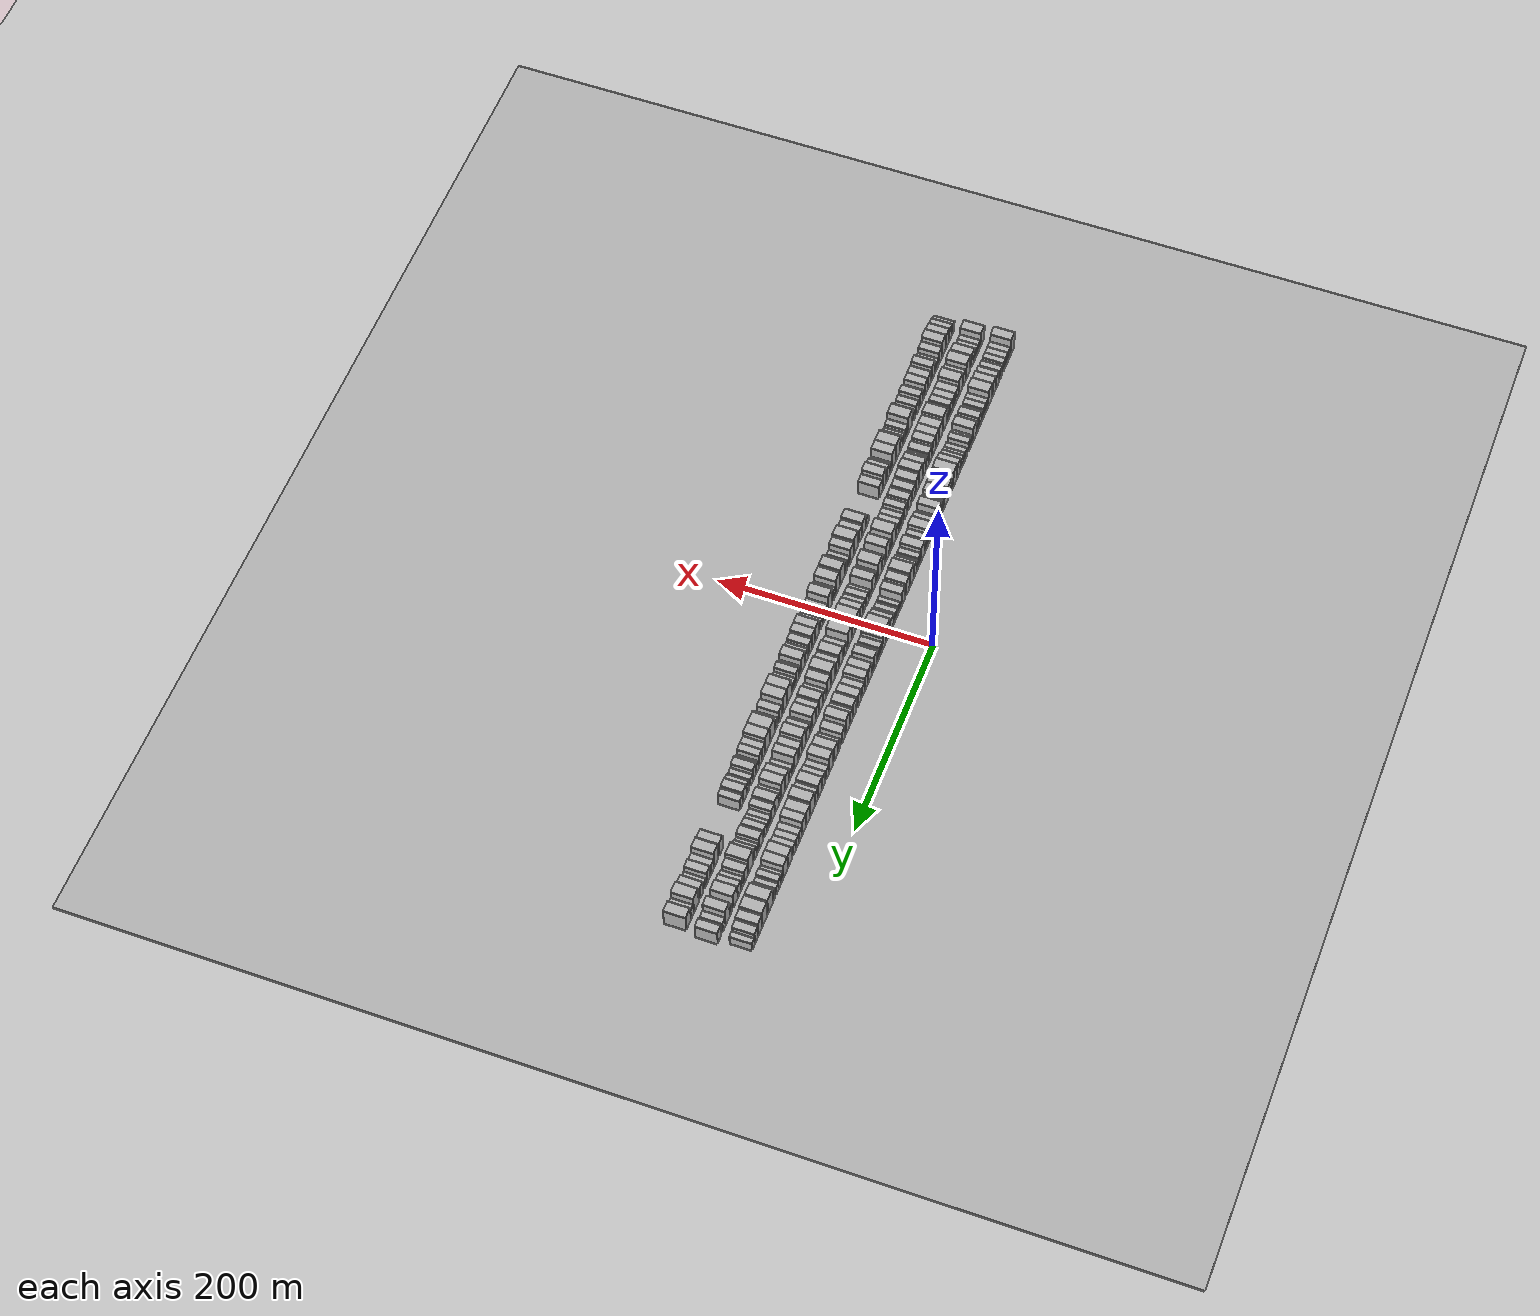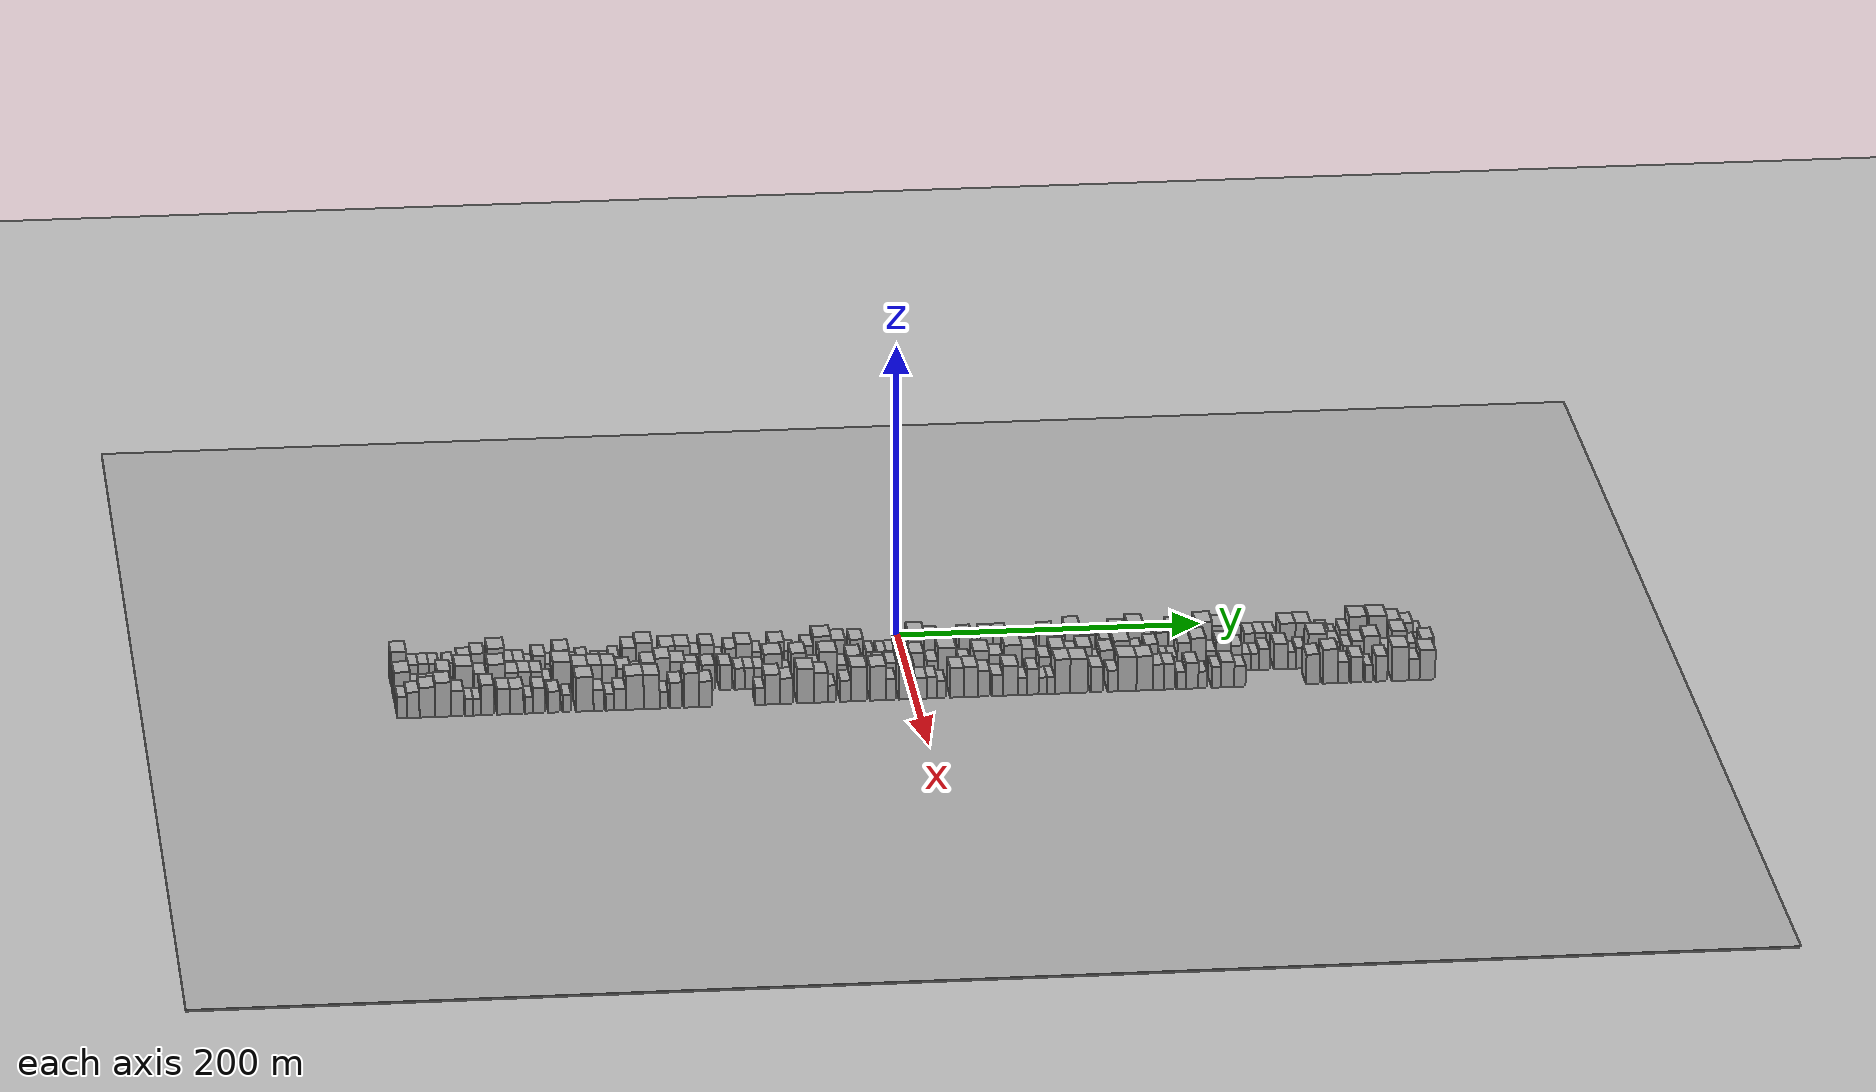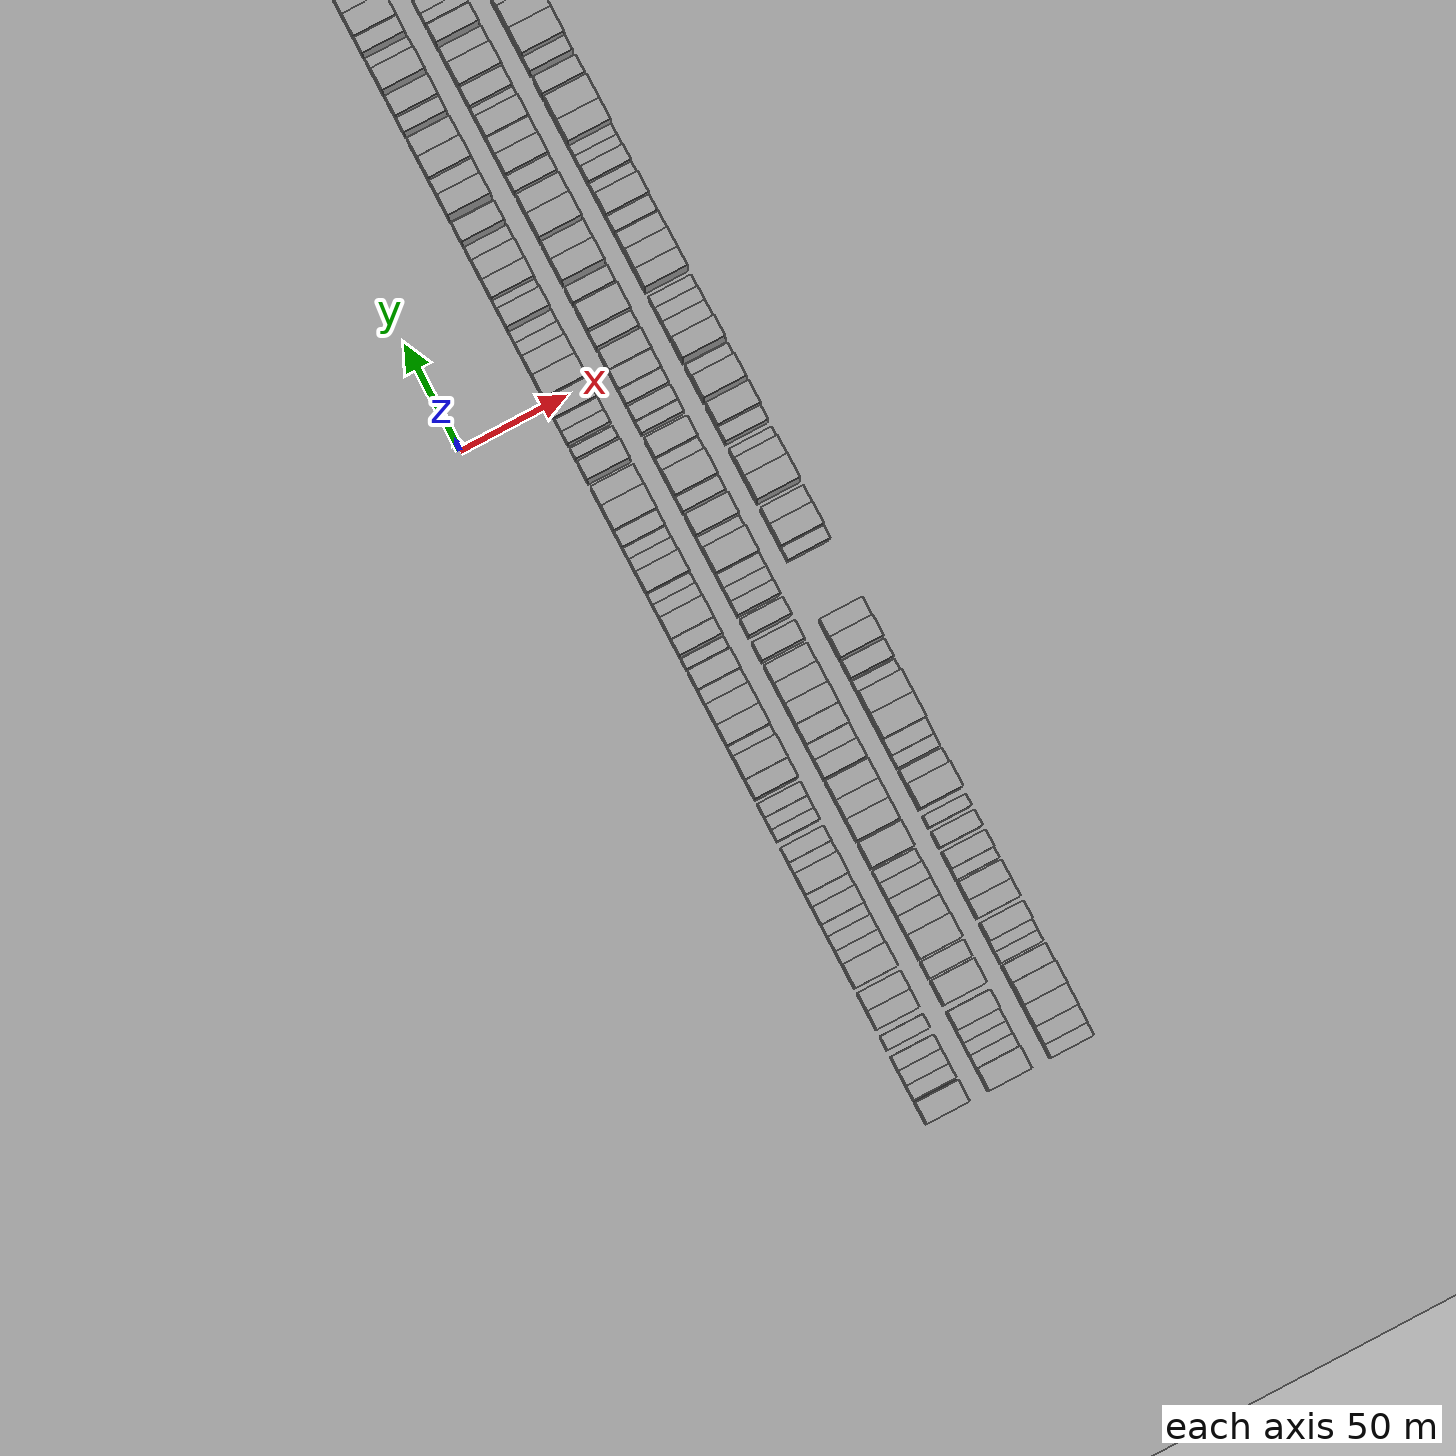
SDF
<?xml version="1.0" encoding="utf-8"?>

<sdf version="1.6">

   <world name="default">

      <gui fullscreen="0">

         <camera name="user_camera">

            <pose>-15 0 4.57585 0 0 0</pose>

            <view_controller>orbit</view_controller>

         </camera>

      </gui>

      <scene>

         <sky>

           <clouds>

             <speed>12</speed>

           </clouds>

         </sky>

         <ambient>0.4 0.4 0.4 1</ambient>

         <background>0.7 0.7 0.7 1</background>

         <shadows>1</shadows>

      </scene>

      <gravity>0 0 -9.8066</gravity>

      <magnetic_field>6e-06 2.3e-05 -4.2e-05</magnetic_field>

      <physics default="0" name="default_physics" type="ode">

         <ode>

            <solver>

               <type>quick</type>

               <iters>10</iters>

               <sor>1.0</sor>

               <use_dynamic_moi_rescaling>0</use_dynamic_moi_rescaling>

            </solver>

            <constraints>

               <cfm>0</cfm>

               <erp>0.2</erp>

               <contact_max_correcting_vel>100</contact_max_correcting_vel>

               <contact_surface_layer>0.001</contact_surface_layer>

            </constraints>

         </ode>

         <max_step_size>0.004</max_step_size>

         <real_time_factor>1</real_time_factor>

         <real_time_update_rate>250</real_time_update_rate>

      </physics>

      <light name="sun" type="directional">

         <cast_shadows>1</cast_shadows>

         <pose>0 0 10 0 0 0</pose>

         <diffuse>0.8 0.8 0.8 1</diffuse>

         <specular>0.2 0.2 0.2 1</specular>

         <attenuation>

            <range>1000</range>

            <constant>0.9</constant>

            <linear>0.01</linear>

            <quadratic>0.001</quadratic>

         </attenuation>

         <direction>-0.5 0.1 -0.9</direction>

      </light>

      <include>

         <name>ground_plane_1</name>

         <uri>model://HANNAS_ground_plane</uri>

         <pose>0 0 0  0 0 0</pose>

      </include>

      <include>

         <name>ground_plane_2</name>

         <uri>model://HANNAS_ground_plane</uri>

         <pose>100 0 0  0 0 0</pose>

      </include>

      <model name="building_1">

         <static>1</static>

         <pose frame="">50.0000 -330.9991 0 0.000000 0.000000 0.000000</pose>

         <link name="link">

            <pose frame="">0 0 12.00 0 0 0</pose>

            <collision name="collision">

               <geometry>

                  <box>

                     <size>20.0000 10.0019 24.0000</size>

                  </box>

               </geometry>

               <max_contacts>10</max_contacts>

               <surface>

                  <contact>

                     <ode/>

                  </contact>

                  <bounce/>

                  <friction>

                     <torsional>

                        <ode/>

                     </torsional>

                     <ode/>

                  </friction>

               </surface>

            </collision>

            <visual name="visual">

               <cast_shadows>0</cast_shadows>

               <geometry>

                  <box>

                     <size>20.0000 10.0019 24.0000</size>

                  </box>

               </geometry>

               <material>

                  <script>

                     <uri>model://HANNAS_wall/materials/scripts</uri>

                     <uri>model://HANNAS_wall/materials/textures</uri>

                     <name>vrc/HANNAS_wall</name>

                  </script>

               </material>

            </visual>

            <self_collide>0</self_collide>

            <enable_wind>0</enable_wind>

            <kinematic>0</kinematic>

         </link>

      </model>

      <model name="building_2">

         <static>1</static>

         <pose frame="">50.0000 -321.7026 0 0.000000 0.000000 0.000000</pose>

         <link name="link">

            <pose frame="">0 0 7.50 0 0 0</pose>

            <collision name="collision">

               <geometry>

                  <box>

                     <size>20.0000 6.5910 15.0000</size>

                  </box>

               </geometry>

               <max_contacts>10</max_contacts>

               <surface>

                  <contact>

                     <ode/>

                  </contact>

                  <bounce/>

                  <friction>

                     <torsional>

                        <ode/>

                     </torsional>

                     <ode/>

                  </friction>

               </surface>

            </collision>

            <visual name="visual">

               <cast_shadows>0</cast_shadows>

               <geometry>

                  <box>

                     <size>20.0000 6.5910 15.0000</size>

                  </box>

               </geometry>

               <material>

                  <script>

                     <uri>model://HANNAS_wall/materials/scripts</uri>

                     <uri>model://HANNAS_wall/materials/textures</uri>

                     <name>vrc/HANNAS_wall</name>

                  </script>

               </material>

            </visual>

            <self_collide>0</self_collide>

            <enable_wind>0</enable_wind>

            <kinematic>0</kinematic>

         </link>

      </model>

      <model name="building_3">

         <static>1</static>

         <pose frame="">50.0000 -314.9518 0 0.000000 0.000000 0.000000</pose>

         <link name="link">

            <pose frame="">0 0 7.50 0 0 0</pose>

            <collision name="collision">

               <geometry>

                  <box>

                     <size>20.0000 6.9107 15.0000</size>

                  </box>

               </geometry>

               <max_contacts>10</max_contacts>

               <surface>

                  <contact>

                     <ode/>

                  </contact>

                  <bounce/>

                  <friction>

                     <torsional>

                        <ode/>

                     </torsional>

                     <ode/>

                  </friction>

               </surface>

            </collision>

            <visual name="visual">

               <cast_shadows>0</cast_shadows>

               <geometry>

                  <box>

                     <size>20.0000 6.9107 15.0000</size>

                  </box>

               </geometry>

               <material>

                  <script>

                     <uri>model://HANNAS_wall/materials/scripts</uri>

                     <uri>model://HANNAS_wall/materials/textures</uri>

                     <name>vrc/HANNAS_wall</name>

                  </script>

               </material>

            </visual>

            <self_collide>0</self_collide>

            <enable_wind>0</enable_wind>

            <kinematic>0</kinematic>

         </link>

      </model>

      <model name="building_4">

         <static>1</static>

         <pose frame="">50.0000 -308.2423 0 0.000000 0.000000 0.000000</pose>

         <link name="link">

            <pose frame="">0 0 7.50 0 0 0</pose>

            <collision name="collision">

               <geometry>

                  <box>

                     <size>20.0000 6.5084 15.0000</size>

                  </box>

               </geometry>

               <max_contacts>10</max_contacts>

               <surface>

                  <contact>

                     <ode/>

                  </contact>

                  <bounce/>

                  <friction>

                     <torsional>

                        <ode/>

                     </torsional>

                     <ode/>

                  </friction>

               </surface>

            </collision>

            <visual name="visual">

               <cast_shadows>0</cast_shadows>

               <geometry>

                  <box>

                     <size>20.0000 6.5084 15.0000</size>

                  </box>

               </geometry>

               <material>

                  <script>

                     <uri>model://HANNAS_wall/materials/scripts</uri>

                     <uri>model://HANNAS_wall/materials/textures</uri>

                     <name>vrc/HANNAS_wall</name>

                  </script>

               </material>

            </visual>

            <self_collide>0</self_collide>

            <enable_wind>0</enable_wind>

            <kinematic>0</kinematic>

         </link>

      </model>

      <model name="building_5">

         <static>1</static>

         <pose frame="">50.0000 -298.7529 0 0.000000 0.000000 0.000000</pose>

         <link name="link">

            <pose frame="">0 0 7.50 0 0 0</pose>

            <collision name="collision">

               <geometry>

                  <box>

                     <size>20.0000 6.4704 15.0000</size>

                  </box>

               </geometry>

               <max_contacts>10</max_contacts>

               <surface>

                  <contact>

                     <ode/>

                  </contact>

                  <bounce/>

                  <friction>

                     <torsional>

                        <ode/>

                     </torsional>

                     <ode/>

                  </friction>

               </surface>

            </collision>

            <visual name="visual">

               <cast_shadows>0</cast_shadows>

               <geometry>

                  <box>

                     <size>20.0000 6.4704 15.0000</size>

                  </box>

               </geometry>

               <material>

                  <script>

                     <uri>model://HANNAS_wall/materials/scripts</uri>

                     <uri>model://HANNAS_wall/materials/textures</uri>

                     <name>vrc/HANNAS_wall</name>

                  </script>

               </material>

            </visual>

            <self_collide>0</self_collide>

            <enable_wind>0</enable_wind>

            <kinematic>0</kinematic>

         </link>

      </model>

      <model name="building_6">

         <static>1</static>

         <pose frame="">50.0000 -288.2201 0 0.000000 0.000000 0.000000</pose>

         <link name="link">

            <pose frame="">0 0 9.00 0 0 0</pose>

            <collision name="collision">

               <geometry>

                  <box>

                     <size>20.0000 8.5954 18.0000</size>

                  </box>

               </geometry>

               <max_contacts>10</max_contacts>

               <surface>

                  <contact>

                     <ode/>

                  </contact>

                  <bounce/>

                  <friction>

                     <torsional>

                        <ode/>

                     </torsional>

                     <ode/>

                  </friction>

               </surface>

            </collision>

            <visual name="visual">

               <cast_shadows>0</cast_shadows>

               <geometry>

                  <box>

                     <size>20.0000 8.5954 18.0000</size>

                  </box>

               </geometry>

               <material>

                  <script>

                     <uri>model://HANNAS_wall/materials/scripts</uri>

                     <uri>model://HANNAS_wall/materials/textures</uri>

                     <name>vrc/HANNAS_wall</name>

                  </script>

               </material>

            </visual>

            <self_collide>0</self_collide>

            <enable_wind>0</enable_wind>

            <kinematic>0</kinematic>

         </link>

      </model>

      <model name="building_7">

         <static>1</static>

         <pose frame="">50.0000 -279.6551 0 0.000000 0.000000 0.000000</pose>

         <link name="link">

            <pose frame="">0 0 10.50 0 0 0</pose>

            <collision name="collision">

               <geometry>

                  <box>

                     <size>20.0000 8.5346 21.0000</size>

                  </box>

               </geometry>

               <max_contacts>10</max_contacts>

               <surface>

                  <contact>

                     <ode/>

                  </contact>

                  <bounce/>

                  <friction>

                     <torsional>

                        <ode/>

                     </torsional>

                     <ode/>

                  </friction>

               </surface>

            </collision>

            <visual name="visual">

               <cast_shadows>0</cast_shadows>

               <geometry>

                  <box>

                     <size>20.0000 8.5346 21.0000</size>

                  </box>

               </geometry>

               <material>

                  <script>

                     <uri>model://HANNAS_wall/materials/scripts</uri>

                     <uri>model://HANNAS_wall/materials/textures</uri>

                     <name>vrc/HANNAS_wall</name>

                  </script>

               </material>

            </visual>

            <self_collide>0</self_collide>

            <enable_wind>0</enable_wind>

            <kinematic>0</kinematic>

         </link>

      </model>

      <model name="building_8">

         <static>1</static>

         <pose frame="">50.0000 -267.8186 0 0.000000 0.000000 0.000000</pose>

         <link name="link">

            <pose frame="">0 0 12.00 0 0 0</pose>

            <collision name="collision">

               <geometry>

                  <box>

                     <size>20.0000 11.1383 24.0000</size>

                  </box>

               </geometry>

               <max_contacts>10</max_contacts>

               <surface>

                  <contact>

                     <ode/>

                  </contact>

                  <bounce/>

                  <friction>

                     <torsional>

                        <ode/>

                     </torsional>

                     <ode/>

                  </friction>

               </surface>

            </collision>

            <visual name="visual">

               <cast_shadows>0</cast_shadows>

               <geometry>

                  <box>

                     <size>20.0000 11.1383 24.0000</size>

                  </box>

               </geometry>

               <material>

                  <script>

                     <uri>model://HANNAS_wall/materials/scripts</uri>

                     <uri>model://HANNAS_wall/materials/textures</uri>

                     <name>vrc/HANNAS_wall</name>

                  </script>

               </material>

            </visual>

            <self_collide>0</self_collide>

            <enable_wind>0</enable_wind>

            <kinematic>0</kinematic>

         </link>

      </model>

      <model name="building_9">

         <static>1</static>

         <pose frame="">50.0000 -259.2012 0 0.000000 0.000000 0.000000</pose>

         <link name="link">

            <pose frame="">0 0 7.50 0 0 0</pose>

            <collision name="collision">

               <geometry>

                  <box>

                     <size>20.0000 6.0966 15.0000</size>

                  </box>

               </geometry>

               <max_contacts>10</max_contacts>

               <surface>

                  <contact>

                     <ode/>

                  </contact>

                  <bounce/>

                  <friction>

                     <torsional>

                        <ode/>

                     </torsional>

                     <ode/>

                  </friction>

               </surface>

            </collision>

            <visual name="visual">

               <cast_shadows>0</cast_shadows>

               <geometry>

                  <box>

                     <size>20.0000 6.0966 15.0000</size>

                  </box>

               </geometry>

               <material>

                  <script>

                     <uri>model://HANNAS_wall/materials/scripts</uri>

                     <uri>model://HANNAS_wall/materials/textures</uri>

                     <name>vrc/HANNAS_wall</name>

                  </script>

               </material>

            </visual>

            <self_collide>0</self_collide>

            <enable_wind>0</enable_wind>

            <kinematic>0</kinematic>

         </link>

      </model>

      <model name="building_10">

         <static>1</static>

         <pose frame="">50.0000 -252.7200 0 0.000000 0.000000 0.000000</pose>

         <link name="link">

            <pose frame="">0 0 7.50 0 0 0</pose>

            <collision name="collision">

               <geometry>

                  <box>

                     <size>20.0000 6.8658 15.0000</size>

                  </box>

               </geometry>

               <max_contacts>10</max_contacts>

               <surface>

                  <contact>

                     <ode/>

                  </contact>

                  <bounce/>

                  <friction>

                     <torsional>

                        <ode/>

                     </torsional>

                     <ode/>

                  </friction>

               </surface>

            </collision>

            <visual name="visual">

               <cast_shadows>0</cast_shadows>

               <geometry>

                  <box>

                     <size>20.0000 6.8658 15.0000</size>

                  </box>

               </geometry>

               <material>

                  <script>

                     <uri>model://HANNAS_wall/materials/scripts</uri>

                     <uri>model://HANNAS_wall/materials/textures</uri>

                     <name>vrc/HANNAS_wall</name>

                  </script>

               </material>

            </visual>

            <self_collide>0</self_collide>

            <enable_wind>0</enable_wind>

            <kinematic>0</kinematic>

         </link>

      </model>

      <model name="building_11">

         <static>1</static>

         <pose frame="">50.0000 -246.5598 0 0.000000 0.000000 0.000000</pose>

         <link name="link">

            <pose frame="">0 0 6.00 0 0 0</pose>

            <collision name="collision">

               <geometry>

                  <box>

                     <size>20.0000 5.4546 12.0000</size>

                  </box>

               </geometry>

               <max_contacts>10</max_contacts>

               <surface>

                  <contact>

                     <ode/>

                  </contact>

                  <bounce/>

                  <friction>

                     <torsional>

                        <ode/>

                     </torsional>

                     <ode/>

                  </friction>

               </surface>

            </collision>

            <visual name="visual">

               <cast_shadows>0</cast_shadows>

               <geometry>

                  <box>

                     <size>20.0000 5.4546 12.0000</size>

                  </box>

               </geometry>

               <material>

                  <script>

                     <uri>model://HANNAS_wall/materials/scripts</uri>

                     <uri>model://HANNAS_wall/materials/textures</uri>

                     <name>vrc/HANNAS_wall</name>

                  </script>

               </material>

            </visual>

            <self_collide>0</self_collide>

            <enable_wind>0</enable_wind>

            <kinematic>0</kinematic>

         </link>

      </model>

      <model name="building_12">

         <static>1</static>

         <pose frame="">50.0000 -239.7574 0 0.000000 0.000000 0.000000</pose>

         <link name="link">

            <pose frame="">0 0 9.00 0 0 0</pose>

            <collision name="collision">

               <geometry>

                  <box>

                     <size>20.0000 8.1502 18.0000</size>

                  </box>

               </geometry>

               <max_contacts>10</max_contacts>

               <surface>

                  <contact>

                     <ode/>

                  </contact>

                  <bounce/>

                  <friction>

                     <torsional>

                        <ode/>

                     </torsional>

                     <ode/>

                  </friction>

               </surface>

            </collision>

            <visual name="visual">

               <cast_shadows>0</cast_shadows>

               <geometry>

                  <box>

                     <size>20.0000 8.1502 18.0000</size>

                  </box>

               </geometry>

               <material>

                  <script>

                     <uri>model://HANNAS_wall/materials/scripts</uri>

                     <uri>model://HANNAS_wall/materials/textures</uri>

                     <name>vrc/HANNAS_wall</name>

                  </script>

               </material>

            </visual>

            <self_collide>0</self_collide>

            <enable_wind>0</enable_wind>

            <kinematic>0</kinematic>

         </link>

      </model>

      <model name="building_13">

         <static>1</static>

         <pose frame="">50.0000 -232.8843 0 0.000000 0.000000 0.000000</pose>

         <link name="link">

            <pose frame="">0 0 6.00 0 0 0</pose>

            <collision name="collision">

               <geometry>

                  <box>

                     <size>20.0000 5.5961 12.0000</size>

                  </box>

               </geometry>

               <max_contacts>10</max_contacts>

               <surface>

                  <contact>

                     <ode/>

                  </contact>

                  <bounce/>

                  <friction>

                     <torsional>

                        <ode/>

                     </torsional>

                     <ode/>

                  </friction>

               </surface>

            </collision>

            <visual name="visual">

               <cast_shadows>0</cast_shadows>

               <geometry>

                  <box>

                     <size>20.0000 5.5961 12.0000</size>

                  </box>

               </geometry>

               <material>

                  <script>

                     <uri>model://HANNAS_wall/materials/scripts</uri>

                     <uri>model://HANNAS_wall/materials/textures</uri>

                     <name>vrc/HANNAS_wall</name>

                  </script>

               </material>

            </visual>

            <self_collide>0</self_collide>

            <enable_wind>0</enable_wind>

            <kinematic>0</kinematic>

         </link>

      </model>

      <model name="building_14">

         <static>1</static>

         <pose frame="">50.0000 -225.1341 0 0.000000 0.000000 0.000000</pose>

         <link name="link">

            <pose frame="">0 0 10.50 0 0 0</pose>

            <collision name="collision">

               <geometry>

                  <box>

                     <size>20.0000 9.9042 21.0000</size>

                  </box>

               </geometry>

               <max_contacts>10</max_contacts>

               <surface>

                  <contact>

                     <ode/>

                  </contact>

                  <bounce/>

                  <friction>

                     <torsional>

                        <ode/>

                     </torsional>

                     <ode/>

                  </friction>

               </surface>

            </collision>

            <visual name="visual">

               <cast_shadows>0</cast_shadows>

               <geometry>

                  <box>

                     <size>20.0000 9.9042 21.0000</size>

                  </box>

               </geometry>

               <material>

                  <script>

                     <uri>model://HANNAS_wall/materials/scripts</uri>

                     <uri>model://HANNAS_wall/materials/textures</uri>

                     <name>vrc/HANNAS_wall</name>

                  </script>

               </material>

            </visual>

            <self_collide>0</self_collide>

            <enable_wind>0</enable_wind>

            <kinematic>0</kinematic>

         </link>

      </model>

      <model name="building_15">

         <static>1</static>

         <pose frame="">50.0000 -217.6259 0 0.000000 0.000000 0.000000</pose>

         <link name="link">

            <pose frame="">0 0 6.00 0 0 0</pose>

            <collision name="collision">

               <geometry>

                  <box>

                     <size>20.0000 5.1122 12.0000</size>

                  </box>

               </geometry>

               <max_contacts>10</max_contacts>

               <surface>

                  <contact>

                     <ode/>

                  </contact>

                  <bounce/>

                  <friction>

                     <torsional>

                        <ode/>

                     </torsional>

                     <ode/>

                  </friction>

               </surface>

            </collision>

            <visual name="visual">

               <cast_shadows>0</cast_shadows>

               <geometry>

                  <box>

                     <size>20.0000 5.1122 12.0000</size>

                  </box>

               </geometry>

               <material>

                  <script>

                     <uri>model://HANNAS_wall/materials/scripts</uri>

                     <uri>model://HANNAS_wall/materials/textures</uri>

                     <name>vrc/HANNAS_wall</name>

                  </script>

               </material>

            </visual>

            <self_collide>0</self_collide>

            <enable_wind>0</enable_wind>

            <kinematic>0</kinematic>

         </link>

      </model>

      <model name="building_16">

         <static>1</static>

         <pose frame="">50.0000 -211.5449 0 0.000000 0.000000 0.000000</pose>

         <link name="link">

            <pose frame="">0 0 7.50 0 0 0</pose>

            <collision name="collision">

               <geometry>

                  <box>

                     <size>20.0000 7.0499 15.0000</size>

                  </box>

               </geometry>

               <max_contacts>10</max_contacts>

               <surface>

                  <contact>

                     <ode/>

                  </contact>

                  <bounce/>

                  <friction>

                     <torsional>

                        <ode/>

                     </torsional>

                     <ode/>

                  </friction>

               </surface>

            </collision>

            <visual name="visual">

               <cast_shadows>0</cast_shadows>

               <geometry>

                  <box>

                     <size>20.0000 7.0499 15.0000</size>

                  </box>

               </geometry>

               <material>

                  <script>

                     <uri>model://HANNAS_wall/materials/scripts</uri>

                     <uri>model://HANNAS_wall/materials/textures</uri>

                     <name>vrc/HANNAS_wall</name>

                  </script>

               </material>

            </visual>

            <self_collide>0</self_collide>

            <enable_wind>0</enable_wind>

            <kinematic>0</kinematic>

         </link>

      </model>

      <model name="building_17">

         <static>1</static>

         <pose frame="">50.0000 -202.3055 0 0.000000 0.000000 0.000000</pose>

         <link name="link">

            <pose frame="">0 0 6.00 0 0 0</pose>

            <collision name="collision">

               <geometry>

                  <box>

                     <size>20.0000 5.4289 12.0000</size>

                  </box>

               </geometry>

               <max_contacts>10</max_contacts>

               <surface>

                  <contact>

                     <ode/>

                  </contact>

                  <bounce/>

                  <friction>

                     <torsional>

                        <ode/>

                     </torsional>

                     <ode/>

                  </friction>

               </surface>

            </collision>

            <visual name="visual">

               <cast_shadows>0</cast_shadows>

               <geometry>

                  <box>

                     <size>20.0000 5.4289 12.0000</size>

                  </box>

               </geometry>

               <material>

                  <script>

                     <uri>model://HANNAS_wall/materials/scripts</uri>

                     <uri>model://HANNAS_wall/materials/textures</uri>

                     <name>vrc/HANNAS_wall</name>

                  </script>

               </material>

            </visual>

            <self_collide>0</self_collide>

            <enable_wind>0</enable_wind>

            <kinematic>0</kinematic>

         </link>

      </model>

      <model name="building_18">

         <static>1</static>

         <pose frame="">50.0000 -196.8165 0 0.000000 0.000000 0.000000</pose>

         <link name="link">

            <pose frame="">0 0 6.00 0 0 0</pose>

            <collision name="collision">

               <geometry>

                  <box>

                     <size>20.0000 5.5491 12.0000</size>

                  </box>

               </geometry>

               <max_contacts>10</max_contacts>

               <surface>

                  <contact>

                     <ode/>

                  </contact>

                  <bounce/>

                  <friction>

                     <torsional>

                        <ode/>

                     </torsional>

                     <ode/>

                  </friction>

               </surface>

            </collision>

            <visual name="visual">

               <cast_shadows>0</cast_shadows>

               <geometry>

                  <box>

                     <size>20.0000 5.5491 12.0000</size>

                  </box>

               </geometry>

               <material>

                  <script>

                     <uri>model://HANNAS_wall/materials/scripts</uri>

                     <uri>model://HANNAS_wall/materials/textures</uri>

                     <name>vrc/HANNAS_wall</name>

                  </script>

               </material>

            </visual>

            <self_collide>0</self_collide>

            <enable_wind>0</enable_wind>

            <kinematic>0</kinematic>

         </link>

      </model>

      <model name="building_19">

         <static>1</static>

         <pose frame="">50.0000 -190.8053 0 0.000000 0.000000 0.000000</pose>

         <link name="link">

            <pose frame="">0 0 7.50 0 0 0</pose>

            <collision name="collision">

               <geometry>

                  <box>

                     <size>20.0000 6.4733 15.0000</size>

                  </box>

               </geometry>

               <max_contacts>10</max_contacts>

               <surface>

                  <contact>

                     <ode/>

                  </contact>

                  <bounce/>

                  <friction>

                     <torsional>

                        <ode/>

                     </torsional>

                     <ode/>

                  </friction>

               </surface>

            </collision>

            <visual name="visual">

               <cast_shadows>0</cast_shadows>

               <geometry>

                  <box>

                     <size>20.0000 6.4733 15.0000</size>

                  </box>

               </geometry>

               <material>

                  <script>

                     <uri>model://HANNAS_wall/materials/scripts</uri>

                     <uri>model://HANNAS_wall/materials/textures</uri>

                     <name>vrc/HANNAS_wall</name>

                  </script>

               </material>

            </visual>

            <self_collide>0</self_collide>

            <enable_wind>0</enable_wind>

            <kinematic>0</kinematic>

         </link>

      </model>

      <model name="building_20">

         <static>1</static>

         <pose frame="">50.0000 -181.1631 0 0.000000 0.000000 0.000000</pose>

         <link name="link">

            <pose frame="">0 0 10.50 0 0 0</pose>

            <collision name="collision">

               <geometry>

                  <box>

                     <size>20.0000 8.8112 21.0000</size>

                  </box>

               </geometry>

               <max_contacts>10</max_contacts>

               <surface>

                  <contact>

                     <ode/>

                  </contact>

                  <bounce/>

                  <friction>

                     <torsional>

                        <ode/>

                     </torsional>

                     <ode/>

                  </friction>

               </surface>

            </collision>

            <visual name="visual">

               <cast_shadows>0</cast_shadows>

               <geometry>

                  <box>

                     <size>20.0000 8.8112 21.0000</size>

                  </box>

               </geometry>

               <material>

                  <script>

                     <uri>model://HANNAS_wall/materials/scripts</uri>

                     <uri>model://HANNAS_wall/materials/textures</uri>

                     <name>vrc/HANNAS_wall</name>

                  </script>

               </material>

            </visual>

            <self_collide>0</self_collide>

            <enable_wind>0</enable_wind>

            <kinematic>0</kinematic>

         </link>

      </model>

      <model name="building_21">

         <static>1</static>

         <pose frame="">50.0000 -171.3831 0 0.000000 0.000000 0.000000</pose>

         <link name="link">

            <pose frame="">0 0 12.00 0 0 0</pose>

            <collision name="collision">

               <geometry>

                  <box>

                     <size>20.0000 10.7487 24.0000</size>

                  </box>

               </geometry>

               <max_contacts>10</max_contacts>

               <surface>

                  <contact>

                     <ode/>

                  </contact>

                  <bounce/>

                  <friction>

                     <torsional>

                        <ode/>

                     </torsional>

                     <ode/>

                  </friction>

               </surface>

            </collision>

            <visual name="visual">

               <cast_shadows>0</cast_shadows>

               <geometry>

                  <box>

                     <size>20.0000 10.7487 24.0000</size>

                  </box>

               </geometry>

               <material>

                  <script>

                     <uri>model://HANNAS_wall/materials/scripts</uri>

                     <uri>model://HANNAS_wall/materials/textures</uri>

                     <name>vrc/HANNAS_wall</name>

                  </script>

               </material>

            </visual>

            <self_collide>0</self_collide>

            <enable_wind>0</enable_wind>

            <kinematic>0</kinematic>

         </link>

      </model>

      <model name="building_22">

         <static>1</static>

         <pose frame="">50.0000 -163.4600 0 0.000000 0.000000 0.000000</pose>

         <link name="link">

            <pose frame="">0 0 6.00 0 0 0</pose>

            <collision name="collision">

               <geometry>

                  <box>

                     <size>20.0000 5.0975 12.0000</size>

                  </box>

               </geometry>

               <max_contacts>10</max_contacts>

               <surface>

                  <contact>

                     <ode/>

                  </contact>

                  <bounce/>

                  <friction>

                     <torsional>

                        <ode/>

                     </torsional>

                     <ode/>

                  </friction>

               </surface>

            </collision>

            <visual name="visual">

               <cast_shadows>0</cast_shadows>

               <geometry>

                  <box>

                     <size>20.0000 5.0975 12.0000</size>

                  </box>

               </geometry>

               <material>

                  <script>

                     <uri>model://HANNAS_wall/materials/scripts</uri>

                     <uri>model://HANNAS_wall/materials/textures</uri>

                     <name>vrc/HANNAS_wall</name>

                  </script>

               </material>

            </visual>

            <self_collide>0</self_collide>

            <enable_wind>0</enable_wind>

            <kinematic>0</kinematic>

         </link>

      </model>

      <model name="building_23">

         <static>1</static>

         <pose frame="">50.0000 -156.1194 0 0.000000 0.000000 0.000000</pose>

         <link name="link">

            <pose frame="">0 0 10.50 0 0 0</pose>

            <collision name="collision">

               <geometry>

                  <box>

                     <size>20.0000 9.5837 21.0000</size>

                  </box>

               </geometry>

               <max_contacts>10</max_contacts>

               <surface>

                  <contact>

                     <ode/>

                  </contact>

                  <bounce/>

                  <friction>

                     <torsional>

                        <ode/>

                     </torsional>

                     <ode/>

                  </friction>

               </surface>

            </collision>

            <visual name="visual">

               <cast_shadows>0</cast_shadows>

               <geometry>

                  <box>

                     <size>20.0000 9.5837 21.0000</size>

                  </box>

               </geometry>

               <material>

                  <script>

                     <uri>model://HANNAS_wall/materials/scripts</uri>

                     <uri>model://HANNAS_wall/materials/textures</uri>

                     <name>vrc/HANNAS_wall</name>

                  </script>

               </material>

            </visual>

            <self_collide>0</self_collide>

            <enable_wind>0</enable_wind>

            <kinematic>0</kinematic>

         </link>

      </model>

      <model name="building_24">

         <static>1</static>

         <pose frame="">50.0000 -146.5039 0 0.000000 0.000000 0.000000</pose>

         <link name="link">

            <pose frame="">0 0 10.50 0 0 0</pose>

            <collision name="collision">

               <geometry>

                  <box>

                     <size>20.0000 9.6473 21.0000</size>

                  </box>

               </geometry>

               <max_contacts>10</max_contacts>

               <surface>

                  <contact>

                     <ode/>

                  </contact>

                  <bounce/>

                  <friction>

                     <torsional>

                        <ode/>

                     </torsional>

                     <ode/>

                  </friction>

               </surface>

            </collision>

            <visual name="visual">

               <cast_shadows>0</cast_shadows>

               <geometry>

                  <box>

                     <size>20.0000 9.6473 21.0000</size>

                  </box>

               </geometry>

               <material>

                  <script>

                     <uri>model://HANNAS_wall/materials/scripts</uri>

                     <uri>model://HANNAS_wall/materials/textures</uri>

                     <name>vrc/HANNAS_wall</name>

                  </script>

               </material>

            </visual>

            <self_collide>0</self_collide>

            <enable_wind>0</enable_wind>

            <kinematic>0</kinematic>

         </link>

      </model>

      <model name="building_25">

         <static>1</static>

         <pose frame="">50.0000 -138.2730 0 0.000000 0.000000 0.000000</pose>

         <link name="link">

            <pose frame="">0 0 7.50 0 0 0</pose>

            <collision name="collision">

               <geometry>

                  <box>

                     <size>20.0000 6.8145 15.0000</size>

                  </box>

               </geometry>

               <max_contacts>10</max_contacts>

               <surface>

                  <contact>

                     <ode/>

                  </contact>

                  <bounce/>

                  <friction>

                     <torsional>

                        <ode/>

                     </torsional>

                     <ode/>

                  </friction>

               </surface>

            </collision>

            <visual name="visual">

               <cast_shadows>0</cast_shadows>

               <geometry>

                  <box>

                     <size>20.0000 6.8145 15.0000</size>

                  </box>

               </geometry>

               <material>

                  <script>

                     <uri>model://HANNAS_wall/materials/scripts</uri>

                     <uri>model://HANNAS_wall/materials/textures</uri>

                     <name>vrc/HANNAS_wall</name>

                  </script>

               </material>

            </visual>

            <self_collide>0</self_collide>

            <enable_wind>0</enable_wind>

            <kinematic>0</kinematic>

         </link>

      </model>

      <model name="building_26">

         <static>1</static>

         <pose frame="">50.0000 -130.3590 0 0.000000 0.000000 0.000000</pose>

         <link name="link">

            <pose frame="">0 0 10.50 0 0 0</pose>

            <collision name="collision">

               <geometry>

                  <box>

                     <size>20.0000 9.0134 21.0000</size>

                  </box>

               </geometry>

               <max_contacts>10</max_contacts>

               <surface>

                  <contact>

                     <ode/>

                  </contact>

                  <bounce/>

                  <friction>

                     <torsional>

                        <ode/>

                     </torsional>

                     <ode/>

                  </friction>

               </surface>

            </collision>

            <visual name="visual">

               <cast_shadows>0</cast_shadows>

               <geometry>

                  <box>

                     <size>20.0000 9.0134 21.0000</size>

                  </box>

               </geometry>

               <material>

                  <script>

                     <uri>model://HANNAS_wall/materials/scripts</uri>

                     <uri>model://HANNAS_wall/materials/textures</uri>

                     <name>vrc/HANNAS_wall</name>

                  </script>

               </material>

            </visual>

            <self_collide>0</self_collide>

            <enable_wind>0</enable_wind>

            <kinematic>0</kinematic>

         </link>

      </model>

      <model name="building_27">

         <static>1</static>

         <pose frame="">50.0000 -122.3094 0 0.000000 0.000000 0.000000</pose>

         <link name="link">

            <pose frame="">0 0 6.00 0 0 0</pose>

            <collision name="collision">

               <geometry>

                  <box>

                     <size>20.0000 5.0859 12.0000</size>

                  </box>

               </geometry>

               <max_contacts>10</max_contacts>

               <surface>

                  <contact>

                     <ode/>

                  </contact>

                  <bounce/>

                  <friction>

                     <torsional>

                        <ode/>

                     </torsional>

                     <ode/>

                  </friction>

               </surface>

            </collision>

            <visual name="visual">

               <cast_shadows>0</cast_shadows>

               <geometry>

                  <box>

                     <size>20.0000 5.0859 12.0000</size>

                  </box>

               </geometry>

               <material>

                  <script>

                     <uri>model://HANNAS_wall/materials/scripts</uri>

                     <uri>model://HANNAS_wall/materials/textures</uri>

                     <name>vrc/HANNAS_wall</name>

                  </script>

               </material>

            </visual>

            <self_collide>0</self_collide>

            <enable_wind>0</enable_wind>

            <kinematic>0</kinematic>

         </link>

      </model>

      <model name="building_28">

         <static>1</static>

         <pose frame="">50.0000 -115.0501 0 0.000000 0.000000 0.000000</pose>

         <link name="link">

            <pose frame="">0 0 9.00 0 0 0</pose>

            <collision name="collision">

               <geometry>

                  <box>

                     <size>20.0000 7.4328 18.0000</size>

                  </box>

               </geometry>

               <max_contacts>10</max_contacts>

               <surface>

                  <contact>

                     <ode/>

                  </contact>

                  <bounce/>

                  <friction>

                     <torsional>

                        <ode/>

                     </torsional>

                     <ode/>

                  </friction>

               </surface>

            </collision>

            <visual name="visual">

               <cast_shadows>0</cast_shadows>

               <geometry>

                  <box>

                     <size>20.0000 7.4328 18.0000</size>

                  </box>

               </geometry>

               <material>

                  <script>

                     <uri>model://HANNAS_wall/materials/scripts</uri>

                     <uri>model://HANNAS_wall/materials/textures</uri>

                     <name>vrc/HANNAS_wall</name>

                  </script>

               </material>

            </visual>

            <self_collide>0</self_collide>

            <enable_wind>0</enable_wind>

            <kinematic>0</kinematic>

         </link>

      </model>

      <model name="building_29">

         <static>1</static>

         <pose frame="">50.0000 -106.2806 0 0.000000 0.000000 0.000000</pose>

         <link name="link">

            <pose frame="">0 0 10.50 0 0 0</pose>

            <collision name="collision">

               <geometry>

                  <box>

                     <size>20.0000 10.1062 21.0000</size>

                  </box>

               </geometry>

               <max_contacts>10</max_contacts>

               <surface>

                  <contact>

                     <ode/>

                  </contact>

                  <bounce/>

                  <friction>

                     <torsional>

                        <ode/>

                     </torsional>

                     <ode/>

                  </friction>

               </surface>

            </collision>

            <visual name="visual">

               <cast_shadows>0</cast_shadows>

               <geometry>

                  <box>

                     <size>20.0000 10.1062 21.0000</size>

                  </box>

               </geometry>

               <material>

                  <script>

                     <uri>model://HANNAS_wall/materials/scripts</uri>

                     <uri>model://HANNAS_wall/materials/textures</uri>

                     <name>vrc/HANNAS_wall</name>

                  </script>

               </material>

            </visual>

            <self_collide>0</self_collide>

            <enable_wind>0</enable_wind>

            <kinematic>0</kinematic>

         </link>

      </model>

      <model name="building_30">

         <static>1</static>

         <pose frame="">50.0000 -98.0717 0 0.000000 0.000000 0.000000</pose>

         <link name="link">

            <pose frame="">0 0 7.50 0 0 0</pose>

            <collision name="collision">

               <geometry>

                  <box>

                     <size>20.0000 6.3116 15.0000</size>

                  </box>

               </geometry>

               <max_contacts>10</max_contacts>

               <surface>

                  <contact>

                     <ode/>

                  </contact>

                  <bounce/>

                  <friction>

                     <torsional>

                        <ode/>

                     </torsional>

                     <ode/>

                  </friction>

               </surface>

            </collision>

            <visual name="visual">

               <cast_shadows>0</cast_shadows>

               <geometry>

                  <box>

                     <size>20.0000 6.3116 15.0000</size>

                  </box>

               </geometry>

               <material>

                  <script>

                     <uri>model://HANNAS_wall/materials/scripts</uri>

                     <uri>model://HANNAS_wall/materials/textures</uri>

                     <name>vrc/HANNAS_wall</name>

                  </script>

               </material>

            </visual>

            <self_collide>0</self_collide>

            <enable_wind>0</enable_wind>

            <kinematic>0</kinematic>

         </link>

      </model>

      <model name="building_31">

         <static>1</static>

         <pose frame="">50.0000 -92.3373 0 0.000000 0.000000 0.000000</pose>

         <link name="link">

            <pose frame="">0 0 6.00 0 0 0</pose>

            <collision name="collision">

               <geometry>

                  <box>

                     <size>20.0000 5.1571 12.0000</size>

                  </box>

               </geometry>

               <max_contacts>10</max_contacts>

               <surface>

                  <contact>

                     <ode/>

                  </contact>

                  <bounce/>

                  <friction>

                     <torsional>

                        <ode/>

                     </torsional>

                     <ode/>

                  </friction>

               </surface>

            </collision>

            <visual name="visual">

               <cast_shadows>0</cast_shadows>

               <geometry>

                  <box>

                     <size>20.0000 5.1571 12.0000</size>

                  </box>

               </geometry>

               <material>

                  <script>

                     <uri>model://HANNAS_wall/materials/scripts</uri>

                     <uri>model://HANNAS_wall/materials/textures</uri>

                     <name>vrc/HANNAS_wall</name>

                  </script>

               </material>

            </visual>

            <self_collide>0</self_collide>

            <enable_wind>0</enable_wind>

            <kinematic>0</kinematic>

         </link>

      </model>

      <model name="building_32">

         <static>1</static>

         <pose frame="">50.0000 -84.8233 0 0.000000 0.000000 0.000000</pose>

         <link name="link">

            <pose frame="">0 0 10.50 0 0 0</pose>

            <collision name="collision">

               <geometry>

                  <box>

                     <size>20.0000 9.8708 21.0000</size>

                  </box>

               </geometry>

               <max_contacts>10</max_contacts>

               <surface>

                  <contact>

                     <ode/>

                  </contact>

                  <bounce/>

                  <friction>

                     <torsional>

                        <ode/>

                     </torsional>

                     <ode/>

                  </friction>

               </surface>

            </collision>

            <visual name="visual">

               <cast_shadows>0</cast_shadows>

               <geometry>

                  <box>

                     <size>20.0000 9.8708 21.0000</size>

                  </box>

               </geometry>

               <material>

                  <script>

                     <uri>model://HANNAS_wall/materials/scripts</uri>

                     <uri>model://HANNAS_wall/materials/textures</uri>

                     <name>vrc/HANNAS_wall</name>

                  </script>

               </material>

            </visual>

            <self_collide>0</self_collide>

            <enable_wind>0</enable_wind>

            <kinematic>0</kinematic>

         </link>

      </model>

      <model name="building_33">

         <static>1</static>

         <pose frame="">50.0000 -76.7291 0 0.000000 0.000000 0.000000</pose>

         <link name="link">

            <pose frame="">0 0 7.50 0 0 0</pose>

            <collision name="collision">

               <geometry>

                  <box>

                     <size>20.0000 6.3176 15.0000</size>

                  </box>

               </geometry>

               <max_contacts>10</max_contacts>

               <surface>

                  <contact>

                     <ode/>

                  </contact>

                  <bounce/>

                  <friction>

                     <torsional>

                        <ode/>

                     </torsional>

                     <ode/>

                  </friction>

               </surface>

            </collision>

            <visual name="visual">

               <cast_shadows>0</cast_shadows>

               <geometry>

                  <box>

                     <size>20.0000 6.3176 15.0000</size>

                  </box>

               </geometry>

               <material>

                  <script>

                     <uri>model://HANNAS_wall/materials/scripts</uri>

                     <uri>model://HANNAS_wall/materials/textures</uri>

                     <name>vrc/HANNAS_wall</name>

                  </script>

               </material>

            </visual>

            <self_collide>0</self_collide>

            <enable_wind>0</enable_wind>

            <kinematic>0</kinematic>

         </link>

      </model>

      <model name="building_34">

         <static>1</static>

         <pose frame="">50.0000 -70.8833 0 0.000000 0.000000 0.000000</pose>

         <link name="link">

            <pose frame="">0 0 6.00 0 0 0</pose>

            <collision name="collision">

               <geometry>

                  <box>

                     <size>20.0000 5.3740 12.0000</size>

                  </box>

               </geometry>

               <max_contacts>10</max_contacts>

               <surface>

                  <contact>

                     <ode/>

                  </contact>

                  <bounce/>

                  <friction>

                     <torsional>

                        <ode/>

                     </torsional>

                     <ode/>

                  </friction>

               </surface>

            </collision>

            <visual name="visual">

               <cast_shadows>0</cast_shadows>

               <geometry>

                  <box>

                     <size>20.0000 5.3740 12.0000</size>

                  </box>

               </geometry>

               <material>

                  <script>

                     <uri>model://HANNAS_wall/materials/scripts</uri>

                     <uri>model://HANNAS_wall/materials/textures</uri>

                     <name>vrc/HANNAS_wall</name>

                  </script>

               </material>

            </visual>

            <self_collide>0</self_collide>

            <enable_wind>0</enable_wind>

            <kinematic>0</kinematic>

         </link>

      </model>

      <model name="building_35">

         <static>1</static>

         <pose frame="">50.0000 -64.5480 0 0.000000 0.000000 0.000000</pose>

         <link name="link">

            <pose frame="">0 0 9.00 0 0 0</pose>

            <collision name="collision">

               <geometry>

                  <box>

                     <size>20.0000 7.2966 18.0000</size>

                  </box>

               </geometry>

               <max_contacts>10</max_contacts>

               <surface>

                  <contact>

                     <ode/>

                  </contact>

                  <bounce/>

                  <friction>

                     <torsional>

                        <ode/>

                     </torsional>

                     <ode/>

                  </friction>

               </surface>

            </collision>

            <visual name="visual">

               <cast_shadows>0</cast_shadows>

               <geometry>

                  <box>

                     <size>20.0000 7.2966 18.0000</size>

                  </box>

               </geometry>

               <material>

                  <script>

                     <uri>model://HANNAS_wall/materials/scripts</uri>

                     <uri>model://HANNAS_wall/materials/textures</uri>

                     <name>vrc/HANNAS_wall</name>

                  </script>

               </material>

            </visual>

            <self_collide>0</self_collide>

            <enable_wind>0</enable_wind>

            <kinematic>0</kinematic>

         </link>

      </model>

      <model name="building_36">

         <static>1</static>

         <pose frame="">50.0000 -55.1775 0 0.000000 0.000000 0.000000</pose>

         <link name="link">

            <pose frame="">0 0 12.00 0 0 0</pose>

            <collision name="collision">

               <geometry>

                  <box>

                     <size>20.0000 11.4444 24.0000</size>

                  </box>

               </geometry>

               <max_contacts>10</max_contacts>

               <surface>

                  <contact>

                     <ode/>

                  </contact>

                  <bounce/>

                  <friction>

                     <torsional>

                        <ode/>

                     </torsional>

                     <ode/>

                  </friction>

               </surface>

            </collision>

            <visual name="visual">

               <cast_shadows>0</cast_shadows>

               <geometry>

                  <box>

                     <size>20.0000 11.4444 24.0000</size>

                  </box>

               </geometry>

               <material>

                  <script>

                     <uri>model://HANNAS_wall/materials/scripts</uri>

                     <uri>model://HANNAS_wall/materials/textures</uri>

                     <name>vrc/HANNAS_wall</name>

                  </script>

               </material>

            </visual>

            <self_collide>0</self_collide>

            <enable_wind>0</enable_wind>

            <kinematic>0</kinematic>

         </link>

      </model>

      <model name="building_37">

         <static>1</static>

         <pose frame="">50.0000 -44.7978 0 0.000000 0.000000 0.000000</pose>

         <link name="link">

            <pose frame="">0 0 10.50 0 0 0</pose>

            <collision name="collision">

               <geometry>

                  <box>

                     <size>20.0000 9.3149 21.0000</size>

                  </box>

               </geometry>

               <max_contacts>10</max_contacts>

               <surface>

                  <contact>

                     <ode/>

                  </contact>

                  <bounce/>

                  <friction>

                     <torsional>

                        <ode/>

                     </torsional>

                     <ode/>

                  </friction>

               </surface>

            </collision>

            <visual name="visual">

               <cast_shadows>0</cast_shadows>

               <geometry>

                  <box>

                     <size>20.0000 9.3149 21.0000</size>

                  </box>

               </geometry>

               <material>

                  <script>

                     <uri>model://HANNAS_wall/materials/scripts</uri>

                     <uri>model://HANNAS_wall/materials/textures</uri>

                     <name>vrc/HANNAS_wall</name>

                  </script>

               </material>

            </visual>

            <self_collide>0</self_collide>

            <enable_wind>0</enable_wind>

            <kinematic>0</kinematic>

         </link>

      </model>

      <model name="building_38">

         <static>1</static>

         <pose frame="">50.0000 -32.7465 0 0.000000 0.000000 0.000000</pose>

         <link name="link">

            <pose frame="">0 0 10.50 0 0 0</pose>

            <collision name="collision">

               <geometry>

                  <box>

                     <size>20.0000 8.7877 21.0000</size>

                  </box>

               </geometry>

               <max_contacts>10</max_contacts>

               <surface>

                  <contact>

                     <ode/>

                  </contact>

                  <bounce/>

                  <friction>

                     <torsional>

                        <ode/>

                     </torsional>

                     <ode/>

                  </friction>

               </surface>

            </collision>

            <visual name="visual">

               <cast_shadows>0</cast_shadows>

               <geometry>

                  <box>

                     <size>20.0000 8.7877 21.0000</size>

                  </box>

               </geometry>

               <material>

                  <script>

                     <uri>model://HANNAS_wall/materials/scripts</uri>

                     <uri>model://HANNAS_wall/materials/textures</uri>

                     <name>vrc/HANNAS_wall</name>

                  </script>

               </material>

            </visual>

            <self_collide>0</self_collide>

            <enable_wind>0</enable_wind>

            <kinematic>0</kinematic>

         </link>

      </model>

      <model name="building_39">

         <static>1</static>

         <pose frame="">50.0000 -23.8263 0 0.000000 0.000000 0.000000</pose>

         <link name="link">

            <pose frame="">0 0 6.00 0 0 0</pose>

            <collision name="collision">

               <geometry>

                  <box>

                     <size>20.0000 5.0527 12.0000</size>

                  </box>

               </geometry>

               <max_contacts>10</max_contacts>

               <surface>

                  <contact>

                     <ode/>

                  </contact>

                  <bounce/>

                  <friction>

                     <torsional>

                        <ode/>

                     </torsional>

                     <ode/>

                  </friction>

               </surface>

            </collision>

            <visual name="visual">

               <cast_shadows>0</cast_shadows>

               <geometry>

                  <box>

                     <size>20.0000 5.0527 12.0000</size>

                  </box>

               </geometry>

               <material>

                  <script>

                     <uri>model://HANNAS_wall/materials/scripts</uri>

                     <uri>model://HANNAS_wall/materials/textures</uri>

                     <name>vrc/HANNAS_wall</name>

                  </script>

               </material>

            </visual>

            <self_collide>0</self_collide>

            <enable_wind>0</enable_wind>

            <kinematic>0</kinematic>

         </link>

      </model>

      <model name="building_40">

         <static>1</static>

         <pose frame="">50.0000 -16.4047 0 0.000000 0.000000 0.000000</pose>

         <link name="link">

            <pose frame="">0 0 6.00 0 0 0</pose>

            <collision name="collision">

               <geometry>

                  <box>

                     <size>20.0000 5.7906 12.0000</size>

                  </box>

               </geometry>

               <max_contacts>10</max_contacts>

               <surface>

                  <contact>

                     <ode/>

                  </contact>

                  <bounce/>

                  <friction>

                     <torsional>

                        <ode/>

                     </torsional>

                     <ode/>

                  </friction>

               </surface>

            </collision>

            <visual name="visual">

               <cast_shadows>0</cast_shadows>

               <geometry>

                  <box>

                     <size>20.0000 5.7906 12.0000</size>

                  </box>

               </geometry>

               <material>

                  <script>

                     <uri>model://HANNAS_wall/materials/scripts</uri>

                     <uri>model://HANNAS_wall/materials/textures</uri>

                     <name>vrc/HANNAS_wall</name>

                  </script>

               </material>

            </visual>

            <self_collide>0</self_collide>

            <enable_wind>0</enable_wind>

            <kinematic>0</kinematic>

         </link>

      </model>

      <model name="building_41">

         <static>1</static>

         <pose frame="">50.0000 -10.6505 0 0.000000 0.000000 0.000000</pose>

         <link name="link">

            <pose frame="">0 0 6.00 0 0 0</pose>

            <collision name="collision">

               <geometry>

                  <box>

                     <size>20.0000 5.7179 12.0000</size>

                  </box>

               </geometry>

               <max_contacts>10</max_contacts>

               <surface>

                  <contact>

                     <ode/>

                  </contact>

                  <bounce/>

                  <friction>

                     <torsional>

                        <ode/>

                     </torsional>

                     <ode/>

                  </friction>

               </surface>

            </collision>

            <visual name="visual">

               <cast_shadows>0</cast_shadows>

               <geometry>

                  <box>

                     <size>20.0000 5.7179 12.0000</size>

                  </box>

               </geometry>

               <material>

                  <script>

                     <uri>model://HANNAS_wall/materials/scripts</uri>

                     <uri>model://HANNAS_wall/materials/textures</uri>

                     <name>vrc/HANNAS_wall</name>

                  </script>

               </material>

            </visual>

            <self_collide>0</self_collide>

            <enable_wind>0</enable_wind>

            <kinematic>0</kinematic>

         </link>

      </model>

      <model name="building_42">

         <static>1</static>

         <pose frame="">50.0000 -3.3659 0 0.000000 0.000000 0.000000</pose>

         <link name="link">

            <pose frame="">0 0 9.00 0 0 0</pose>

            <collision name="collision">

               <geometry>

                  <box>

                     <size>20.0000 8.8512 18.0000</size>

                  </box>

               </geometry>

               <max_contacts>10</max_contacts>

               <surface>

                  <contact>

                     <ode/>

                  </contact>

                  <bounce/>

                  <friction>

                     <torsional>

                        <ode/>

                     </torsional>

                     <ode/>

                  </friction>

               </surface>

            </collision>

            <visual name="visual">

               <cast_shadows>0</cast_shadows>

               <geometry>

                  <box>

                     <size>20.0000 8.8512 18.0000</size>

                  </box>

               </geometry>

               <material>

                  <script>

                     <uri>model://HANNAS_wall/materials/scripts</uri>

                     <uri>model://HANNAS_wall/materials/textures</uri>

                     <name>vrc/HANNAS_wall</name>

                  </script>

               </material>

            </visual>

            <self_collide>0</self_collide>

            <enable_wind>0</enable_wind>

            <kinematic>0</kinematic>

         </link>

      </model>

      <model name="building_43">

         <static>1</static>

         <pose frame="">50.0000 6.2937 0 0.000000 0.000000 0.000000</pose>

         <link name="link">

            <pose frame="">0 0 12.00 0 0 0</pose>

            <collision name="collision">

               <geometry>

                  <box>

                     <size>20.0000 10.4679 24.0000</size>

                  </box>

               </geometry>

               <max_contacts>10</max_contacts>

               <surface>

                  <contact>

                     <ode/>

                  </contact>

                  <bounce/>

                  <friction>

                     <torsional>

                        <ode/>

                     </torsional>

                     <ode/>

                  </friction>

               </surface>

            </collision>

            <visual name="visual">

               <cast_shadows>0</cast_shadows>

               <geometry>

                  <box>

                     <size>20.0000 10.4679 24.0000</size>

                  </box>

               </geometry>

               <material>

                  <script>

                     <uri>model://HANNAS_wall/materials/scripts</uri>

                     <uri>model://HANNAS_wall/materials/textures</uri>

                     <name>vrc/HANNAS_wall</name>

                  </script>

               </material>

            </visual>

            <self_collide>0</self_collide>

            <enable_wind>0</enable_wind>

            <kinematic>0</kinematic>

         </link>

      </model>

      <model name="building_44">

         <static>1</static>

         <pose frame="">50.0000 16.1524 0 0.000000 0.000000 0.000000</pose>

         <link name="link">

            <pose frame="">0 0 10.50 0 0 0</pose>

            <collision name="collision">

               <geometry>

                  <box>

                     <size>20.0000 9.2495 21.0000</size>

                  </box>

               </geometry>

               <max_contacts>10</max_contacts>

               <surface>

                  <contact>

                     <ode/>

                  </contact>

                  <bounce/>

                  <friction>

                     <torsional>

                        <ode/>

                     </torsional>

                     <ode/>

                  </friction>

               </surface>

            </collision>

            <visual name="visual">

               <cast_shadows>0</cast_shadows>

               <geometry>

                  <box>

                     <size>20.0000 9.2495 21.0000</size>

                  </box>

               </geometry>

               <material>

                  <script>

                     <uri>model://HANNAS_wall/materials/scripts</uri>

                     <uri>model://HANNAS_wall/materials/textures</uri>

                     <name>vrc/HANNAS_wall</name>

                  </script>

               </material>

            </visual>

            <self_collide>0</self_collide>

            <enable_wind>0</enable_wind>

            <kinematic>0</kinematic>

         </link>

      </model>

      <model name="building_45">

         <static>1</static>

         <pose frame="">50.0000 24.1634 0 0.000000 0.000000 0.000000</pose>

         <link name="link">

            <pose frame="">0 0 7.50 0 0 0</pose>

            <collision name="collision">

               <geometry>

                  <box>

                     <size>20.0000 6.7723 15.0000</size>

                  </box>

               </geometry>

               <max_contacts>10</max_contacts>

               <surface>

                  <contact>

                     <ode/>

                  </contact>

                  <bounce/>

                  <friction>

                     <torsional>

                        <ode/>

                     </torsional>

                     <ode/>

                  </friction>

               </surface>

            </collision>

            <visual name="visual">

               <cast_shadows>0</cast_shadows>

               <geometry>

                  <box>

                     <size>20.0000 6.7723 15.0000</size>

                  </box>

               </geometry>

               <material>

                  <script>

                     <uri>model://HANNAS_wall/materials/scripts</uri>

                     <uri>model://HANNAS_wall/materials/textures</uri>

                     <name>vrc/HANNAS_wall</name>

                  </script>

               </material>

            </visual>

            <self_collide>0</self_collide>

            <enable_wind>0</enable_wind>

            <kinematic>0</kinematic>

         </link>

      </model>

      <model name="building_46">

         <static>1</static>

         <pose frame="">50.0000 30.4063 0 0.000000 0.000000 0.000000</pose>

         <link name="link">

            <pose frame="">0 0 6.00 0 0 0</pose>

            <collision name="collision">

               <geometry>

                  <box>

                     <size>20.0000 5.7136 12.0000</size>

                  </box>

               </geometry>

               <max_contacts>10</max_contacts>

               <surface>

                  <contact>

                     <ode/>

                  </contact>

                  <bounce/>

                  <friction>

                     <torsional>

                        <ode/>

                     </torsional>

                     <ode/>

                  </friction>

               </surface>

            </collision>

            <visual name="visual">

               <cast_shadows>0</cast_shadows>

               <geometry>

                  <box>

                     <size>20.0000 5.7136 12.0000</size>

                  </box>

               </geometry>

               <material>

                  <script>

                     <uri>model://HANNAS_wall/materials/scripts</uri>

                     <uri>model://HANNAS_wall/materials/textures</uri>

                     <name>vrc/HANNAS_wall</name>

                  </script>

               </material>

            </visual>

            <self_collide>0</self_collide>

            <enable_wind>0</enable_wind>

            <kinematic>0</kinematic>

         </link>

      </model>

      <model name="building_47">

         <static>1</static>

         <pose frame="">50.0000 38.6431 0 0.000000 0.000000 0.000000</pose>

         <link name="link">

            <pose frame="">0 0 10.50 0 0 0</pose>

            <collision name="collision">

               <geometry>

                  <box>

                     <size>20.0000 8.7599 21.0000</size>

                  </box>

               </geometry>

               <max_contacts>10</max_contacts>

               <surface>

                  <contact>

                     <ode/>

                  </contact>

                  <bounce/>

                  <friction>

                     <torsional>

                        <ode/>

                     </torsional>

                     <ode/>

                  </friction>

               </surface>

            </collision>

            <visual name="visual">

               <cast_shadows>0</cast_shadows>

               <geometry>

                  <box>

                     <size>20.0000 8.7599 21.0000</size>

                  </box>

               </geometry>

               <material>

                  <script>

                     <uri>model://HANNAS_wall/materials/scripts</uri>

                     <uri>model://HANNAS_wall/materials/textures</uri>

                     <name>vrc/HANNAS_wall</name>

                  </script>

               </material>

            </visual>

            <self_collide>0</self_collide>

            <enable_wind>0</enable_wind>

            <kinematic>0</kinematic>

         </link>

      </model>

      <model name="building_48">

         <static>1</static>

         <pose frame="">50.0000 45.4695 0 0.000000 0.000000 0.000000</pose>

         <link name="link">

            <pose frame="">0 0 6.00 0 0 0</pose>

            <collision name="collision">

               <geometry>

                  <box>

                     <size>20.0000 4.8929 12.0000</size>

                  </box>

               </geometry>

               <max_contacts>10</max_contacts>

               <surface>

                  <contact>

                     <ode/>

                  </contact>

                  <bounce/>

                  <friction>

                     <torsional>

                        <ode/>

                     </torsional>

                     <ode/>

                  </friction>

               </surface>

            </collision>

            <visual name="visual">

               <cast_shadows>0</cast_shadows>

               <geometry>

                  <box>

                     <size>20.0000 4.8929 12.0000</size>

                  </box>

               </geometry>

               <material>

                  <script>

                     <uri>model://HANNAS_wall/materials/scripts</uri>

                     <uri>model://HANNAS_wall/materials/textures</uri>

                     <name>vrc/HANNAS_wall</name>

                  </script>

               </material>

            </visual>

            <self_collide>0</self_collide>

            <enable_wind>0</enable_wind>

            <kinematic>0</kinematic>

         </link>

      </model>

      <model name="building_49">

         <static>1</static>

         <pose frame="">50.0000 52.2723 0 0.000000 0.000000 0.000000</pose>

         <link name="link">

            <pose frame="">0 0 10.50 0 0 0</pose>

            <collision name="collision">

               <geometry>

                  <box>

                     <size>20.0000 8.7125 21.0000</size>

                  </box>

               </geometry>

               <max_contacts>10</max_contacts>

               <surface>

                  <contact>

                     <ode/>

                  </contact>

                  <bounce/>

                  <friction>

                     <torsional>

                        <ode/>

                     </torsional>

                     <ode/>

                  </friction>

               </surface>

            </collision>

            <visual name="visual">

               <cast_shadows>0</cast_shadows>

               <geometry>

                  <box>

                     <size>20.0000 8.7125 21.0000</size>

                  </box>

               </geometry>

               <material>

                  <script>

                     <uri>model://HANNAS_wall/materials/scripts</uri>

                     <uri>model://HANNAS_wall/materials/textures</uri>

                     <name>vrc/HANNAS_wall</name>

                  </script>

               </material>

            </visual>

            <self_collide>0</self_collide>

            <enable_wind>0</enable_wind>

            <kinematic>0</kinematic>

         </link>

      </model>

      <model name="building_50">

         <static>1</static>

         <pose frame="">50.0000 61.1767 0 0.000000 0.000000 0.000000</pose>

         <link name="link">

            <pose frame="">0 0 10.50 0 0 0</pose>

            <collision name="collision">

               <geometry>

                  <box>

                     <size>20.0000 9.0963 21.0000</size>

                  </box>

               </geometry>

               <max_contacts>10</max_contacts>

               <surface>

                  <contact>

                     <ode/>

                  </contact>

                  <bounce/>

                  <friction>

                     <torsional>

                        <ode/>

                     </torsional>

                     <ode/>

                  </friction>

               </surface>

            </collision>

            <visual name="visual">

               <cast_shadows>0</cast_shadows>

               <geometry>

                  <box>

                     <size>20.0000 9.0963 21.0000</size>

                  </box>

               </geometry>

               <material>

                  <script>

                     <uri>model://HANNAS_wall/materials/scripts</uri>

                     <uri>model://HANNAS_wall/materials/textures</uri>

                     <name>vrc/HANNAS_wall</name>

                  </script>

               </material>

            </visual>

            <self_collide>0</self_collide>

            <enable_wind>0</enable_wind>

            <kinematic>0</kinematic>

         </link>

      </model>

      <model name="building_51">

         <static>1</static>

         <pose frame="">50.0000 69.1998 0 0.000000 0.000000 0.000000</pose>

         <link name="link">

            <pose frame="">0 0 7.50 0 0 0</pose>

            <collision name="collision">

               <geometry>

                  <box>

                     <size>20.0000 6.9499 15.0000</size>

                  </box>

               </geometry>

               <max_contacts>10</max_contacts>

               <surface>

                  <contact>

                     <ode/>

                  </contact>

                  <bounce/>

                  <friction>

                     <torsional>

                        <ode/>

                     </torsional>

                     <ode/>

                  </friction>

               </surface>

            </collision>

            <visual name="visual">

               <cast_shadows>0</cast_shadows>

               <geometry>

                  <box>

                     <size>20.0000 6.9499 15.0000</size>

                  </box>

               </geometry>

               <material>

                  <script>

                     <uri>model://HANNAS_wall/materials/scripts</uri>

                     <uri>model://HANNAS_wall/materials/textures</uri>

                     <name>vrc/HANNAS_wall</name>

                  </script>

               </material>

            </visual>

            <self_collide>0</self_collide>

            <enable_wind>0</enable_wind>

            <kinematic>0</kinematic>

         </link>

      </model>

      <model name="building_52">

         <static>1</static>

         <pose frame="">50.0000 79.1705 0 0.000000 0.000000 0.000000</pose>

         <link name="link">

            <pose frame="">0 0 9.00 0 0 0</pose>

            <collision name="collision">

               <geometry>

                  <box>

                     <size>20.0000 8.9916 18.0000</size>

                  </box>

               </geometry>

               <max_contacts>10</max_contacts>

               <surface>

                  <contact>

                     <ode/>

                  </contact>

                  <bounce/>

                  <friction>

                     <torsional>

                        <ode/>

                     </torsional>

                     <ode/>

                  </friction>

               </surface>

            </collision>

            <visual name="visual">

               <cast_shadows>0</cast_shadows>

               <geometry>

                  <box>

                     <size>20.0000 8.9916 18.0000</size>

                  </box>

               </geometry>

               <material>

                  <script>

                     <uri>model://HANNAS_wall/materials/scripts</uri>

                     <uri>model://HANNAS_wall/materials/textures</uri>

                     <name>vrc/HANNAS_wall</name>

                  </script>

               </material>

            </visual>

            <self_collide>0</self_collide>

            <enable_wind>0</enable_wind>

            <kinematic>0</kinematic>

         </link>

      </model>

      <model name="building_53">

         <static>1</static>

         <pose frame="">50.0000 91.5251 0 0.000000 0.000000 0.000000</pose>

         <link name="link">

            <pose frame="">0 0 10.50 0 0 0</pose>

            <collision name="collision">

               <geometry>

                  <box>

                     <size>20.0000 9.7175 21.0000</size>

                  </box>

               </geometry>

               <max_contacts>10</max_contacts>

               <surface>

                  <contact>

                     <ode/>

                  </contact>

                  <bounce/>

                  <friction>

                     <torsional>

                        <ode/>

                     </torsional>

                     <ode/>

                  </friction>

               </surface>

            </collision>

            <visual name="visual">

               <cast_shadows>0</cast_shadows>

               <geometry>

                  <box>

                     <size>20.0000 9.7175 21.0000</size>

                  </box>

               </geometry>

               <material>

                  <script>

                     <uri>model://HANNAS_wall/materials/scripts</uri>

                     <uri>model://HANNAS_wall/materials/textures</uri>

                     <name>vrc/HANNAS_wall</name>

                  </script>

               </material>

            </visual>

            <self_collide>0</self_collide>

            <enable_wind>0</enable_wind>

            <kinematic>0</kinematic>

         </link>

      </model>

      <model name="building_54">

         <static>1</static>

         <pose frame="">50.0000 100.0256 0 0.000000 0.000000 0.000000</pose>

         <link name="link">

            <pose frame="">0 0 9.00 0 0 0</pose>

            <collision name="collision">

               <geometry>

                  <box>

                     <size>20.0000 7.2835 18.0000</size>

                  </box>

               </geometry>

               <max_contacts>10</max_contacts>

               <surface>

                  <contact>

                     <ode/>

                  </contact>

                  <bounce/>

                  <friction>

                     <torsional>

                        <ode/>

                     </torsional>

                     <ode/>

                  </friction>

               </surface>

            </collision>

            <visual name="visual">

               <cast_shadows>0</cast_shadows>

               <geometry>

                  <box>

                     <size>20.0000 7.2835 18.0000</size>

                  </box>

               </geometry>

               <material>

                  <script>

                     <uri>model://HANNAS_wall/materials/scripts</uri>

                     <uri>model://HANNAS_wall/materials/textures</uri>

                     <name>vrc/HANNAS_wall</name>

                  </script>

               </material>

            </visual>

            <self_collide>0</self_collide>

            <enable_wind>0</enable_wind>

            <kinematic>0</kinematic>

         </link>

      </model>

      <model name="building_55">

         <static>1</static>

         <pose frame="">50.0000 108.6634 0 0.000000 0.000000 0.000000</pose>

         <link name="link">

            <pose frame="">0 0 12.00 0 0 0</pose>

            <collision name="collision">

               <geometry>

                  <box>

                     <size>20.0000 9.9921 24.0000</size>

                  </box>

               </geometry>

               <max_contacts>10</max_contacts>

               <surface>

                  <contact>

                     <ode/>

                  </contact>

                  <bounce/>

                  <friction>

                     <torsional>

                        <ode/>

                     </torsional>

                     <ode/>

                  </friction>

               </surface>

            </collision>

            <visual name="visual">

               <cast_shadows>0</cast_shadows>

               <geometry>

                  <box>

                     <size>20.0000 9.9921 24.0000</size>

                  </box>

               </geometry>

               <material>

                  <script>

                     <uri>model://HANNAS_wall/materials/scripts</uri>

                     <uri>model://HANNAS_wall/materials/textures</uri>

                     <name>vrc/HANNAS_wall</name>

                  </script>

               </material>

            </visual>

            <self_collide>0</self_collide>

            <enable_wind>0</enable_wind>

            <kinematic>0</kinematic>

         </link>

      </model>

      <model name="building_56">

         <static>1</static>

         <pose frame="">50.0000 119.1177 0 0.000000 0.000000 0.000000</pose>

         <link name="link">

            <pose frame="">0 0 9.00 0 0 0</pose>

            <collision name="collision">

               <geometry>

                  <box>

                     <size>20.0000 8.9166 18.0000</size>

                  </box>

               </geometry>

               <max_contacts>10</max_contacts>

               <surface>

                  <contact>

                     <ode/>

                  </contact>

                  <bounce/>

                  <friction>

                     <torsional>

                        <ode/>

                     </torsional>

                     <ode/>

                  </friction>

               </surface>

            </collision>

            <visual name="visual">

               <cast_shadows>0</cast_shadows>

               <geometry>

                  <box>

                     <size>20.0000 8.9166 18.0000</size>

                  </box>

               </geometry>

               <material>

                  <script>

                     <uri>model://HANNAS_wall/materials/scripts</uri>

                     <uri>model://HANNAS_wall/materials/textures</uri>

                     <name>vrc/HANNAS_wall</name>

                  </script>

               </material>

            </visual>

            <self_collide>0</self_collide>

            <enable_wind>0</enable_wind>

            <kinematic>0</kinematic>

         </link>

      </model>

      <model name="building_57">

         <static>1</static>

         <pose frame="">50.0000 130.0279 0 0.000000 0.000000 0.000000</pose>

         <link name="link">

            <pose frame="">0 0 7.50 0 0 0</pose>

            <collision name="collision">

               <geometry>

                  <box>

                     <size>20.0000 6.9039 15.0000</size>

                  </box>

               </geometry>

               <max_contacts>10</max_contacts>

               <surface>

                  <contact>

                     <ode/>

                  </contact>

                  <bounce/>

                  <friction>

                     <torsional>

                        <ode/>

                     </torsional>

                     <ode/>

                  </friction>

               </surface>

            </collision>

            <visual name="visual">

               <cast_shadows>0</cast_shadows>

               <geometry>

                  <box>

                     <size>20.0000 6.9039 15.0000</size>

                  </box>

               </geometry>

               <material>

                  <script>

                     <uri>model://HANNAS_wall/materials/scripts</uri>

                     <uri>model://HANNAS_wall/materials/textures</uri>

                     <name>vrc/HANNAS_wall</name>

                  </script>

               </material>

            </visual>

            <self_collide>0</self_collide>

            <enable_wind>0</enable_wind>

            <kinematic>0</kinematic>

         </link>

      </model>

      <model name="building_58">

         <static>1</static>

         <pose frame="">50.0000 138.1656 0 0.000000 0.000000 0.000000</pose>

         <link name="link">

            <pose frame="">0 0 10.50 0 0 0</pose>

            <collision name="collision">

               <geometry>

                  <box>

                     <size>20.0000 9.3716 21.0000</size>

                  </box>

               </geometry>

               <max_contacts>10</max_contacts>

               <surface>

                  <contact>

                     <ode/>

                  </contact>

                  <bounce/>

                  <friction>

                     <torsional>

                        <ode/>

                     </torsional>

                     <ode/>

                  </friction>

               </surface>

            </collision>

            <visual name="visual">

               <cast_shadows>0</cast_shadows>

               <geometry>

                  <box>

                     <size>20.0000 9.3716 21.0000</size>

                  </box>

               </geometry>

               <material>

                  <script>

                     <uri>model://HANNAS_wall/materials/scripts</uri>

                     <uri>model://HANNAS_wall/materials/textures</uri>

                     <name>vrc/HANNAS_wall</name>

                  </script>

               </material>

            </visual>

            <self_collide>0</self_collide>

            <enable_wind>0</enable_wind>

            <kinematic>0</kinematic>

         </link>

      </model>

      <model name="building_59">

         <static>1</static>

         <pose frame="">50.0000 150.0005 0 0.000000 0.000000 0.000000</pose>

         <link name="link">

            <pose frame="">0 0 12.00 0 0 0</pose>

            <collision name="collision">

               <geometry>

                  <box>

                     <size>20.0000 10.2981 24.0000</size>

                  </box>

               </geometry>

               <max_contacts>10</max_contacts>

               <surface>

                  <contact>

                     <ode/>

                  </contact>

                  <bounce/>

                  <friction>

                     <torsional>

                        <ode/>

                     </torsional>

                     <ode/>

                  </friction>

               </surface>

            </collision>

            <visual name="visual">

               <cast_shadows>0</cast_shadows>

               <geometry>

                  <box>

                     <size>20.0000 10.2981 24.0000</size>

                  </box>

               </geometry>

               <material>

                  <script>

                     <uri>model://HANNAS_wall/materials/scripts</uri>

                     <uri>model://HANNAS_wall/materials/textures</uri>

                     <name>vrc/HANNAS_wall</name>

                  </script>

               </material>

            </visual>

            <self_collide>0</self_collide>

            <enable_wind>0</enable_wind>

            <kinematic>0</kinematic>

         </link>

      </model>

      <model name="building_60">

         <static>1</static>

         <pose frame="">50.0000 158.3060 0 0.000000 0.000000 0.000000</pose>

         <link name="link">

            <pose frame="">0 0 7.50 0 0 0</pose>

            <collision name="collision">

               <geometry>

                  <box>

                     <size>20.0000 6.3129 15.0000</size>

                  </box>

               </geometry>

               <max_contacts>10</max_contacts>

               <surface>

                  <contact>

                     <ode/>

                  </contact>

                  <bounce/>

                  <friction>

                     <torsional>

                        <ode/>

                     </torsional>

                     <ode/>

                  </friction>

               </surface>

            </collision>

            <visual name="visual">

               <cast_shadows>0</cast_shadows>

               <geometry>

                  <box>

                     <size>20.0000 6.3129 15.0000</size>

                  </box>

               </geometry>

               <material>

                  <script>

                     <uri>model://HANNAS_wall/materials/scripts</uri>

                     <uri>model://HANNAS_wall/materials/textures</uri>

                     <name>vrc/HANNAS_wall</name>

                  </script>

               </material>

            </visual>

            <self_collide>0</self_collide>

            <enable_wind>0</enable_wind>

            <kinematic>0</kinematic>

         </link>

      </model>

      <model name="building_61">

         <static>1</static>

         <pose frame="">50.0000 167.1661 0 0.000000 0.000000 0.000000</pose>

         <link name="link">

            <pose frame="">0 0 9.00 0 0 0</pose>

            <collision name="collision">

               <geometry>

                  <box>

                     <size>20.0000 7.4073 18.0000</size>

                  </box>

               </geometry>

               <max_contacts>10</max_contacts>

               <surface>

                  <contact>

                     <ode/>

                  </contact>

                  <bounce/>

                  <friction>

                     <torsional>

                        <ode/>

                     </torsional>

                     <ode/>

                  </friction>

               </surface>

            </collision>

            <visual name="visual">

               <cast_shadows>0</cast_shadows>

               <geometry>

                  <box>

                     <size>20.0000 7.4073 18.0000</size>

                  </box>

               </geometry>

               <material>

                  <script>

                     <uri>model://HANNAS_wall/materials/scripts</uri>

                     <uri>model://HANNAS_wall/materials/textures</uri>

                     <name>vrc/HANNAS_wall</name>

                  </script>

               </material>

            </visual>

            <self_collide>0</self_collide>

            <enable_wind>0</enable_wind>

            <kinematic>0</kinematic>

         </link>

      </model>

      <model name="building_62">

         <static>1</static>

         <pose frame="">50.0000 176.1148 0 0.000000 0.000000 0.000000</pose>

         <link name="link">

            <pose frame="">0 0 10.50 0 0 0</pose>

            <collision name="collision">

               <geometry>

                  <box>

                     <size>20.0000 10.4902 21.0000</size>

                  </box>

               </geometry>

               <max_contacts>10</max_contacts>

               <surface>

                  <contact>

                     <ode/>

                  </contact>

                  <bounce/>

                  <friction>

                     <torsional>

                        <ode/>

                     </torsional>

                     <ode/>

                  </friction>

               </surface>

            </collision>

            <visual name="visual">

               <cast_shadows>0</cast_shadows>

               <geometry>

                  <box>

                     <size>20.0000 10.4902 21.0000</size>

                  </box>

               </geometry>

               <material>

                  <script>

                     <uri>model://HANNAS_wall/materials/scripts</uri>

                     <uri>model://HANNAS_wall/materials/textures</uri>

                     <name>vrc/HANNAS_wall</name>

                  </script>

               </material>

            </visual>

            <self_collide>0</self_collide>

            <enable_wind>0</enable_wind>

            <kinematic>0</kinematic>

         </link>

      </model>

      <model name="building_63">

         <static>1</static>

         <pose frame="">50.0000 185.3982 0 0.000000 0.000000 0.000000</pose>

         <link name="link">

            <pose frame="">0 0 9.00 0 0 0</pose>

            <collision name="collision">

               <geometry>

                  <box>

                     <size>20.0000 8.0765 18.0000</size>

                  </box>

               </geometry>

               <max_contacts>10</max_contacts>

               <surface>

                  <contact>

                     <ode/>

                  </contact>

                  <bounce/>

                  <friction>

                     <torsional>

                        <ode/>

                     </torsional>

                     <ode/>

                  </friction>

               </surface>

            </collision>

            <visual name="visual">

               <cast_shadows>0</cast_shadows>

               <geometry>

                  <box>

                     <size>20.0000 8.0765 18.0000</size>

                  </box>

               </geometry>

               <material>

                  <script>

                     <uri>model://HANNAS_wall/materials/scripts</uri>

                     <uri>model://HANNAS_wall/materials/textures</uri>

                     <name>vrc/HANNAS_wall</name>

                  </script>

               </material>

            </visual>

            <self_collide>0</self_collide>

            <enable_wind>0</enable_wind>

            <kinematic>0</kinematic>

         </link>

      </model>

      <model name="building_64">

         <static>1</static>

         <pose frame="">50.0000 194.7967 0 0.000000 0.000000 0.000000</pose>

         <link name="link">

            <pose frame="">0 0 12.00 0 0 0</pose>

            <collision name="collision">

               <geometry>

                  <box>

                     <size>20.0000 10.7207 24.0000</size>

                  </box>

               </geometry>

               <max_contacts>10</max_contacts>

               <surface>

                  <contact>

                     <ode/>

                  </contact>

                  <bounce/>

                  <friction>

                     <torsional>

                        <ode/>

                     </torsional>

                     <ode/>

                  </friction>

               </surface>

            </collision>

            <visual name="visual">

               <cast_shadows>0</cast_shadows>

               <geometry>

                  <box>

                     <size>20.0000 10.7207 24.0000</size>

                  </box>

               </geometry>

               <material>

                  <script>

                     <uri>model://HANNAS_wall/materials/scripts</uri>

                     <uri>model://HANNAS_wall/materials/textures</uri>

                     <name>vrc/HANNAS_wall</name>

                  </script>

               </material>

            </visual>

            <self_collide>0</self_collide>

            <enable_wind>0</enable_wind>

            <kinematic>0</kinematic>

         </link>

      </model>

      <model name="building_65">

         <static>1</static>

         <pose frame="">50.0000 205.3637 0 0.000000 0.000000 0.000000</pose>

         <link name="link">

            <pose frame="">0 0 10.50 0 0 0</pose>

            <collision name="collision">

               <geometry>

                  <box>

                     <size>20.0000 10.4133 21.0000</size>

                  </box>

               </geometry>

               <max_contacts>10</max_contacts>

               <surface>

                  <contact>

                     <ode/>

                  </contact>

                  <bounce/>

                  <friction>

                     <torsional>

                        <ode/>

                     </torsional>

                     <ode/>

                  </friction>

               </surface>

            </collision>

            <visual name="visual">

               <cast_shadows>0</cast_shadows>

               <geometry>

                  <box>

                     <size>20.0000 10.4133 21.0000</size>

                  </box>

               </geometry>

               <material>

                  <script>

                     <uri>model://HANNAS_wall/materials/scripts</uri>

                     <uri>model://HANNAS_wall/materials/textures</uri>

                     <name>vrc/HANNAS_wall</name>

                  </script>

               </material>

            </visual>

            <self_collide>0</self_collide>

            <enable_wind>0</enable_wind>

            <kinematic>0</kinematic>

         </link>

      </model>

      <model name="building_66">

         <static>1</static>

         <pose frame="">50.0000 214.9520 0 0.000000 0.000000 0.000000</pose>

         <link name="link">

            <pose frame="">0 0 10.50 0 0 0</pose>

            <collision name="collision">

               <geometry>

                  <box>

                     <size>20.0000 8.7633 21.0000</size>

                  </box>

               </geometry>

               <max_contacts>10</max_contacts>

               <surface>

                  <contact>

                     <ode/>

                  </contact>

                  <bounce/>

                  <friction>

                     <torsional>

                        <ode/>

                     </torsional>

                     <ode/>

                  </friction>

               </surface>

            </collision>

            <visual name="visual">

               <cast_shadows>0</cast_shadows>

               <geometry>

                  <box>

                     <size>20.0000 8.7633 21.0000</size>

                  </box>

               </geometry>

               <material>

                  <script>

                     <uri>model://HANNAS_wall/materials/scripts</uri>

                     <uri>model://HANNAS_wall/materials/textures</uri>

                     <name>vrc/HANNAS_wall</name>

                  </script>

               </material>

            </visual>

            <self_collide>0</self_collide>

            <enable_wind>0</enable_wind>

            <kinematic>0</kinematic>

         </link>

      </model>

      <model name="building_67">

         <static>1</static>

         <pose frame="">50.0000 224.8549 0 0.000000 0.000000 0.000000</pose>

         <link name="link">

            <pose frame="">0 0 7.50 0 0 0</pose>

            <collision name="collision">

               <geometry>

                  <box>

                     <size>20.0000 7.0425 15.0000</size>

                  </box>

               </geometry>

               <max_contacts>10</max_contacts>

               <surface>

                  <contact>

                     <ode/>

                  </contact>

                  <bounce/>

                  <friction>

                     <torsional>

                        <ode/>

                     </torsional>

                     <ode/>

                  </friction>

               </surface>

            </collision>

            <visual name="visual">

               <cast_shadows>0</cast_shadows>

               <geometry>

                  <box>

                     <size>20.0000 7.0425 15.0000</size>

                  </box>

               </geometry>

               <material>

                  <script>

                     <uri>model://HANNAS_wall/materials/scripts</uri>

                     <uri>model://HANNAS_wall/materials/textures</uri>

                     <name>vrc/HANNAS_wall</name>

                  </script>

               </material>

            </visual>

            <self_collide>0</self_collide>

            <enable_wind>0</enable_wind>

            <kinematic>0</kinematic>

         </link>

      </model>

      <model name="building_68">

         <static>1</static>

         <pose frame="">50.0000 231.8594 0 0.000000 0.000000 0.000000</pose>

         <link name="link">

            <pose frame="">0 0 7.50 0 0 0</pose>

            <collision name="collision">

               <geometry>

                  <box>

                     <size>20.0000 6.9664 15.0000</size>

                  </box>

               </geometry>

               <max_contacts>10</max_contacts>

               <surface>

                  <contact>

                     <ode/>

                  </contact>

                  <bounce/>

                  <friction>

                     <torsional>

                        <ode/>

                     </torsional>

                     <ode/>

                  </friction>

               </surface>

            </collision>

            <visual name="visual">

               <cast_shadows>0</cast_shadows>

               <geometry>

                  <box>

                     <size>20.0000 6.9664 15.0000</size>

                  </box>

               </geometry>

               <material>

                  <script>

                     <uri>model://HANNAS_wall/materials/scripts</uri>

                     <uri>model://HANNAS_wall/materials/textures</uri>

                     <name>vrc/HANNAS_wall</name>

                  </script>

               </material>

            </visual>

            <self_collide>0</self_collide>

            <enable_wind>0</enable_wind>

            <kinematic>0</kinematic>

         </link>

      </model>

      <model name="building_69">

         <static>1</static>

         <pose frame="">50.0000 238.4958 0 0.000000 0.000000 0.000000</pose>

         <link name="link">

            <pose frame="">0 0 7.50 0 0 0</pose>

            <collision name="collision">

               <geometry>

                  <box>

                     <size>20.0000 6.3065 15.0000</size>

                  </box>

               </geometry>

               <max_contacts>10</max_contacts>

               <surface>

                  <contact>

                     <ode/>

                  </contact>

                  <bounce/>

                  <friction>

                     <torsional>

                        <ode/>

                     </torsional>

                     <ode/>

                  </friction>

               </surface>

            </collision>

            <visual name="visual">

               <cast_shadows>0</cast_shadows>

               <geometry>

                  <box>

                     <size>20.0000 6.3065 15.0000</size>

                  </box>

               </geometry>

               <material>

                  <script>

                     <uri>model://HANNAS_wall/materials/scripts</uri>

                     <uri>model://HANNAS_wall/materials/textures</uri>

                     <name>vrc/HANNAS_wall</name>

                  </script>

               </material>

            </visual>

            <self_collide>0</self_collide>

            <enable_wind>0</enable_wind>

            <kinematic>0</kinematic>

         </link>

      </model>

      <model name="building_70">

         <static>1</static>

         <pose frame="">50.0000 249.7604 0 0.000000 0.000000 0.000000</pose>

         <link name="link">

            <pose frame="">0 0 10.50 0 0 0</pose>

            <collision name="collision">

               <geometry>

                  <box>

                     <size>20.0000 10.2226 21.0000</size>

                  </box>

               </geometry>

               <max_contacts>10</max_contacts>

               <surface>

                  <contact>

                     <ode/>

                  </contact>

                  <bounce/>

                  <friction>

                     <torsional>

                        <ode/>

                     </torsional>

                     <ode/>

                  </friction>

               </surface>

            </collision>

            <visual name="visual">

               <cast_shadows>0</cast_shadows>

               <geometry>

                  <box>

                     <size>20.0000 10.2226 21.0000</size>

                  </box>

               </geometry>

               <material>

                  <script>

                     <uri>model://HANNAS_wall/materials/scripts</uri>

                     <uri>model://HANNAS_wall/materials/textures</uri>

                     <name>vrc/HANNAS_wall</name>

                  </script>

               </material>

            </visual>

            <self_collide>0</self_collide>

            <enable_wind>0</enable_wind>

            <kinematic>0</kinematic>

         </link>

      </model>

      <model name="building_71">

         <static>1</static>

         <pose frame="">50.0000 259.7965 0 0.000000 0.000000 0.000000</pose>

         <link name="link">

            <pose frame="">0 0 10.50 0 0 0</pose>

            <collision name="collision">

               <geometry>

                  <box>

                     <size>20.0000 9.8497 21.0000</size>

                  </box>

               </geometry>

               <max_contacts>10</max_contacts>

               <surface>

                  <contact>

                     <ode/>

                  </contact>

                  <bounce/>

                  <friction>

                     <torsional>

                        <ode/>

                     </torsional>

                     <ode/>

                  </friction>

               </surface>

            </collision>

            <visual name="visual">

               <cast_shadows>0</cast_shadows>

               <geometry>

                  <box>

                     <size>20.0000 9.8497 21.0000</size>

                  </box>

               </geometry>

               <material>

                  <script>

                     <uri>model://HANNAS_wall/materials/scripts</uri>

                     <uri>model://HANNAS_wall/materials/textures</uri>

                     <name>vrc/HANNAS_wall</name>

                  </script>

               </material>

            </visual>

            <self_collide>0</self_collide>

            <enable_wind>0</enable_wind>

            <kinematic>0</kinematic>

         </link>

      </model>

      <model name="building_72">

         <static>1</static>

         <pose frame="">50.0000 267.2616 0 0.000000 0.000000 0.000000</pose>

         <link name="link">

            <pose frame="">0 0 6.00 0 0 0</pose>

            <collision name="collision">

               <geometry>

                  <box>

                     <size>20.0000 5.0805 12.0000</size>

                  </box>

               </geometry>

               <max_contacts>10</max_contacts>

               <surface>

                  <contact>

                     <ode/>

                  </contact>

                  <bounce/>

                  <friction>

                     <torsional>

                        <ode/>

                     </torsional>

                     <ode/>

                  </friction>

               </surface>

            </collision>

            <visual name="visual">

               <cast_shadows>0</cast_shadows>

               <geometry>

                  <box>

                     <size>20.0000 5.0805 12.0000</size>

                  </box>

               </geometry>

               <material>

                  <script>

                     <uri>model://HANNAS_wall/materials/scripts</uri>

                     <uri>model://HANNAS_wall/materials/textures</uri>

                     <name>vrc/HANNAS_wall</name>

                  </script>

               </material>

            </visual>

            <self_collide>0</self_collide>

            <enable_wind>0</enable_wind>

            <kinematic>0</kinematic>

         </link>

      </model>

      <model name="building_73">

         <static>1</static>

         <pose frame="">50.0000 273.1415 0 0.000000 0.000000 0.000000</pose>

         <link name="link">

            <pose frame="">0 0 7.50 0 0 0</pose>

            <collision name="collision">

               <geometry>

                  <box>

                     <size>20.0000 6.6795 15.0000</size>

                  </box>

               </geometry>

               <max_contacts>10</max_contacts>

               <surface>

                  <contact>

                     <ode/>

                  </contact>

                  <bounce/>

                  <friction>

                     <torsional>

                        <ode/>

                     </torsional>

                     <ode/>

                  </friction>

               </surface>

            </collision>

            <visual name="visual">

               <cast_shadows>0</cast_shadows>

               <geometry>

                  <box>

                     <size>20.0000 6.6795 15.0000</size>

                  </box>

               </geometry>

               <material>

                  <script>

                     <uri>model://HANNAS_wall/materials/scripts</uri>

                     <uri>model://HANNAS_wall/materials/textures</uri>

                     <name>vrc/HANNAS_wall</name>

                  </script>

               </material>

            </visual>

            <self_collide>0</self_collide>

            <enable_wind>0</enable_wind>

            <kinematic>0</kinematic>

         </link>

      </model>

      <model name="building_74">

         <static>1</static>

         <pose frame="">50.0000 279.1831 0 0.000000 0.000000 0.000000</pose>

         <link name="link">

            <pose frame="">0 0 6.00 0 0 0</pose>

            <collision name="collision">

               <geometry>

                  <box>

                     <size>20.0000 5.4036 12.0000</size>

                  </box>

               </geometry>

               <max_contacts>10</max_contacts>

               <surface>

                  <contact>

                     <ode/>

                  </contact>

                  <bounce/>

                  <friction>

                     <torsional>

                        <ode/>

                     </torsional>

                     <ode/>

                  </friction>

               </surface>

            </collision>

            <visual name="visual">

               <cast_shadows>0</cast_shadows>

               <geometry>

                  <box>

                     <size>20.0000 5.4036 12.0000</size>

                  </box>

               </geometry>

               <material>

                  <script>

                     <uri>model://HANNAS_wall/materials/scripts</uri>

                     <uri>model://HANNAS_wall/materials/textures</uri>

                     <name>vrc/HANNAS_wall</name>

                  </script>

               </material>

            </visual>

            <self_collide>0</self_collide>

            <enable_wind>0</enable_wind>

            <kinematic>0</kinematic>

         </link>

      </model>

      <model name="building_75">

         <static>1</static>

         <pose frame="">50.0000 287.0433 0 0.000000 0.000000 0.000000</pose>

         <link name="link">

            <pose frame="">0 0 7.50 0 0 0</pose>

            <collision name="collision">

               <geometry>

                  <box>

                     <size>20.0000 6.3169 15.0000</size>

                  </box>

               </geometry>

               <max_contacts>10</max_contacts>

               <surface>

                  <contact>

                     <ode/>

                  </contact>

                  <bounce/>

                  <friction>

                     <torsional>

                        <ode/>

                     </torsional>

                     <ode/>

                  </friction>

               </surface>

            </collision>

            <visual name="visual">

               <cast_shadows>0</cast_shadows>

               <geometry>

                  <box>

                     <size>20.0000 6.3169 15.0000</size>

                  </box>

               </geometry>

               <material>

                  <script>

                     <uri>model://HANNAS_wall/materials/scripts</uri>

                     <uri>model://HANNAS_wall/materials/textures</uri>

                     <name>vrc/HANNAS_wall</name>

                  </script>

               </material>

            </visual>

            <self_collide>0</self_collide>

            <enable_wind>0</enable_wind>

            <kinematic>0</kinematic>

         </link>

      </model>

      <model name="building_76">

         <static>1</static>

         <pose frame="">50.0000 296.0653 0 0.000000 0.000000 0.000000</pose>

         <link name="link">

            <pose frame="">0 0 12.00 0 0 0</pose>

            <collision name="collision">

               <geometry>

                  <box>

                     <size>20.0000 11.7271 24.0000</size>

                  </box>

               </geometry>

               <max_contacts>10</max_contacts>

               <surface>

                  <contact>

                     <ode/>

                  </contact>

                  <bounce/>

                  <friction>

                     <torsional>

                        <ode/>

                     </torsional>

                     <ode/>

                  </friction>

               </surface>

            </collision>

            <visual name="visual">

               <cast_shadows>0</cast_shadows>

               <geometry>

                  <box>

                     <size>20.0000 11.7271 24.0000</size>

                  </box>

               </geometry>

               <material>

                  <script>

                     <uri>model://HANNAS_wall/materials/scripts</uri>

                     <uri>model://HANNAS_wall/materials/textures</uri>

                     <name>vrc/HANNAS_wall</name>

                  </script>

               </material>

            </visual>

            <self_collide>0</self_collide>

            <enable_wind>0</enable_wind>

            <kinematic>0</kinematic>

         </link>

      </model>

      <model name="building_77">

         <static>1</static>

         <pose frame="">50.0000 308.8688 0 0.000000 0.000000 0.000000</pose>

         <link name="link">

            <pose frame="">0 0 12.00 0 0 0</pose>

            <collision name="collision">

               <geometry>

                  <box>

                     <size>20.0000 11.8798 24.0000</size>

                  </box>

               </geometry>

               <max_contacts>10</max_contacts>

               <surface>

                  <contact>

                     <ode/>

                  </contact>

                  <bounce/>

                  <friction>

                     <torsional>

                        <ode/>

                     </torsional>

                     <ode/>

                  </friction>

               </surface>

            </collision>

            <visual name="visual">

               <cast_shadows>0</cast_shadows>

               <geometry>

                  <box>

                     <size>20.0000 11.8798 24.0000</size>

                  </box>

               </geometry>

               <material>

                  <script>

                     <uri>model://HANNAS_wall/materials/scripts</uri>

                     <uri>model://HANNAS_wall/materials/textures</uri>

                     <name>vrc/HANNAS_wall</name>

                  </script>

               </material>

            </visual>

            <self_collide>0</self_collide>

            <enable_wind>0</enable_wind>

            <kinematic>0</kinematic>

         </link>

      </model>

      <model name="building_78">

         <static>1</static>

         <pose frame="">50.0000 319.3805 0 0.000000 0.000000 0.000000</pose>

         <link name="link">

            <pose frame="">0 0 10.50 0 0 0</pose>

            <collision name="collision">

               <geometry>

                  <box>

                     <size>20.0000 9.1436 21.0000</size>

                  </box>

               </geometry>

               <max_contacts>10</max_contacts>

               <surface>

                  <contact>

                     <ode/>

                  </contact>

                  <bounce/>

                  <friction>

                     <torsional>

                        <ode/>

                     </torsional>

                     <ode/>

                  </friction>

               </surface>

            </collision>

            <visual name="visual">

               <cast_shadows>0</cast_shadows>

               <geometry>

                  <box>

                     <size>20.0000 9.1436 21.0000</size>

                  </box>

               </geometry>

               <material>

                  <script>

                     <uri>model://HANNAS_wall/materials/scripts</uri>

                     <uri>model://HANNAS_wall/materials/textures</uri>

                     <name>vrc/HANNAS_wall</name>

                  </script>

               </material>

            </visual>

            <self_collide>0</self_collide>

            <enable_wind>0</enable_wind>

            <kinematic>0</kinematic>

         </link>

      </model>

      <model name="building_79">

         <static>1</static>

         <pose frame="">50.0000 328.1039 0 0.000000 0.000000 0.000000</pose>

         <link name="link">

            <pose frame="">0 0 9.00 0 0 0</pose>

            <collision name="collision">

               <geometry>

                  <box>

                     <size>20.0000 8.3032 18.0000</size>

                  </box>

               </geometry>

               <max_contacts>10</max_contacts>

               <surface>

                  <contact>

                     <ode/>

                  </contact>

                  <bounce/>

                  <friction>

                     <torsional>

                        <ode/>

                     </torsional>

                     <ode/>

                  </friction>

               </surface>

            </collision>

            <visual name="visual">

               <cast_shadows>0</cast_shadows>

               <geometry>

                  <box>

                     <size>20.0000 8.3032 18.0000</size>

                  </box>

               </geometry>

               <material>

                  <script>

                     <uri>model://HANNAS_wall/materials/scripts</uri>

                     <uri>model://HANNAS_wall/materials/textures</uri>

                     <name>vrc/HANNAS_wall</name>

                  </script>

               </material>

            </visual>

            <self_collide>0</self_collide>

            <enable_wind>0</enable_wind>

            <kinematic>0</kinematic>

         </link>

      </model>

      <model name="building_80">

         <static>1</static>

         <pose frame="">50.0000 335.1193 0 0.000000 0.000000 0.000000</pose>

         <link name="link">

            <pose frame="">0 0 6.00 0 0 0</pose>

            <collision name="collision">

               <geometry>

                  <box>

                     <size>20.0000 5.7276 12.0000</size>

                  </box>

               </geometry>

               <max_contacts>10</max_contacts>

               <surface>

                  <contact>

                     <ode/>

                  </contact>

                  <bounce/>

                  <friction>

                     <torsional>

                        <ode/>

                     </torsional>

                     <ode/>

                  </friction>

               </surface>

            </collision>

            <visual name="visual">

               <cast_shadows>0</cast_shadows>

               <geometry>

                  <box>

                     <size>20.0000 5.7276 12.0000</size>

                  </box>

               </geometry>

               <material>

                  <script>

                     <uri>model://HANNAS_wall/materials/scripts</uri>

                     <uri>model://HANNAS_wall/materials/textures</uri>

                     <name>vrc/HANNAS_wall</name>

                  </script>

               </material>

            </visual>

            <self_collide>0</self_collide>

            <enable_wind>0</enable_wind>

            <kinematic>0</kinematic>

         </link>

      </model>

      <model name="building_81">

         <static>1</static>

         <pose frame="">79.0000 -330.8265 0 0.000000 0.000000 0.000000</pose>

         <link name="link">

            <pose frame="">0 0 10.50 0 0 0</pose>

            <collision name="collision">

               <geometry>

                  <box>

                     <size>20.0000 10.3471 21.0000</size>

                  </box>

               </geometry>

               <max_contacts>10</max_contacts>

               <surface>

                  <contact>

                     <ode/>

                  </contact>

                  <bounce/>

                  <friction>

                     <torsional>

                        <ode/>

                     </torsional>

                     <ode/>

                  </friction>

               </surface>

            </collision>

            <visual name="visual">

               <cast_shadows>0</cast_shadows>

               <geometry>

                  <box>

                     <size>20.0000 10.3471 21.0000</size>

                  </box>

               </geometry>

               <material>

                  <script>

                     <uri>model://HANNAS_wall/materials/scripts</uri>

                     <uri>model://HANNAS_wall/materials/textures</uri>

                     <name>vrc/HANNAS_wall</name>

                  </script>

               </material>

            </visual>

            <self_collide>0</self_collide>

            <enable_wind>0</enable_wind>

            <kinematic>0</kinematic>

         </link>

      </model>

      <model name="building_82">

         <static>1</static>

         <pose frame="">79.0000 -322.6670 0 0.000000 0.000000 0.000000</pose>

         <link name="link">

            <pose frame="">0 0 6.00 0 0 0</pose>

            <collision name="collision">

               <geometry>

                  <box>

                     <size>20.0000 5.9719 12.0000</size>

                  </box>

               </geometry>

               <max_contacts>10</max_contacts>

               <surface>

                  <contact>

                     <ode/>

                  </contact>

                  <bounce/>

                  <friction>

                     <torsional>

                        <ode/>

                     </torsional>

                     <ode/>

                  </friction>

               </surface>

            </collision>

            <visual name="visual">

               <cast_shadows>0</cast_shadows>

               <geometry>

                  <box>

                     <size>20.0000 5.9719 12.0000</size>

                  </box>

               </geometry>

               <material>

                  <script>

                     <uri>model://HANNAS_wall/materials/scripts</uri>

                     <uri>model://HANNAS_wall/materials/textures</uri>

                     <name>vrc/HANNAS_wall</name>

                  </script>

               </material>

            </visual>

            <self_collide>0</self_collide>

            <enable_wind>0</enable_wind>

            <kinematic>0</kinematic>

         </link>

      </model>

      <model name="building_83">

         <static>1</static>

         <pose frame="">79.0000 -316.8308 0 0.000000 0.000000 0.000000</pose>

         <link name="link">

            <pose frame="">0 0 6.00 0 0 0</pose>

            <collision name="collision">

               <geometry>

                  <box>

                     <size>20.0000 5.7003 12.0000</size>

                  </box>

               </geometry>

               <max_contacts>10</max_contacts>

               <surface>

                  <contact>

                     <ode/>

                  </contact>

                  <bounce/>

                  <friction>

                     <torsional>

                        <ode/>

                     </torsional>

                     <ode/>

                  </friction>

               </surface>

            </collision>

            <visual name="visual">

               <cast_shadows>0</cast_shadows>

               <geometry>

                  <box>

                     <size>20.0000 5.7003 12.0000</size>

                  </box>

               </geometry>

               <material>

                  <script>

                     <uri>model://HANNAS_wall/materials/scripts</uri>

                     <uri>model://HANNAS_wall/materials/textures</uri>

                     <name>vrc/HANNAS_wall</name>

                  </script>

               </material>

            </visual>

            <self_collide>0</self_collide>

            <enable_wind>0</enable_wind>

            <kinematic>0</kinematic>

         </link>

      </model>

      <model name="building_84">

         <static>1</static>

         <pose frame="">79.0000 -311.0327 0 0.000000 0.000000 0.000000</pose>

         <link name="link">

            <pose frame="">0 0 6.00 0 0 0</pose>

            <collision name="collision">

               <geometry>

                  <box>

                     <size>20.0000 5.8959 12.0000</size>

                  </box>

               </geometry>

               <max_contacts>10</max_contacts>

               <surface>

                  <contact>

                     <ode/>

                  </contact>

                  <bounce/>

                  <friction>

                     <torsional>

                        <ode/>

                     </torsional>

                     <ode/>

                  </friction>

               </surface>

            </collision>

            <visual name="visual">

               <cast_shadows>0</cast_shadows>

               <geometry>

                  <box>

                     <size>20.0000 5.8959 12.0000</size>

                  </box>

               </geometry>

               <material>

                  <script>

                     <uri>model://HANNAS_wall/materials/scripts</uri>

                     <uri>model://HANNAS_wall/materials/textures</uri>

                     <name>vrc/HANNAS_wall</name>

                  </script>

               </material>

            </visual>

            <self_collide>0</self_collide>

            <enable_wind>0</enable_wind>

            <kinematic>0</kinematic>

         </link>

      </model>

      <model name="building_85">

         <static>1</static>

         <pose frame="">79.0000 -303.7470 0 0.000000 0.000000 0.000000</pose>

         <link name="link">

            <pose frame="">0 0 10.50 0 0 0</pose>

            <collision name="collision">

               <geometry>

                  <box>

                     <size>20.0000 8.6756 21.0000</size>

                  </box>

               </geometry>

               <max_contacts>10</max_contacts>

               <surface>

                  <contact>

                     <ode/>

                  </contact>

                  <bounce/>

                  <friction>

                     <torsional>

                        <ode/>

                     </torsional>

                     <ode/>

                  </friction>

               </surface>

            </collision>

            <visual name="visual">

               <cast_shadows>0</cast_shadows>

               <geometry>

                  <box>

                     <size>20.0000 8.6756 21.0000</size>

                  </box>

               </geometry>

               <material>

                  <script>

                     <uri>model://HANNAS_wall/materials/scripts</uri>

                     <uri>model://HANNAS_wall/materials/textures</uri>

                     <name>vrc/HANNAS_wall</name>

                  </script>

               </material>

            </visual>

            <self_collide>0</self_collide>

            <enable_wind>0</enable_wind>

            <kinematic>0</kinematic>

         </link>

      </model>

      <model name="building_86">

         <static>1</static>

         <pose frame="">79.0000 -290.7363 0 0.000000 0.000000 0.000000</pose>

         <link name="link">

            <pose frame="">0 0 12.00 0 0 0</pose>

            <collision name="collision">

               <geometry>

                  <box>

                     <size>20.0000 11.3456 24.0000</size>

                  </box>

               </geometry>

               <max_contacts>10</max_contacts>

               <surface>

                  <contact>

                     <ode/>

                  </contact>

                  <bounce/>

                  <friction>

                     <torsional>

                        <ode/>

                     </torsional>

                     <ode/>

                  </friction>

               </surface>

            </collision>

            <visual name="visual">

               <cast_shadows>0</cast_shadows>

               <geometry>

                  <box>

                     <size>20.0000 11.3456 24.0000</size>

                  </box>

               </geometry>

               <material>

                  <script>

                     <uri>model://HANNAS_wall/materials/scripts</uri>

                     <uri>model://HANNAS_wall/materials/textures</uri>

                     <name>vrc/HANNAS_wall</name>

                  </script>

               </material>

            </visual>

            <self_collide>0</self_collide>

            <enable_wind>0</enable_wind>

            <kinematic>0</kinematic>

         </link>

      </model>

      <model name="building_87">

         <static>1</static>

         <pose frame="">79.0000 -280.1442 0 0.000000 0.000000 0.000000</pose>

         <link name="link">

            <pose frame="">0 0 9.00 0 0 0</pose>

            <collision name="collision">

               <geometry>

                  <box>

                     <size>20.0000 7.8387 18.0000</size>

                  </box>

               </geometry>

               <max_contacts>10</max_contacts>

               <surface>

                  <contact>

                     <ode/>

                  </contact>

                  <bounce/>

                  <friction>

                     <torsional>

                        <ode/>

                     </torsional>

                     <ode/>

                  </friction>

               </surface>

            </collision>

            <visual name="visual">

               <cast_shadows>0</cast_shadows>

               <geometry>

                  <box>

                     <size>20.0000 7.8387 18.0000</size>

                  </box>

               </geometry>

               <material>

                  <script>

                     <uri>model://HANNAS_wall/materials/scripts</uri>

                     <uri>model://HANNAS_wall/materials/textures</uri>

                     <name>vrc/HANNAS_wall</name>

                  </script>

               </material>

            </visual>

            <self_collide>0</self_collide>

            <enable_wind>0</enable_wind>

            <kinematic>0</kinematic>

         </link>

      </model>

      <model name="building_88">

         <static>1</static>

         <pose frame="">79.0000 -269.6344 0 0.000000 0.000000 0.000000</pose>

         <link name="link">

            <pose frame="">0 0 12.00 0 0 0</pose>

            <collision name="collision">

               <geometry>

                  <box>

                     <size>20.0000 11.1810 24.0000</size>

                  </box>

               </geometry>

               <max_contacts>10</max_contacts>

               <surface>

                  <contact>

                     <ode/>

                  </contact>

                  <bounce/>

                  <friction>

                     <torsional>

                        <ode/>

                     </torsional>

                     <ode/>

                  </friction>

               </surface>

            </collision>

            <visual name="visual">

               <cast_shadows>0</cast_shadows>

               <geometry>

                  <box>

                     <size>20.0000 11.1810 24.0000</size>

                  </box>

               </geometry>

               <material>

                  <script>

                     <uri>model://HANNAS_wall/materials/scripts</uri>

                     <uri>model://HANNAS_wall/materials/textures</uri>

                     <name>vrc/HANNAS_wall</name>

                  </script>

               </material>

            </visual>

            <self_collide>0</self_collide>

            <enable_wind>0</enable_wind>

            <kinematic>0</kinematic>

         </link>

      </model>

      <model name="building_89">

         <static>1</static>

         <pose frame="">79.0000 -259.7073 0 0.000000 0.000000 0.000000</pose>

         <link name="link">

            <pose frame="">0 0 9.00 0 0 0</pose>

            <collision name="collision">

               <geometry>

                  <box>

                     <size>20.0000 8.6731 18.0000</size>

                  </box>

               </geometry>

               <max_contacts>10</max_contacts>

               <surface>

                  <contact>

                     <ode/>

                  </contact>

                  <bounce/>

                  <friction>

                     <torsional>

                        <ode/>

                     </torsional>

                     <ode/>

                  </friction>

               </surface>

            </collision>

            <visual name="visual">

               <cast_shadows>0</cast_shadows>

               <geometry>

                  <box>

                     <size>20.0000 8.6731 18.0000</size>

                  </box>

               </geometry>

               <material>

                  <script>

                     <uri>model://HANNAS_wall/materials/scripts</uri>

                     <uri>model://HANNAS_wall/materials/textures</uri>

                     <name>vrc/HANNAS_wall</name>

                  </script>

               </material>

            </visual>

            <self_collide>0</self_collide>

            <enable_wind>0</enable_wind>

            <kinematic>0</kinematic>

         </link>

      </model>

      <model name="building_90">

         <static>1</static>

         <pose frame="">79.0000 -251.4122 0 0.000000 0.000000 0.000000</pose>

         <link name="link">

            <pose frame="">0 0 9.00 0 0 0</pose>

            <collision name="collision">

               <geometry>

                  <box>

                     <size>20.0000 7.9172 18.0000</size>

                  </box>

               </geometry>

               <max_contacts>10</max_contacts>

               <surface>

                  <contact>

                     <ode/>

                  </contact>

                  <bounce/>

                  <friction>

                     <torsional>

                        <ode/>

                     </torsional>

                     <ode/>

                  </friction>

               </surface>

            </collision>

            <visual name="visual">

               <cast_shadows>0</cast_shadows>

               <geometry>

                  <box>

                     <size>20.0000 7.9172 18.0000</size>

                  </box>

               </geometry>

               <material>

                  <script>

                     <uri>model://HANNAS_wall/materials/scripts</uri>

                     <uri>model://HANNAS_wall/materials/textures</uri>

                     <name>vrc/HANNAS_wall</name>

                  </script>

               </material>

            </visual>

            <self_collide>0</self_collide>

            <enable_wind>0</enable_wind>

            <kinematic>0</kinematic>

         </link>

      </model>

      <model name="building_91">

         <static>1</static>

         <pose frame="">79.0000 -243.7211 0 0.000000 0.000000 0.000000</pose>

         <link name="link">

            <pose frame="">0 0 9.00 0 0 0</pose>

            <collision name="collision">

               <geometry>

                  <box>

                     <size>20.0000 7.4650 18.0000</size>

                  </box>

               </geometry>

               <max_contacts>10</max_contacts>

               <surface>

                  <contact>

                     <ode/>

                  </contact>

                  <bounce/>

                  <friction>

                     <torsional>

                        <ode/>

                     </torsional>

                     <ode/>

                  </friction>

               </surface>

            </collision>

            <visual name="visual">

               <cast_shadows>0</cast_shadows>

               <geometry>

                  <box>

                     <size>20.0000 7.4650 18.0000</size>

                  </box>

               </geometry>

               <material>

                  <script>

                     <uri>model://HANNAS_wall/materials/scripts</uri>

                     <uri>model://HANNAS_wall/materials/textures</uri>

                     <name>vrc/HANNAS_wall</name>

                  </script>

               </material>

            </visual>

            <self_collide>0</self_collide>

            <enable_wind>0</enable_wind>

            <kinematic>0</kinematic>

         </link>

      </model>

      <model name="building_92">

         <static>1</static>

         <pose frame="">79.0000 -236.9949 0 0.000000 0.000000 0.000000</pose>

         <link name="link">

            <pose frame="">0 0 6.00 0 0 0</pose>

            <collision name="collision">

               <geometry>

                  <box>

                     <size>20.0000 5.9873 12.0000</size>

                  </box>

               </geometry>

               <max_contacts>10</max_contacts>

               <surface>

                  <contact>

                     <ode/>

                  </contact>

                  <bounce/>

                  <friction>

                     <torsional>

                        <ode/>

                     </torsional>

                     <ode/>

                  </friction>

               </surface>

            </collision>

            <visual name="visual">

               <cast_shadows>0</cast_shadows>

               <geometry>

                  <box>

                     <size>20.0000 5.9873 12.0000</size>

                  </box>

               </geometry>

               <material>

                  <script>

                     <uri>model://HANNAS_wall/materials/scripts</uri>

                     <uri>model://HANNAS_wall/materials/textures</uri>

                     <name>vrc/HANNAS_wall</name>

                  </script>

               </material>

            </visual>

            <self_collide>0</self_collide>

            <enable_wind>0</enable_wind>

            <kinematic>0</kinematic>

         </link>

      </model>

      <model name="building_93">

         <static>1</static>

         <pose frame="">79.0000 -227.1209 0 0.000000 0.000000 0.000000</pose>

         <link name="link">

            <pose frame="">0 0 12.00 0 0 0</pose>

            <collision name="collision">

               <geometry>

                  <box>

                     <size>20.0000 11.7606 24.0000</size>

                  </box>

               </geometry>

               <max_contacts>10</max_contacts>

               <surface>

                  <contact>

                     <ode/>

                  </contact>

                  <bounce/>

                  <friction>

                     <torsional>

                        <ode/>

                     </torsional>

                     <ode/>

                  </friction>

               </surface>

            </collision>

            <visual name="visual">

               <cast_shadows>0</cast_shadows>

               <geometry>

                  <box>

                     <size>20.0000 11.7606 24.0000</size>

                  </box>

               </geometry>

               <material>

                  <script>

                     <uri>model://HANNAS_wall/materials/scripts</uri>

                     <uri>model://HANNAS_wall/materials/textures</uri>

                     <name>vrc/HANNAS_wall</name>

                  </script>

               </material>

            </visual>

            <self_collide>0</self_collide>

            <enable_wind>0</enable_wind>

            <kinematic>0</kinematic>

         </link>

      </model>

      <model name="building_94">

         <static>1</static>

         <pose frame="">79.0000 -215.3089 0 0.000000 0.000000 0.000000</pose>

         <link name="link">

            <pose frame="">0 0 10.50 0 0 0</pose>

            <collision name="collision">

               <geometry>

                  <box>

                     <size>20.0000 9.8634 21.0000</size>

                  </box>

               </geometry>

               <max_contacts>10</max_contacts>

               <surface>

                  <contact>

                     <ode/>

                  </contact>

                  <bounce/>

                  <friction>

                     <torsional>

                        <ode/>

                     </torsional>

                     <ode/>

                  </friction>

               </surface>

            </collision>

            <visual name="visual">

               <cast_shadows>0</cast_shadows>

               <geometry>

                  <box>

                     <size>20.0000 9.8634 21.0000</size>

                  </box>

               </geometry>

               <material>

                  <script>

                     <uri>model://HANNAS_wall/materials/scripts</uri>

                     <uri>model://HANNAS_wall/materials/textures</uri>

                     <name>vrc/HANNAS_wall</name>

                  </script>

               </material>

            </visual>

            <self_collide>0</self_collide>

            <enable_wind>0</enable_wind>

            <kinematic>0</kinematic>

         </link>

      </model>

      <model name="building_95">

         <static>1</static>

         <pose frame="">79.0000 -205.8949 0 0.000000 0.000000 0.000000</pose>

         <link name="link">

            <pose frame="">0 0 10.50 0 0 0</pose>

            <collision name="collision">

               <geometry>

                  <box>

                     <size>20.0000 8.9645 21.0000</size>

                  </box>

               </geometry>

               <max_contacts>10</max_contacts>

               <surface>

                  <contact>

                     <ode/>

                  </contact>

                  <bounce/>

                  <friction>

                     <torsional>

                        <ode/>

                     </torsional>

                     <ode/>

                  </friction>

               </surface>

            </collision>

            <visual name="visual">

               <cast_shadows>0</cast_shadows>

               <geometry>

                  <box>

                     <size>20.0000 8.9645 21.0000</size>

                  </box>

               </geometry>

               <material>

                  <script>

                     <uri>model://HANNAS_wall/materials/scripts</uri>

                     <uri>model://HANNAS_wall/materials/textures</uri>

                     <name>vrc/HANNAS_wall</name>

                  </script>

               </material>

            </visual>

            <self_collide>0</self_collide>

            <enable_wind>0</enable_wind>

            <kinematic>0</kinematic>

         </link>

      </model>

      <model name="building_96">

         <static>1</static>

         <pose frame="">79.0000 -196.8538 0 0.000000 0.000000 0.000000</pose>

         <link name="link">

            <pose frame="">0 0 10.50 0 0 0</pose>

            <collision name="collision">

               <geometry>

                  <box>

                     <size>20.0000 9.1178 21.0000</size>

                  </box>

               </geometry>

               <max_contacts>10</max_contacts>

               <surface>

                  <contact>

                     <ode/>

                  </contact>

                  <bounce/>

                  <friction>

                     <torsional>

                        <ode/>

                     </torsional>

                     <ode/>

                  </friction>

               </surface>

            </collision>

            <visual name="visual">

               <cast_shadows>0</cast_shadows>

               <geometry>

                  <box>

                     <size>20.0000 9.1178 21.0000</size>

                  </box>

               </geometry>

               <material>

                  <script>

                     <uri>model://HANNAS_wall/materials/scripts</uri>

                     <uri>model://HANNAS_wall/materials/textures</uri>

                     <name>vrc/HANNAS_wall</name>

                  </script>

               </material>

            </visual>

            <self_collide>0</self_collide>

            <enable_wind>0</enable_wind>

            <kinematic>0</kinematic>

         </link>

      </model>

      <model name="building_97">

         <static>1</static>

         <pose frame="">79.0000 -186.9628 0 0.000000 0.000000 0.000000</pose>

         <link name="link">

            <pose frame="">0 0 9.00 0 0 0</pose>

            <collision name="collision">

               <geometry>

                  <box>

                     <size>20.0000 8.6643 18.0000</size>

                  </box>

               </geometry>

               <max_contacts>10</max_contacts>

               <surface>

                  <contact>

                     <ode/>

                  </contact>

                  <bounce/>

                  <friction>

                     <torsional>

                        <ode/>

                     </torsional>

                     <ode/>

                  </friction>

               </surface>

            </collision>

            <visual name="visual">

               <cast_shadows>0</cast_shadows>

               <geometry>

                  <box>

                     <size>20.0000 8.6643 18.0000</size>

                  </box>

               </geometry>

               <material>

                  <script>

                     <uri>model://HANNAS_wall/materials/scripts</uri>

                     <uri>model://HANNAS_wall/materials/textures</uri>

                     <name>vrc/HANNAS_wall</name>

                  </script>

               </material>

            </visual>

            <self_collide>0</self_collide>

            <enable_wind>0</enable_wind>

            <kinematic>0</kinematic>

         </link>

      </model>

      <model name="building_98">

         <static>1</static>

         <pose frame="">79.0000 -179.0969 0 0.000000 0.000000 0.000000</pose>

         <link name="link">

            <pose frame="">0 0 7.50 0 0 0</pose>

            <collision name="collision">

               <geometry>

                  <box>

                     <size>20.0000 7.0674 15.0000</size>

                  </box>

               </geometry>

               <max_contacts>10</max_contacts>

               <surface>

                  <contact>

                     <ode/>

                  </contact>

                  <bounce/>

                  <friction>

                     <torsional>

                        <ode/>

                     </torsional>

                     <ode/>

                  </friction>

               </surface>

            </collision>

            <visual name="visual">

               <cast_shadows>0</cast_shadows>

               <geometry>

                  <box>

                     <size>20.0000 7.0674 15.0000</size>

                  </box>

               </geometry>

               <material>

                  <script>

                     <uri>model://HANNAS_wall/materials/scripts</uri>

                     <uri>model://HANNAS_wall/materials/textures</uri>

                     <name>vrc/HANNAS_wall</name>

                  </script>

               </material>

            </visual>

            <self_collide>0</self_collide>

            <enable_wind>0</enable_wind>

            <kinematic>0</kinematic>

         </link>

      </model>

      <model name="building_99">

         <static>1</static>

         <pose frame="">79.0000 -170.9945 0 0.000000 0.000000 0.000000</pose>

         <link name="link">

            <pose frame="">0 0 10.50 0 0 0</pose>

            <collision name="collision">

               <geometry>

                  <box>

                     <size>20.0000 9.1376 21.0000</size>

                  </box>

               </geometry>

               <max_contacts>10</max_contacts>

               <surface>

                  <contact>

                     <ode/>

                  </contact>

                  <bounce/>

                  <friction>

                     <torsional>

                        <ode/>

                     </torsional>

                     <ode/>

                  </friction>

               </surface>

            </collision>

            <visual name="visual">

               <cast_shadows>0</cast_shadows>

               <geometry>

                  <box>

                     <size>20.0000 9.1376 21.0000</size>

                  </box>

               </geometry>

               <material>

                  <script>

                     <uri>model://HANNAS_wall/materials/scripts</uri>

                     <uri>model://HANNAS_wall/materials/textures</uri>

                     <name>vrc/HANNAS_wall</name>

                  </script>

               </material>

            </visual>

            <self_collide>0</self_collide>

            <enable_wind>0</enable_wind>

            <kinematic>0</kinematic>

         </link>

      </model>

      <model name="building_100">

         <static>1</static>

         <pose frame="">79.0000 -161.5759 0 0.000000 0.000000 0.000000</pose>

         <link name="link">

            <pose frame="">0 0 12.00 0 0 0</pose>

            <collision name="collision">

               <geometry>

                  <box>

                     <size>20.0000 9.6996 24.0000</size>

                  </box>

               </geometry>

               <max_contacts>10</max_contacts>

               <surface>

                  <contact>

                     <ode/>

                  </contact>

                  <bounce/>

                  <friction>

                     <torsional>

                        <ode/>

                     </torsional>

                     <ode/>

                  </friction>

               </surface>

            </collision>

            <visual name="visual">

               <cast_shadows>0</cast_shadows>

               <geometry>

                  <box>

                     <size>20.0000 9.6996 24.0000</size>

                  </box>

               </geometry>

               <material>

                  <script>

                     <uri>model://HANNAS_wall/materials/scripts</uri>

                     <uri>model://HANNAS_wall/materials/textures</uri>

                     <name>vrc/HANNAS_wall</name>

                  </script>

               </material>

            </visual>

            <self_collide>0</self_collide>

            <enable_wind>0</enable_wind>

            <kinematic>0</kinematic>

         </link>

      </model>

      <model name="building_101">

         <static>1</static>

         <pose frame="">79.0000 -151.9213 0 0.000000 0.000000 0.000000</pose>

         <link name="link">

            <pose frame="">0 0 10.50 0 0 0</pose>

            <collision name="collision">

               <geometry>

                  <box>

                     <size>20.0000 9.6097 21.0000</size>

                  </box>

               </geometry>

               <max_contacts>10</max_contacts>

               <surface>

                  <contact>

                     <ode/>

                  </contact>

                  <bounce/>

                  <friction>

                     <torsional>

                        <ode/>

                     </torsional>

                     <ode/>

                  </friction>

               </surface>

            </collision>

            <visual name="visual">

               <cast_shadows>0</cast_shadows>

               <geometry>

                  <box>

                     <size>20.0000 9.6097 21.0000</size>

                  </box>

               </geometry>

               <material>

                  <script>

                     <uri>model://HANNAS_wall/materials/scripts</uri>

                     <uri>model://HANNAS_wall/materials/textures</uri>

                     <name>vrc/HANNAS_wall</name>

                  </script>

               </material>

            </visual>

            <self_collide>0</self_collide>

            <enable_wind>0</enable_wind>

            <kinematic>0</kinematic>

         </link>

      </model>

      <model name="building_102">

         <static>1</static>

         <pose frame="">79.0000 -142.7765 0 0.000000 0.000000 0.000000</pose>

         <link name="link">

            <pose frame="">0 0 9.00 0 0 0</pose>

            <collision name="collision">

               <geometry>

                  <box>

                     <size>20.0000 8.6799 18.0000</size>

                  </box>

               </geometry>

               <max_contacts>10</max_contacts>

               <surface>

                  <contact>

                     <ode/>

                  </contact>

                  <bounce/>

                  <friction>

                     <torsional>

                        <ode/>

                     </torsional>

                     <ode/>

                  </friction>

               </surface>

            </collision>

            <visual name="visual">

               <cast_shadows>0</cast_shadows>

               <geometry>

                  <box>

                     <size>20.0000 8.6799 18.0000</size>

                  </box>

               </geometry>

               <material>

                  <script>

                     <uri>model://HANNAS_wall/materials/scripts</uri>

                     <uri>model://HANNAS_wall/materials/textures</uri>

                     <name>vrc/HANNAS_wall</name>

                  </script>

               </material>

            </visual>

            <self_collide>0</self_collide>

            <enable_wind>0</enable_wind>

            <kinematic>0</kinematic>

         </link>

      </model>

      <model name="building_103">

         <static>1</static>

         <pose frame="">79.0000 -132.1159 0 0.000000 0.000000 0.000000</pose>

         <link name="link">

            <pose frame="">0 0 9.00 0 0 0</pose>

            <collision name="collision">

               <geometry>

                  <box>

                     <size>20.0000 8.6413 18.0000</size>

                  </box>

               </geometry>

               <max_contacts>10</max_contacts>

               <surface>

                  <contact>

                     <ode/>

                  </contact>

                  <bounce/>

                  <friction>

                     <torsional>

                        <ode/>

                     </torsional>

                     <ode/>

                  </friction>

               </surface>

            </collision>

            <visual name="visual">

               <cast_shadows>0</cast_shadows>

               <geometry>

                  <box>

                     <size>20.0000 8.6413 18.0000</size>

                  </box>

               </geometry>

               <material>

                  <script>

                     <uri>model://HANNAS_wall/materials/scripts</uri>

                     <uri>model://HANNAS_wall/materials/textures</uri>

                     <name>vrc/HANNAS_wall</name>

                  </script>

               </material>

            </visual>

            <self_collide>0</self_collide>

            <enable_wind>0</enable_wind>

            <kinematic>0</kinematic>

         </link>

      </model>

      <model name="building_104">

         <static>1</static>

         <pose frame="">79.0000 -120.9142 0 0.000000 0.000000 0.000000</pose>

         <link name="link">

            <pose frame="">0 0 9.00 0 0 0</pose>

            <collision name="collision">

               <geometry>

                  <box>

                     <size>20.0000 7.7621 18.0000</size>

                  </box>

               </geometry>

               <max_contacts>10</max_contacts>

               <surface>

                  <contact>

                     <ode/>

                  </contact>

                  <bounce/>

                  <friction>

                     <torsional>

                        <ode/>

                     </torsional>

                     <ode/>

                  </friction>

               </surface>

            </collision>

            <visual name="visual">

               <cast_shadows>0</cast_shadows>

               <geometry>

                  <box>

                     <size>20.0000 7.7621 18.0000</size>

                  </box>

               </geometry>

               <material>

                  <script>

                     <uri>model://HANNAS_wall/materials/scripts</uri>

                     <uri>model://HANNAS_wall/materials/textures</uri>

                     <name>vrc/HANNAS_wall</name>

                  </script>

               </material>

            </visual>

            <self_collide>0</self_collide>

            <enable_wind>0</enable_wind>

            <kinematic>0</kinematic>

         </link>

      </model>

      <model name="building_105">

         <static>1</static>

         <pose frame="">79.0000 -111.8273 0 0.000000 0.000000 0.000000</pose>

         <link name="link">

            <pose frame="">0 0 7.50 0 0 0</pose>

            <collision name="collision">

               <geometry>

                  <box>

                     <size>20.0000 6.4116 15.0000</size>

                  </box>

               </geometry>

               <max_contacts>10</max_contacts>

               <surface>

                  <contact>

                     <ode/>

                  </contact>

                  <bounce/>

                  <friction>

                     <torsional>

                        <ode/>

                     </torsional>

                     <ode/>

                  </friction>

               </surface>

            </collision>

            <visual name="visual">

               <cast_shadows>0</cast_shadows>

               <geometry>

                  <box>

                     <size>20.0000 6.4116 15.0000</size>

                  </box>

               </geometry>

               <material>

                  <script>

                     <uri>model://HANNAS_wall/materials/scripts</uri>

                     <uri>model://HANNAS_wall/materials/textures</uri>

                     <name>vrc/HANNAS_wall</name>

                  </script>

               </material>

            </visual>

            <self_collide>0</self_collide>

            <enable_wind>0</enable_wind>

            <kinematic>0</kinematic>

         </link>

      </model>

      <model name="building_106">

         <static>1</static>

         <pose frame="">79.0000 -105.5062 0 0.000000 0.000000 0.000000</pose>

         <link name="link">

            <pose frame="">0 0 7.50 0 0 0</pose>

            <collision name="collision">

               <geometry>

                  <box>

                     <size>20.0000 6.2306 15.0000</size>

                  </box>

               </geometry>

               <max_contacts>10</max_contacts>

               <surface>

                  <contact>

                     <ode/>

                  </contact>

                  <bounce/>

                  <friction>

                     <torsional>

                        <ode/>

                     </torsional>

                     <ode/>

                  </friction>

               </surface>

            </collision>

            <visual name="visual">

               <cast_shadows>0</cast_shadows>

               <geometry>

                  <box>

                     <size>20.0000 6.2306 15.0000</size>

                  </box>

               </geometry>

               <material>

                  <script>

                     <uri>model://HANNAS_wall/materials/scripts</uri>

                     <uri>model://HANNAS_wall/materials/textures</uri>

                     <name>vrc/HANNAS_wall</name>

                  </script>

               </material>

            </visual>

            <self_collide>0</self_collide>

            <enable_wind>0</enable_wind>

            <kinematic>0</kinematic>

         </link>

      </model>

      <model name="building_107">

         <static>1</static>

         <pose frame="">79.0000 -99.2215 0 0.000000 0.000000 0.000000</pose>

         <link name="link">

            <pose frame="">0 0 7.50 0 0 0</pose>

            <collision name="collision">

               <geometry>

                  <box>

                     <size>20.0000 6.3388 15.0000</size>

                  </box>

               </geometry>

               <max_contacts>10</max_contacts>

               <surface>

                  <contact>

                     <ode/>

                  </contact>

                  <bounce/>

                  <friction>

                     <torsional>

                        <ode/>

                     </torsional>

                     <ode/>

                  </friction>

               </surface>

            </collision>

            <visual name="visual">

               <cast_shadows>0</cast_shadows>

               <geometry>

                  <box>

                     <size>20.0000 6.3388 15.0000</size>

                  </box>

               </geometry>

               <material>

                  <script>

                     <uri>model://HANNAS_wall/materials/scripts</uri>

                     <uri>model://HANNAS_wall/materials/textures</uri>

                     <name>vrc/HANNAS_wall</name>

                  </script>

               </material>

            </visual>

            <self_collide>0</self_collide>

            <enable_wind>0</enable_wind>

            <kinematic>0</kinematic>

         </link>

      </model>

      <model name="building_108">

         <static>1</static>

         <pose frame="">79.0000 -90.1090 0 0.000000 0.000000 0.000000</pose>

         <link name="link">

            <pose frame="">0 0 12.00 0 0 0</pose>

            <collision name="collision">

               <geometry>

                  <box>

                     <size>20.0000 11.8864 24.0000</size>

                  </box>

               </geometry>

               <max_contacts>10</max_contacts>

               <surface>

                  <contact>

                     <ode/>

                  </contact>

                  <bounce/>

                  <friction>

                     <torsional>

                        <ode/>

                     </torsional>

                     <ode/>

                  </friction>

               </surface>

            </collision>

            <visual name="visual">

               <cast_shadows>0</cast_shadows>

               <geometry>

                  <box>

                     <size>20.0000 11.8864 24.0000</size>

                  </box>

               </geometry>

               <material>

                  <script>

                     <uri>model://HANNAS_wall/materials/scripts</uri>

                     <uri>model://HANNAS_wall/materials/textures</uri>

                     <name>vrc/HANNAS_wall</name>

                  </script>

               </material>

            </visual>

            <self_collide>0</self_collide>

            <enable_wind>0</enable_wind>

            <kinematic>0</kinematic>

         </link>

      </model>

      <model name="building_109">

         <static>1</static>

         <pose frame="">79.0000 -81.2857 0 0.000000 0.000000 0.000000</pose>

         <link name="link">

            <pose frame="">0 0 6.00 0 0 0</pose>

            <collision name="collision">

               <geometry>

                  <box>

                     <size>20.0000 5.7601 12.0000</size>

                  </box>

               </geometry>

               <max_contacts>10</max_contacts>

               <surface>

                  <contact>

                     <ode/>

                  </contact>

                  <bounce/>

                  <friction>

                     <torsional>

                        <ode/>

                     </torsional>

                     <ode/>

                  </friction>

               </surface>

            </collision>

            <visual name="visual">

               <cast_shadows>0</cast_shadows>

               <geometry>

                  <box>

                     <size>20.0000 5.7601 12.0000</size>

                  </box>

               </geometry>

               <material>

                  <script>

                     <uri>model://HANNAS_wall/materials/scripts</uri>

                     <uri>model://HANNAS_wall/materials/textures</uri>

                     <name>vrc/HANNAS_wall</name>

                  </script>

               </material>

            </visual>

            <self_collide>0</self_collide>

            <enable_wind>0</enable_wind>

            <kinematic>0</kinematic>

         </link>

      </model>

      <model name="building_110">

         <static>1</static>

         <pose frame="">79.0000 -73.5068 0 0.000000 0.000000 0.000000</pose>

         <link name="link">

            <pose frame="">0 0 12.00 0 0 0</pose>

            <collision name="collision">

               <geometry>

                  <box>

                     <size>20.0000 9.7977 24.0000</size>

                  </box>

               </geometry>

               <max_contacts>10</max_contacts>

               <surface>

                  <contact>

                     <ode/>

                  </contact>

                  <bounce/>

                  <friction>

                     <torsional>

                        <ode/>

                     </torsional>

                     <ode/>

                  </friction>

               </surface>

            </collision>

            <visual name="visual">

               <cast_shadows>0</cast_shadows>

               <geometry>

                  <box>

                     <size>20.0000 9.7977 24.0000</size>

                  </box>

               </geometry>

               <material>

                  <script>

                     <uri>model://HANNAS_wall/materials/scripts</uri>

                     <uri>model://HANNAS_wall/materials/textures</uri>

                     <name>vrc/HANNAS_wall</name>

                  </script>

               </material>

            </visual>

            <self_collide>0</self_collide>

            <enable_wind>0</enable_wind>

            <kinematic>0</kinematic>

         </link>

      </model>

      <model name="building_111">

         <static>1</static>

         <pose frame="">79.0000 -63.2096 0 0.000000 0.000000 0.000000</pose>

         <link name="link">

            <pose frame="">0 0 7.50 0 0 0</pose>

            <collision name="collision">

               <geometry>

                  <box>

                     <size>20.0000 6.7968 15.0000</size>

                  </box>

               </geometry>

               <max_contacts>10</max_contacts>

               <surface>

                  <contact>

                     <ode/>

                  </contact>

                  <bounce/>

                  <friction>

                     <torsional>

                        <ode/>

                     </torsional>

                     <ode/>

                  </friction>

               </surface>

            </collision>

            <visual name="visual">

               <cast_shadows>0</cast_shadows>

               <geometry>

                  <box>

                     <size>20.0000 6.7968 15.0000</size>

                  </box>

               </geometry>

               <material>

                  <script>

                     <uri>model://HANNAS_wall/materials/scripts</uri>

                     <uri>model://HANNAS_wall/materials/textures</uri>

                     <name>vrc/HANNAS_wall</name>

                  </script>

               </material>

            </visual>

            <self_collide>0</self_collide>

            <enable_wind>0</enable_wind>

            <kinematic>0</kinematic>

         </link>

      </model>

      <model name="building_112">

         <static>1</static>

         <pose frame="">79.0000 -54.0190 0 0.000000 0.000000 0.000000</pose>

         <link name="link">

            <pose frame="">0 0 12.00 0 0 0</pose>

            <collision name="collision">

               <geometry>

                  <box>

                     <size>20.0000 11.5843 24.0000</size>

                  </box>

               </geometry>

               <max_contacts>10</max_contacts>

               <surface>

                  <contact>

                     <ode/>

                  </contact>

                  <bounce/>

                  <friction>

                     <torsional>

                        <ode/>

                     </torsional>

                     <ode/>

                  </friction>

               </surface>

            </collision>

            <visual name="visual">

               <cast_shadows>0</cast_shadows>

               <geometry>

                  <box>

                     <size>20.0000 11.5843 24.0000</size>

                  </box>

               </geometry>

               <material>

                  <script>

                     <uri>model://HANNAS_wall/materials/scripts</uri>

                     <uri>model://HANNAS_wall/materials/textures</uri>

                     <name>vrc/HANNAS_wall</name>

                  </script>

               </material>

            </visual>

            <self_collide>0</self_collide>

            <enable_wind>0</enable_wind>

            <kinematic>0</kinematic>

         </link>

      </model>

      <model name="building_113">

         <static>1</static>

         <pose frame="">79.0000 -45.1271 0 0.000000 0.000000 0.000000</pose>

         <link name="link">

            <pose frame="">0 0 7.50 0 0 0</pose>

            <collision name="collision">

               <geometry>

                  <box>

                     <size>20.0000 6.1996 15.0000</size>

                  </box>

               </geometry>

               <max_contacts>10</max_contacts>

               <surface>

                  <contact>

                     <ode/>

                  </contact>

                  <bounce/>

                  <friction>

                     <torsional>

                        <ode/>

                     </torsional>

                     <ode/>

                  </friction>

               </surface>

            </collision>

            <visual name="visual">

               <cast_shadows>0</cast_shadows>

               <geometry>

                  <box>

                     <size>20.0000 6.1996 15.0000</size>

                  </box>

               </geometry>

               <material>

                  <script>

                     <uri>model://HANNAS_wall/materials/scripts</uri>

                     <uri>model://HANNAS_wall/materials/textures</uri>

                     <name>vrc/HANNAS_wall</name>

                  </script>

               </material>

            </visual>

            <self_collide>0</self_collide>

            <enable_wind>0</enable_wind>

            <kinematic>0</kinematic>

         </link>

      </model>

      <model name="building_114">

         <static>1</static>

         <pose frame="">79.0000 -37.3034 0 0.000000 0.000000 0.000000</pose>

         <link name="link">

            <pose frame="">0 0 10.50 0 0 0</pose>

            <collision name="collision">

               <geometry>

                  <box>

                     <size>20.0000 9.4477 21.0000</size>

                  </box>

               </geometry>

               <max_contacts>10</max_contacts>

               <surface>

                  <contact>

                     <ode/>

                  </contact>

                  <bounce/>

                  <friction>

                     <torsional>

                        <ode/>

                     </torsional>

                     <ode/>

                  </friction>

               </surface>

            </collision>

            <visual name="visual">

               <cast_shadows>0</cast_shadows>

               <geometry>

                  <box>

                     <size>20.0000 9.4477 21.0000</size>

                  </box>

               </geometry>

               <material>

                  <script>

                     <uri>model://HANNAS_wall/materials/scripts</uri>

                     <uri>model://HANNAS_wall/materials/textures</uri>

                     <name>vrc/HANNAS_wall</name>

                  </script>

               </material>

            </visual>

            <self_collide>0</self_collide>

            <enable_wind>0</enable_wind>

            <kinematic>0</kinematic>

         </link>

      </model>

      <model name="building_115">

         <static>1</static>

         <pose frame="">79.0000 -26.9018 0 0.000000 0.000000 0.000000</pose>

         <link name="link">

            <pose frame="">0 0 6.00 0 0 0</pose>

            <collision name="collision">

               <geometry>

                  <box>

                     <size>20.0000 5.3554 12.0000</size>

                  </box>

               </geometry>

               <max_contacts>10</max_contacts>

               <surface>

                  <contact>

                     <ode/>

                  </contact>

                  <bounce/>

                  <friction>

                     <torsional>

                        <ode/>

                     </torsional>

                     <ode/>

                  </friction>

               </surface>

            </collision>

            <visual name="visual">

               <cast_shadows>0</cast_shadows>

               <geometry>

                  <box>

                     <size>20.0000 5.3554 12.0000</size>

                  </box>

               </geometry>

               <material>

                  <script>

                     <uri>model://HANNAS_wall/materials/scripts</uri>

                     <uri>model://HANNAS_wall/materials/textures</uri>

                     <name>vrc/HANNAS_wall</name>

                  </script>

               </material>

            </visual>

            <self_collide>0</self_collide>

            <enable_wind>0</enable_wind>

            <kinematic>0</kinematic>

         </link>

      </model>

      <model name="building_116">

         <static>1</static>

         <pose frame="">79.0000 -20.7632 0 0.000000 0.000000 0.000000</pose>

         <link name="link">

            <pose frame="">0 0 7.50 0 0 0</pose>

            <collision name="collision">

               <geometry>

                  <box>

                     <size>20.0000 6.9219 15.0000</size>

                  </box>

               </geometry>

               <max_contacts>10</max_contacts>

               <surface>

                  <contact>

                     <ode/>

                  </contact>

                  <bounce/>

                  <friction>

                     <torsional>

                        <ode/>

                     </torsional>

                     <ode/>

                  </friction>

               </surface>

            </collision>

            <visual name="visual">

               <cast_shadows>0</cast_shadows>

               <geometry>

                  <box>

                     <size>20.0000 6.9219 15.0000</size>

                  </box>

               </geometry>

               <material>

                  <script>

                     <uri>model://HANNAS_wall/materials/scripts</uri>

                     <uri>model://HANNAS_wall/materials/textures</uri>

                     <name>vrc/HANNAS_wall</name>

                  </script>

               </material>

            </visual>

            <self_collide>0</self_collide>

            <enable_wind>0</enable_wind>

            <kinematic>0</kinematic>

         </link>

      </model>

      <model name="building_117">

         <static>1</static>

         <pose frame="">79.0000 -12.9393 0 0.000000 0.000000 0.000000</pose>

         <link name="link">

            <pose frame="">0 0 7.50 0 0 0</pose>

            <collision name="collision">

               <geometry>

                  <box>

                     <size>20.0000 6.7259 15.0000</size>

                  </box>

               </geometry>

               <max_contacts>10</max_contacts>

               <surface>

                  <contact>

                     <ode/>

                  </contact>

                  <bounce/>

                  <friction>

                     <torsional>

                        <ode/>

                     </torsional>

                     <ode/>

                  </friction>

               </surface>

            </collision>

            <visual name="visual">

               <cast_shadows>0</cast_shadows>

               <geometry>

                  <box>

                     <size>20.0000 6.7259 15.0000</size>

                  </box>

               </geometry>

               <material>

                  <script>

                     <uri>model://HANNAS_wall/materials/scripts</uri>

                     <uri>model://HANNAS_wall/materials/textures</uri>

                     <name>vrc/HANNAS_wall</name>

                  </script>

               </material>

            </visual>

            <self_collide>0</self_collide>

            <enable_wind>0</enable_wind>

            <kinematic>0</kinematic>

         </link>

      </model>

      <model name="building_118">

         <static>1</static>

         <pose frame="">79.0000 -5.2491 0 0.000000 0.000000 0.000000</pose>

         <link name="link">

            <pose frame="">0 0 9.00 0 0 0</pose>

            <collision name="collision">

               <geometry>

                  <box>

                     <size>20.0000 8.6545 18.0000</size>

                  </box>

               </geometry>

               <max_contacts>10</max_contacts>

               <surface>

                  <contact>

                     <ode/>

                  </contact>

                  <bounce/>

                  <friction>

                     <torsional>

                        <ode/>

                     </torsional>

                     <ode/>

                  </friction>

               </surface>

            </collision>

            <visual name="visual">

               <cast_shadows>0</cast_shadows>

               <geometry>

                  <box>

                     <size>20.0000 8.6545 18.0000</size>

                  </box>

               </geometry>

               <material>

                  <script>

                     <uri>model://HANNAS_wall/materials/scripts</uri>

                     <uri>model://HANNAS_wall/materials/textures</uri>

                     <name>vrc/HANNAS_wall</name>

                  </script>

               </material>

            </visual>

            <self_collide>0</self_collide>

            <enable_wind>0</enable_wind>

            <kinematic>0</kinematic>

         </link>

      </model>

      <model name="building_119">

         <static>1</static>

         <pose frame="">79.0000 3.6770 0 0.000000 0.000000 0.000000</pose>

         <link name="link">

            <pose frame="">0 0 10.50 0 0 0</pose>

            <collision name="collision">

               <geometry>

                  <box>

                     <size>20.0000 9.1977 21.0000</size>

                  </box>

               </geometry>

               <max_contacts>10</max_contacts>

               <surface>

                  <contact>

                     <ode/>

                  </contact>

                  <bounce/>

                  <friction>

                     <torsional>

                        <ode/>

                     </torsional>

                     <ode/>

                  </friction>

               </surface>

            </collision>

            <visual name="visual">

               <cast_shadows>0</cast_shadows>

               <geometry>

                  <box>

                     <size>20.0000 9.1977 21.0000</size>

                  </box>

               </geometry>

               <material>

                  <script>

                     <uri>model://HANNAS_wall/materials/scripts</uri>

                     <uri>model://HANNAS_wall/materials/textures</uri>

                     <name>vrc/HANNAS_wall</name>

                  </script>

               </material>

            </visual>

            <self_collide>0</self_collide>

            <enable_wind>0</enable_wind>

            <kinematic>0</kinematic>

         </link>

      </model>

      <model name="building_120">

         <static>1</static>

         <pose frame="">79.0000 13.8615 0 0.000000 0.000000 0.000000</pose>

         <link name="link">

            <pose frame="">0 0 7.50 0 0 0</pose>

            <collision name="collision">

               <geometry>

                  <box>

                     <size>20.0000 7.1713 15.0000</size>

                  </box>

               </geometry>

               <max_contacts>10</max_contacts>

               <surface>

                  <contact>

                     <ode/>

                  </contact>

                  <bounce/>

                  <friction>

                     <torsional>

                        <ode/>

                     </torsional>

                     <ode/>

                  </friction>

               </surface>

            </collision>

            <visual name="visual">

               <cast_shadows>0</cast_shadows>

               <geometry>

                  <box>

                     <size>20.0000 7.1713 15.0000</size>

                  </box>

               </geometry>

               <material>

                  <script>

                     <uri>model://HANNAS_wall/materials/scripts</uri>

                     <uri>model://HANNAS_wall/materials/textures</uri>

                     <name>vrc/HANNAS_wall</name>

                  </script>

               </material>

            </visual>

            <self_collide>0</self_collide>

            <enable_wind>0</enable_wind>

            <kinematic>0</kinematic>

         </link>

      </model>

      <model name="building_121">

         <static>1</static>

         <pose frame="">79.0000 23.3644 0 0.000000 0.000000 0.000000</pose>

         <link name="link">

            <pose frame="">0 0 12.00 0 0 0</pose>

            <collision name="collision">

               <geometry>

                  <box>

                     <size>20.0000 11.8346 24.0000</size>

                  </box>

               </geometry>

               <max_contacts>10</max_contacts>

               <surface>

                  <contact>

                     <ode/>

                  </contact>

                  <bounce/>

                  <friction>

                     <torsional>

                        <ode/>

                     </torsional>

                     <ode/>

                  </friction>

               </surface>

            </collision>

            <visual name="visual">

               <cast_shadows>0</cast_shadows>

               <geometry>

                  <box>

                     <size>20.0000 11.8346 24.0000</size>

                  </box>

               </geometry>

               <material>

                  <script>

                     <uri>model://HANNAS_wall/materials/scripts</uri>

                     <uri>model://HANNAS_wall/materials/textures</uri>

                     <name>vrc/HANNAS_wall</name>

                  </script>

               </material>

            </visual>

            <self_collide>0</self_collide>

            <enable_wind>0</enable_wind>

            <kinematic>0</kinematic>

         </link>

      </model>

      <model name="building_122">

         <static>1</static>

         <pose frame="">79.0000 34.9454 0 0.000000 0.000000 0.000000</pose>

         <link name="link">

            <pose frame="">0 0 7.50 0 0 0</pose>

            <collision name="collision">

               <geometry>

                  <box>

                     <size>20.0000 7.3276 15.0000</size>

                  </box>

               </geometry>

               <max_contacts>10</max_contacts>

               <surface>

                  <contact>

                     <ode/>

                  </contact>

                  <bounce/>

                  <friction>

                     <torsional>

                        <ode/>

                     </torsional>

                     <ode/>

                  </friction>

               </surface>

            </collision>

            <visual name="visual">

               <cast_shadows>0</cast_shadows>

               <geometry>

                  <box>

                     <size>20.0000 7.3276 15.0000</size>

                  </box>

               </geometry>

               <material>

                  <script>

                     <uri>model://HANNAS_wall/materials/scripts</uri>

                     <uri>model://HANNAS_wall/materials/textures</uri>

                     <name>vrc/HANNAS_wall</name>

                  </script>

               </material>

            </visual>

            <self_collide>0</self_collide>

            <enable_wind>0</enable_wind>

            <kinematic>0</kinematic>

         </link>

      </model>

      <model name="building_123">

         <static>1</static>

         <pose frame="">79.0000 45.7378 0 0.000000 0.000000 0.000000</pose>

         <link name="link">

            <pose frame="">0 0 10.50 0 0 0</pose>

            <collision name="collision">

               <geometry>

                  <box>

                     <size>20.0000 10.2572 21.0000</size>

                  </box>

               </geometry>

               <max_contacts>10</max_contacts>

               <surface>

                  <contact>

                     <ode/>

                  </contact>

                  <bounce/>

                  <friction>

                     <torsional>

                        <ode/>

                     </torsional>

                     <ode/>

                  </friction>

               </surface>

            </collision>

            <visual name="visual">

               <cast_shadows>0</cast_shadows>

               <geometry>

                  <box>

                     <size>20.0000 10.2572 21.0000</size>

                  </box>

               </geometry>

               <material>

                  <script>

                     <uri>model://HANNAS_wall/materials/scripts</uri>

                     <uri>model://HANNAS_wall/materials/textures</uri>

                     <name>vrc/HANNAS_wall</name>

                  </script>

               </material>

            </visual>

            <self_collide>0</self_collide>

            <enable_wind>0</enable_wind>

            <kinematic>0</kinematic>

         </link>

      </model>

      <model name="building_124">

         <static>1</static>

         <pose frame="">79.0000 55.2541 0 0.000000 0.000000 0.000000</pose>

         <link name="link">

            <pose frame="">0 0 9.00 0 0 0</pose>

            <collision name="collision">

               <geometry>

                  <box>

                     <size>20.0000 8.7753 18.0000</size>

                  </box>

               </geometry>

               <max_contacts>10</max_contacts>

               <surface>

                  <contact>

                     <ode/>

                  </contact>

                  <bounce/>

                  <friction>

                     <torsional>

                        <ode/>

                     </torsional>

                     <ode/>

                  </friction>

               </surface>

            </collision>

            <visual name="visual">

               <cast_shadows>0</cast_shadows>

               <geometry>

                  <box>

                     <size>20.0000 8.7753 18.0000</size>

                  </box>

               </geometry>

               <material>

                  <script>

                     <uri>model://HANNAS_wall/materials/scripts</uri>

                     <uri>model://HANNAS_wall/materials/textures</uri>

                     <name>vrc/HANNAS_wall</name>

                  </script>

               </material>

            </visual>

            <self_collide>0</self_collide>

            <enable_wind>0</enable_wind>

            <kinematic>0</kinematic>

         </link>

      </model>

      <model name="building_125">

         <static>1</static>

         <pose frame="">79.0000 66.2986 0 0.000000 0.000000 0.000000</pose>

         <link name="link">

            <pose frame="">0 0 12.00 0 0 0</pose>

            <collision name="collision">

               <geometry>

                  <box>

                     <size>20.0000 11.3137 24.0000</size>

                  </box>

               </geometry>

               <max_contacts>10</max_contacts>

               <surface>

                  <contact>

                     <ode/>

                  </contact>

                  <bounce/>

                  <friction>

                     <torsional>

                        <ode/>

                     </torsional>

                     <ode/>

                  </friction>

               </surface>

            </collision>

            <visual name="visual">

               <cast_shadows>0</cast_shadows>

               <geometry>

                  <box>

                     <size>20.0000 11.3137 24.0000</size>

                  </box>

               </geometry>

               <material>

                  <script>

                     <uri>model://HANNAS_wall/materials/scripts</uri>

                     <uri>model://HANNAS_wall/materials/textures</uri>

                     <name>vrc/HANNAS_wall</name>

                  </script>

               </material>

            </visual>

            <self_collide>0</self_collide>

            <enable_wind>0</enable_wind>

            <kinematic>0</kinematic>

         </link>

      </model>

      <model name="building_126">

         <static>1</static>

         <pose frame="">79.0000 76.6638 0 0.000000 0.000000 0.000000</pose>

         <link name="link">

            <pose frame="">0 0 10.50 0 0 0</pose>

            <collision name="collision">

               <geometry>

                  <box>

                     <size>20.0000 9.4169 21.0000</size>

                  </box>

               </geometry>

               <max_contacts>10</max_contacts>

               <surface>

                  <contact>

                     <ode/>

                  </contact>

                  <bounce/>

                  <friction>

                     <torsional>

                        <ode/>

                     </torsional>

                     <ode/>

                  </friction>

               </surface>

            </collision>

            <visual name="visual">

               <cast_shadows>0</cast_shadows>

               <geometry>

                  <box>

                     <size>20.0000 9.4169 21.0000</size>

                  </box>

               </geometry>

               <material>

                  <script>

                     <uri>model://HANNAS_wall/materials/scripts</uri>

                     <uri>model://HANNAS_wall/materials/textures</uri>

                     <name>vrc/HANNAS_wall</name>

                  </script>

               </material>

            </visual>

            <self_collide>0</self_collide>

            <enable_wind>0</enable_wind>

            <kinematic>0</kinematic>

         </link>

      </model>

      <model name="building_127">

         <static>1</static>

         <pose frame="">79.0000 87.0997 0 0.000000 0.000000 0.000000</pose>

         <link name="link">

            <pose frame="">0 0 7.50 0 0 0</pose>

            <collision name="collision">

               <geometry>

                  <box>

                     <size>20.0000 7.4548 15.0000</size>

                  </box>

               </geometry>

               <max_contacts>10</max_contacts>

               <surface>

                  <contact>

                     <ode/>

                  </contact>

                  <bounce/>

                  <friction>

                     <torsional>

                        <ode/>

                     </torsional>

                     <ode/>

                  </friction>

               </surface>

            </collision>

            <visual name="visual">

               <cast_shadows>0</cast_shadows>

               <geometry>

                  <box>

                     <size>20.0000 7.4548 15.0000</size>

                  </box>

               </geometry>

               <material>

                  <script>

                     <uri>model://HANNAS_wall/materials/scripts</uri>

                     <uri>model://HANNAS_wall/materials/textures</uri>

                     <name>vrc/HANNAS_wall</name>

                  </script>

               </material>

            </visual>

            <self_collide>0</self_collide>

            <enable_wind>0</enable_wind>

            <kinematic>0</kinematic>

         </link>

      </model>

      <model name="building_128">

         <static>1</static>

         <pose frame="">79.0000 95.5127 0 0.000000 0.000000 0.000000</pose>

         <link name="link">

            <pose frame="">0 0 10.50 0 0 0</pose>

            <collision name="collision">

               <geometry>

                  <box>

                     <size>20.0000 9.3712 21.0000</size>

                  </box>

               </geometry>

               <max_contacts>10</max_contacts>

               <surface>

                  <contact>

                     <ode/>

                  </contact>

                  <bounce/>

                  <friction>

                     <torsional>

                        <ode/>

                     </torsional>

                     <ode/>

                  </friction>

               </surface>

            </collision>

            <visual name="visual">

               <cast_shadows>0</cast_shadows>

               <geometry>

                  <box>

                     <size>20.0000 9.3712 21.0000</size>

                  </box>

               </geometry>

               <material>

                  <script>

                     <uri>model://HANNAS_wall/materials/scripts</uri>

                     <uri>model://HANNAS_wall/materials/textures</uri>

                     <name>vrc/HANNAS_wall</name>

                  </script>

               </material>

            </visual>

            <self_collide>0</self_collide>

            <enable_wind>0</enable_wind>

            <kinematic>0</kinematic>

         </link>

      </model>

      <model name="building_129">

         <static>1</static>

         <pose frame="">79.0000 104.2390 0 0.000000 0.000000 0.000000</pose>

         <link name="link">

            <pose frame="">0 0 9.00 0 0 0</pose>

            <collision name="collision">

               <geometry>

                  <box>

                     <size>20.0000 8.0815 18.0000</size>

                  </box>

               </geometry>

               <max_contacts>10</max_contacts>

               <surface>

                  <contact>

                     <ode/>

                  </contact>

                  <bounce/>

                  <friction>

                     <torsional>

                        <ode/>

                     </torsional>

                     <ode/>

                  </friction>

               </surface>

            </collision>

            <visual name="visual">

               <cast_shadows>0</cast_shadows>

               <geometry>

                  <box>

                     <size>20.0000 8.0815 18.0000</size>

                  </box>

               </geometry>

               <material>

                  <script>

                     <uri>model://HANNAS_wall/materials/scripts</uri>

                     <uri>model://HANNAS_wall/materials/textures</uri>

                     <name>vrc/HANNAS_wall</name>

                  </script>

               </material>

            </visual>

            <self_collide>0</self_collide>

            <enable_wind>0</enable_wind>

            <kinematic>0</kinematic>

         </link>

      </model>

      <model name="building_130">

         <static>1</static>

         <pose frame="">79.0000 113.1533 0 0.000000 0.000000 0.000000</pose>

         <link name="link">

            <pose frame="">0 0 10.50 0 0 0</pose>

            <collision name="collision">

               <geometry>

                  <box>

                     <size>20.0000 9.7470 21.0000</size>

                  </box>

               </geometry>

               <max_contacts>10</max_contacts>

               <surface>

                  <contact>

                     <ode/>

                  </contact>

                  <bounce/>

                  <friction>

                     <torsional>

                        <ode/>

                     </torsional>

                     <ode/>

                  </friction>

               </surface>

            </collision>

            <visual name="visual">

               <cast_shadows>0</cast_shadows>

               <geometry>

                  <box>

                     <size>20.0000 9.7470 21.0000</size>

                  </box>

               </geometry>

               <material>

                  <script>

                     <uri>model://HANNAS_wall/materials/scripts</uri>

                     <uri>model://HANNAS_wall/materials/textures</uri>

                     <name>vrc/HANNAS_wall</name>

                  </script>

               </material>

            </visual>

            <self_collide>0</self_collide>

            <enable_wind>0</enable_wind>

            <kinematic>0</kinematic>

         </link>

      </model>

      <model name="building_131">

         <static>1</static>

         <pose frame="">79.0000 120.5847 0 0.000000 0.000000 0.000000</pose>

         <link name="link">

            <pose frame="">0 0 6.00 0 0 0</pose>

            <collision name="collision">

               <geometry>

                  <box>

                     <size>20.0000 5.1157 12.0000</size>

                  </box>

               </geometry>

               <max_contacts>10</max_contacts>

               <surface>

                  <contact>

                     <ode/>

                  </contact>

                  <bounce/>

                  <friction>

                     <torsional>

                        <ode/>

                     </torsional>

                     <ode/>

                  </friction>

               </surface>

            </collision>

            <visual name="visual">

               <cast_shadows>0</cast_shadows>

               <geometry>

                  <box>

                     <size>20.0000 5.1157 12.0000</size>

                  </box>

               </geometry>

               <material>

                  <script>

                     <uri>model://HANNAS_wall/materials/scripts</uri>

                     <uri>model://HANNAS_wall/materials/textures</uri>

                     <name>vrc/HANNAS_wall</name>

                  </script>

               </material>

            </visual>

            <self_collide>0</self_collide>

            <enable_wind>0</enable_wind>

            <kinematic>0</kinematic>

         </link>

      </model>

      <model name="building_132">

         <static>1</static>

         <pose frame="">79.0000 127.6331 0 0.000000 0.000000 0.000000</pose>

         <link name="link">

            <pose frame="">0 0 9.00 0 0 0</pose>

            <collision name="collision">

               <geometry>

                  <box>

                     <size>20.0000 8.9811 18.0000</size>

                  </box>

               </geometry>

               <max_contacts>10</max_contacts>

               <surface>

                  <contact>

                     <ode/>

                  </contact>

                  <bounce/>

                  <friction>

                     <torsional>

                        <ode/>

                     </torsional>

                     <ode/>

                  </friction>

               </surface>

            </collision>

            <visual name="visual">

               <cast_shadows>0</cast_shadows>

               <geometry>

                  <box>

                     <size>20.0000 8.9811 18.0000</size>

                  </box>

               </geometry>

               <material>

                  <script>

                     <uri>model://HANNAS_wall/materials/scripts</uri>

                     <uri>model://HANNAS_wall/materials/textures</uri>

                     <name>vrc/HANNAS_wall</name>

                  </script>

               </material>

            </visual>

            <self_collide>0</self_collide>

            <enable_wind>0</enable_wind>

            <kinematic>0</kinematic>

         </link>

      </model>

      <model name="building_133">

         <static>1</static>

         <pose frame="">79.0000 137.3799 0 0.000000 0.000000 0.000000</pose>

         <link name="link">

            <pose frame="">0 0 12.00 0 0 0</pose>

            <collision name="collision">

               <geometry>

                  <box>

                     <size>20.0000 10.5125 24.0000</size>

                  </box>

               </geometry>

               <max_contacts>10</max_contacts>

               <surface>

                  <contact>

                     <ode/>

                  </contact>

                  <bounce/>

                  <friction>

                     <torsional>

                        <ode/>

                     </torsional>

                     <ode/>

                  </friction>

               </surface>

            </collision>

            <visual name="visual">

               <cast_shadows>0</cast_shadows>

               <geometry>

                  <box>

                     <size>20.0000 10.5125 24.0000</size>

                  </box>

               </geometry>

               <material>

                  <script>

                     <uri>model://HANNAS_wall/materials/scripts</uri>

                     <uri>model://HANNAS_wall/materials/textures</uri>

                     <name>vrc/HANNAS_wall</name>

                  </script>

               </material>

            </visual>

            <self_collide>0</self_collide>

            <enable_wind>0</enable_wind>

            <kinematic>0</kinematic>

         </link>

      </model>

      <model name="building_134">

         <static>1</static>

         <pose frame="">79.0000 146.6628 0 0.000000 0.000000 0.000000</pose>

         <link name="link">

            <pose frame="">0 0 9.00 0 0 0</pose>

            <collision name="collision">

               <geometry>

                  <box>

                     <size>20.0000 8.0535 18.0000</size>

                  </box>

               </geometry>

               <max_contacts>10</max_contacts>

               <surface>

                  <contact>

                     <ode/>

                  </contact>

                  <bounce/>

                  <friction>

                     <torsional>

                        <ode/>

                     </torsional>

                     <ode/>

                  </friction>

               </surface>

            </collision>

            <visual name="visual">

               <cast_shadows>0</cast_shadows>

               <geometry>

                  <box>

                     <size>20.0000 8.0535 18.0000</size>

                  </box>

               </geometry>

               <material>

                  <script>

                     <uri>model://HANNAS_wall/materials/scripts</uri>

                     <uri>model://HANNAS_wall/materials/textures</uri>

                     <name>vrc/HANNAS_wall</name>

                  </script>

               </material>

            </visual>

            <self_collide>0</self_collide>

            <enable_wind>0</enable_wind>

            <kinematic>0</kinematic>

         </link>

      </model>

      <model name="building_135">

         <static>1</static>

         <pose frame="">79.0000 156.9074 0 0.000000 0.000000 0.000000</pose>

         <link name="link">

            <pose frame="">0 0 10.50 0 0 0</pose>

            <collision name="collision">

               <geometry>

                  <box>

                     <size>20.0000 8.4357 21.0000</size>

                  </box>

               </geometry>

               <max_contacts>10</max_contacts>

               <surface>

                  <contact>

                     <ode/>

                  </contact>

                  <bounce/>

                  <friction>

                     <torsional>

                        <ode/>

                     </torsional>

                     <ode/>

                  </friction>

               </surface>

            </collision>

            <visual name="visual">

               <cast_shadows>0</cast_shadows>

               <geometry>

                  <box>

                     <size>20.0000 8.4357 21.0000</size>

                  </box>

               </geometry>

               <material>

                  <script>

                     <uri>model://HANNAS_wall/materials/scripts</uri>

                     <uri>model://HANNAS_wall/materials/textures</uri>

                     <name>vrc/HANNAS_wall</name>

                  </script>

               </material>

            </visual>

            <self_collide>0</self_collide>

            <enable_wind>0</enable_wind>

            <kinematic>0</kinematic>

         </link>

      </model>

      <model name="building_136">

         <static>1</static>

         <pose frame="">79.0000 165.5498 0 0.000000 0.000000 0.000000</pose>

         <link name="link">

            <pose frame="">0 0 6.00 0 0 0</pose>

            <collision name="collision">

               <geometry>

                  <box>

                     <size>20.0000 4.8491 12.0000</size>

                  </box>

               </geometry>

               <max_contacts>10</max_contacts>

               <surface>

                  <contact>

                     <ode/>

                  </contact>

                  <bounce/>

                  <friction>

                     <torsional>

                        <ode/>

                     </torsional>

                     <ode/>

                  </friction>

               </surface>

            </collision>

            <visual name="visual">

               <cast_shadows>0</cast_shadows>

               <geometry>

                  <box>

                     <size>20.0000 4.8491 12.0000</size>

                  </box>

               </geometry>

               <material>

                  <script>

                     <uri>model://HANNAS_wall/materials/scripts</uri>

                     <uri>model://HANNAS_wall/materials/textures</uri>

                     <name>vrc/HANNAS_wall</name>

                  </script>

               </material>

            </visual>

            <self_collide>0</self_collide>

            <enable_wind>0</enable_wind>

            <kinematic>0</kinematic>

         </link>

      </model>

      <model name="building_137">

         <static>1</static>

         <pose frame="">79.0000 170.9024 0 0.000000 0.000000 0.000000</pose>

         <link name="link">

            <pose frame="">0 0 6.00 0 0 0</pose>

            <collision name="collision">

               <geometry>

                  <box>

                     <size>20.0000 5.8561 12.0000</size>

                  </box>

               </geometry>

               <max_contacts>10</max_contacts>

               <surface>

                  <contact>

                     <ode/>

                  </contact>

                  <bounce/>

                  <friction>

                     <torsional>

                        <ode/>

                     </torsional>

                     <ode/>

                  </friction>

               </surface>

            </collision>

            <visual name="visual">

               <cast_shadows>0</cast_shadows>

               <geometry>

                  <box>

                     <size>20.0000 5.8561 12.0000</size>

                  </box>

               </geometry>

               <material>

                  <script>

                     <uri>model://HANNAS_wall/materials/scripts</uri>

                     <uri>model://HANNAS_wall/materials/textures</uri>

                     <name>vrc/HANNAS_wall</name>

                  </script>

               </material>

            </visual>

            <self_collide>0</self_collide>

            <enable_wind>0</enable_wind>

            <kinematic>0</kinematic>

         </link>

      </model>

      <model name="building_138">

         <static>1</static>

         <pose frame="">79.0000 178.2999 0 0.000000 0.000000 0.000000</pose>

         <link name="link">

            <pose frame="">0 0 10.50 0 0 0</pose>

            <collision name="collision">

               <geometry>

                  <box>

                     <size>20.0000 8.9388 21.0000</size>

                  </box>

               </geometry>

               <max_contacts>10</max_contacts>

               <surface>

                  <contact>

                     <ode/>

                  </contact>

                  <bounce/>

                  <friction>

                     <torsional>

                        <ode/>

                     </torsional>

                     <ode/>

                  </friction>

               </surface>

            </collision>

            <visual name="visual">

               <cast_shadows>0</cast_shadows>

               <geometry>

                  <box>

                     <size>20.0000 8.9388 21.0000</size>

                  </box>

               </geometry>

               <material>

                  <script>

                     <uri>model://HANNAS_wall/materials/scripts</uri>

                     <uri>model://HANNAS_wall/materials/textures</uri>

                     <name>vrc/HANNAS_wall</name>

                  </script>

               </material>

            </visual>

            <self_collide>0</self_collide>

            <enable_wind>0</enable_wind>

            <kinematic>0</kinematic>

         </link>

      </model>

      <model name="building_139">

         <static>1</static>

         <pose frame="">79.0000 187.6305 0 0.000000 0.000000 0.000000</pose>

         <link name="link">

            <pose frame="">0 0 12.00 0 0 0</pose>

            <collision name="collision">

               <geometry>

                  <box>

                     <size>20.0000 9.7225 24.0000</size>

                  </box>

               </geometry>

               <max_contacts>10</max_contacts>

               <surface>

                  <contact>

                     <ode/>

                  </contact>

                  <bounce/>

                  <friction>

                     <torsional>

                        <ode/>

                     </torsional>

                     <ode/>

                  </friction>

               </surface>

            </collision>

            <visual name="visual">

               <cast_shadows>0</cast_shadows>

               <geometry>

                  <box>

                     <size>20.0000 9.7225 24.0000</size>

                  </box>

               </geometry>

               <material>

                  <script>

                     <uri>model://HANNAS_wall/materials/scripts</uri>

                     <uri>model://HANNAS_wall/materials/textures</uri>

                     <name>vrc/HANNAS_wall</name>

                  </script>

               </material>

            </visual>

            <self_collide>0</self_collide>

            <enable_wind>0</enable_wind>

            <kinematic>0</kinematic>

         </link>

      </model>

      <model name="building_140">

         <static>1</static>

         <pose frame="">79.0000 195.8603 0 0.000000 0.000000 0.000000</pose>

         <link name="link">

            <pose frame="">0 0 7.50 0 0 0</pose>

            <collision name="collision">

               <geometry>

                  <box>

                     <size>20.0000 6.7371 15.0000</size>

                  </box>

               </geometry>

               <max_contacts>10</max_contacts>

               <surface>

                  <contact>

                     <ode/>

                  </contact>

                  <bounce/>

                  <friction>

                     <torsional>

                        <ode/>

                     </torsional>

                     <ode/>

                  </friction>

               </surface>

            </collision>

            <visual name="visual">

               <cast_shadows>0</cast_shadows>

               <geometry>

                  <box>

                     <size>20.0000 6.7371 15.0000</size>

                  </box>

               </geometry>

               <material>

                  <script>

                     <uri>model://HANNAS_wall/materials/scripts</uri>

                     <uri>model://HANNAS_wall/materials/textures</uri>

                     <name>vrc/HANNAS_wall</name>

                  </script>

               </material>

            </visual>

            <self_collide>0</self_collide>

            <enable_wind>0</enable_wind>

            <kinematic>0</kinematic>

         </link>

      </model>

      <model name="building_141">

         <static>1</static>

         <pose frame="">79.0000 203.9608 0 0.000000 0.000000 0.000000</pose>

         <link name="link">

            <pose frame="">0 0 10.50 0 0 0</pose>

            <collision name="collision">

               <geometry>

                  <box>

                     <size>20.0000 9.4640 21.0000</size>

                  </box>

               </geometry>

               <max_contacts>10</max_contacts>

               <surface>

                  <contact>

                     <ode/>

                  </contact>

                  <bounce/>

                  <friction>

                     <torsional>

                        <ode/>

                     </torsional>

                     <ode/>

                  </friction>

               </surface>

            </collision>

            <visual name="visual">

               <cast_shadows>0</cast_shadows>

               <geometry>

                  <box>

                     <size>20.0000 9.4640 21.0000</size>

                  </box>

               </geometry>

               <material>

                  <script>

                     <uri>model://HANNAS_wall/materials/scripts</uri>

                     <uri>model://HANNAS_wall/materials/textures</uri>

                     <name>vrc/HANNAS_wall</name>

                  </script>

               </material>

            </visual>

            <self_collide>0</self_collide>

            <enable_wind>0</enable_wind>

            <kinematic>0</kinematic>

         </link>

      </model>

      <model name="building_142">

         <static>1</static>

         <pose frame="">79.0000 212.4863 0 0.000000 0.000000 0.000000</pose>

         <link name="link">

            <pose frame="">0 0 9.00 0 0 0</pose>

            <collision name="collision">

               <geometry>

                  <box>

                     <size>20.0000 7.5870 18.0000</size>

                  </box>

               </geometry>

               <max_contacts>10</max_contacts>

               <surface>

                  <contact>

                     <ode/>

                  </contact>

                  <bounce/>

                  <friction>

                     <torsional>

                        <ode/>

                     </torsional>

                     <ode/>

                  </friction>

               </surface>

            </collision>

            <visual name="visual">

               <cast_shadows>0</cast_shadows>

               <geometry>

                  <box>

                     <size>20.0000 7.5870 18.0000</size>

                  </box>

               </geometry>

               <material>

                  <script>

                     <uri>model://HANNAS_wall/materials/scripts</uri>

                     <uri>model://HANNAS_wall/materials/textures</uri>

                     <name>vrc/HANNAS_wall</name>

                  </script>

               </material>

            </visual>

            <self_collide>0</self_collide>

            <enable_wind>0</enable_wind>

            <kinematic>0</kinematic>

         </link>

      </model>

      <model name="building_143">

         <static>1</static>

         <pose frame="">79.0000 219.1051 0 0.000000 0.000000 0.000000</pose>

         <link name="link">

            <pose frame="">0 0 6.00 0 0 0</pose>

            <collision name="collision">

               <geometry>

                  <box>

                     <size>20.0000 5.6507 12.0000</size>

                  </box>

               </geometry>

               <max_contacts>10</max_contacts>

               <surface>

                  <contact>

                     <ode/>

                  </contact>

                  <bounce/>

                  <friction>

                     <torsional>

                        <ode/>

                     </torsional>

                     <ode/>

                  </friction>

               </surface>

            </collision>

            <visual name="visual">

               <cast_shadows>0</cast_shadows>

               <geometry>

                  <box>

                     <size>20.0000 5.6507 12.0000</size>

                  </box>

               </geometry>

               <material>

                  <script>

                     <uri>model://HANNAS_wall/materials/scripts</uri>

                     <uri>model://HANNAS_wall/materials/textures</uri>

                     <name>vrc/HANNAS_wall</name>

                  </script>

               </material>

            </visual>

            <self_collide>0</self_collide>

            <enable_wind>0</enable_wind>

            <kinematic>0</kinematic>

         </link>

      </model>

      <model name="building_144">

         <static>1</static>

         <pose frame="">79.0000 224.7075 0 0.000000 0.000000 0.000000</pose>

         <link name="link">

            <pose frame="">0 0 6.00 0 0 0</pose>

            <collision name="collision">

               <geometry>

                  <box>

                     <size>20.0000 5.5541 12.0000</size>

                  </box>

               </geometry>

               <max_contacts>10</max_contacts>

               <surface>

                  <contact>

                     <ode/>

                  </contact>

                  <bounce/>

                  <friction>

                     <torsional>

                        <ode/>

                     </torsional>

                     <ode/>

                  </friction>

               </surface>

            </collision>

            <visual name="visual">

               <cast_shadows>0</cast_shadows>

               <geometry>

                  <box>

                     <size>20.0000 5.5541 12.0000</size>

                  </box>

               </geometry>

               <material>

                  <script>

                     <uri>model://HANNAS_wall/materials/scripts</uri>

                     <uri>model://HANNAS_wall/materials/textures</uri>

                     <name>vrc/HANNAS_wall</name>

                  </script>

               </material>

            </visual>

            <self_collide>0</self_collide>

            <enable_wind>0</enable_wind>

            <kinematic>0</kinematic>

         </link>

      </model>

      <model name="building_145">

         <static>1</static>

         <pose frame="">79.0000 230.8540 0 0.000000 0.000000 0.000000</pose>

         <link name="link">

            <pose frame="">0 0 7.50 0 0 0</pose>

            <collision name="collision">

               <geometry>

                  <box>

                     <size>20.0000 6.7390 15.0000</size>

                  </box>

               </geometry>

               <max_contacts>10</max_contacts>

               <surface>

                  <contact>

                     <ode/>

                  </contact>

                  <bounce/>

                  <friction>

                     <torsional>

                        <ode/>

                     </torsional>

                     <ode/>

                  </friction>

               </surface>

            </collision>

            <visual name="visual">

               <cast_shadows>0</cast_shadows>

               <geometry>

                  <box>

                     <size>20.0000 6.7390 15.0000</size>

                  </box>

               </geometry>

               <material>

                  <script>

                     <uri>model://HANNAS_wall/materials/scripts</uri>

                     <uri>model://HANNAS_wall/materials/textures</uri>

                     <name>vrc/HANNAS_wall</name>

                  </script>

               </material>

            </visual>

            <self_collide>0</self_collide>

            <enable_wind>0</enable_wind>

            <kinematic>0</kinematic>

         </link>

      </model>

      <model name="building_146">

         <static>1</static>

         <pose frame="">79.0000 241.6900 0 0.000000 0.000000 0.000000</pose>

         <link name="link">

            <pose frame="">0 0 9.00 0 0 0</pose>

            <collision name="collision">

               <geometry>

                  <box>

                     <size>20.0000 8.9329 18.0000</size>

                  </box>

               </geometry>

               <max_contacts>10</max_contacts>

               <surface>

                  <contact>

                     <ode/>

                  </contact>

                  <bounce/>

                  <friction>

                     <torsional>

                        <ode/>

                     </torsional>

                     <ode/>

                  </friction>

               </surface>

            </collision>

            <visual name="visual">

               <cast_shadows>0</cast_shadows>

               <geometry>

                  <box>

                     <size>20.0000 8.9329 18.0000</size>

                  </box>

               </geometry>

               <material>

                  <script>

                     <uri>model://HANNAS_wall/materials/scripts</uri>

                     <uri>model://HANNAS_wall/materials/textures</uri>

                     <name>vrc/HANNAS_wall</name>

                  </script>

               </material>

            </visual>

            <self_collide>0</self_collide>

            <enable_wind>0</enable_wind>

            <kinematic>0</kinematic>

         </link>

      </model>

      <model name="building_147">

         <static>1</static>

         <pose frame="">79.0000 248.6959 0 0.000000 0.000000 0.000000</pose>

         <link name="link">

            <pose frame="">0 0 6.00 0 0 0</pose>

            <collision name="collision">

               <geometry>

                  <box>

                     <size>20.0000 5.0788 12.0000</size>

                  </box>

               </geometry>

               <max_contacts>10</max_contacts>

               <surface>

                  <contact>

                     <ode/>

                  </contact>

                  <bounce/>

                  <friction>

                     <torsional>

                        <ode/>

                     </torsional>

                     <ode/>

                  </friction>

               </surface>

            </collision>

            <visual name="visual">

               <cast_shadows>0</cast_shadows>

               <geometry>

                  <box>

                     <size>20.0000 5.0788 12.0000</size>

                  </box>

               </geometry>

               <material>

                  <script>

                     <uri>model://HANNAS_wall/materials/scripts</uri>

                     <uri>model://HANNAS_wall/materials/textures</uri>

                     <name>vrc/HANNAS_wall</name>

                  </script>

               </material>

            </visual>

            <self_collide>0</self_collide>

            <enable_wind>0</enable_wind>

            <kinematic>0</kinematic>

         </link>

      </model>

      <model name="building_148">

         <static>1</static>

         <pose frame="">79.0000 254.3958 0 0.000000 0.000000 0.000000</pose>

         <link name="link">

            <pose frame="">0 0 7.50 0 0 0</pose>

            <collision name="collision">

               <geometry>

                  <box>

                     <size>20.0000 6.3210 15.0000</size>

                  </box>

               </geometry>

               <max_contacts>10</max_contacts>

               <surface>

                  <contact>

                     <ode/>

                  </contact>

                  <bounce/>

                  <friction>

                     <torsional>

                        <ode/>

                     </torsional>

                     <ode/>

                  </friction>

               </surface>

            </collision>

            <visual name="visual">

               <cast_shadows>0</cast_shadows>

               <geometry>

                  <box>

                     <size>20.0000 6.3210 15.0000</size>

                  </box>

               </geometry>

               <material>

                  <script>

                     <uri>model://HANNAS_wall/materials/scripts</uri>

                     <uri>model://HANNAS_wall/materials/textures</uri>

                     <name>vrc/HANNAS_wall</name>

                  </script>

               </material>

            </visual>

            <self_collide>0</self_collide>

            <enable_wind>0</enable_wind>

            <kinematic>0</kinematic>

         </link>

      </model>

      <model name="building_149">

         <static>1</static>

         <pose frame="">79.0000 265.4739 0 0.000000 0.000000 0.000000</pose>

         <link name="link">

            <pose frame="">0 0 12.00 0 0 0</pose>

            <collision name="collision">

               <geometry>

                  <box>

                     <size>20.0000 11.8352 24.0000</size>

                  </box>

               </geometry>

               <max_contacts>10</max_contacts>

               <surface>

                  <contact>

                     <ode/>

                  </contact>

                  <bounce/>

                  <friction>

                     <torsional>

                        <ode/>

                     </torsional>

                     <ode/>

                  </friction>

               </surface>

            </collision>

            <visual name="visual">

               <cast_shadows>0</cast_shadows>

               <geometry>

                  <box>

                     <size>20.0000 11.8352 24.0000</size>

                  </box>

               </geometry>

               <material>

                  <script>

                     <uri>model://HANNAS_wall/materials/scripts</uri>

                     <uri>model://HANNAS_wall/materials/textures</uri>

                     <name>vrc/HANNAS_wall</name>

                  </script>

               </material>

            </visual>

            <self_collide>0</self_collide>

            <enable_wind>0</enable_wind>

            <kinematic>0</kinematic>

         </link>

      </model>

      <model name="building_150">

         <static>1</static>

         <pose frame="">79.0000 275.7903 0 0.000000 0.000000 0.000000</pose>

         <link name="link">

            <pose frame="">0 0 9.00 0 0 0</pose>

            <collision name="collision">

               <geometry>

                  <box>

                     <size>20.0000 8.7977 18.0000</size>

                  </box>

               </geometry>

               <max_contacts>10</max_contacts>

               <surface>

                  <contact>

                     <ode/>

                  </contact>

                  <bounce/>

                  <friction>

                     <torsional>

                        <ode/>

                     </torsional>

                     <ode/>

                  </friction>

               </surface>

            </collision>

            <visual name="visual">

               <cast_shadows>0</cast_shadows>

               <geometry>

                  <box>

                     <size>20.0000 8.7977 18.0000</size>

                  </box>

               </geometry>

               <material>

                  <script>

                     <uri>model://HANNAS_wall/materials/scripts</uri>

                     <uri>model://HANNAS_wall/materials/textures</uri>

                     <name>vrc/HANNAS_wall</name>

                  </script>

               </material>

            </visual>

            <self_collide>0</self_collide>

            <enable_wind>0</enable_wind>

            <kinematic>0</kinematic>

         </link>

      </model>

      <model name="building_151">

         <static>1</static>

         <pose frame="">79.0000 285.2104 0 0.000000 0.000000 0.000000</pose>

         <link name="link">

            <pose frame="">0 0 7.50 0 0 0</pose>

            <collision name="collision">

               <geometry>

                  <box>

                     <size>20.0000 6.0424 15.0000</size>

                  </box>

               </geometry>

               <max_contacts>10</max_contacts>

               <surface>

                  <contact>

                     <ode/>

                  </contact>

                  <bounce/>

                  <friction>

                     <torsional>

                        <ode/>

                     </torsional>

                     <ode/>

                  </friction>

               </surface>

            </collision>

            <visual name="visual">

               <cast_shadows>0</cast_shadows>

               <geometry>

                  <box>

                     <size>20.0000 6.0424 15.0000</size>

                  </box>

               </geometry>

               <material>

                  <script>

                     <uri>model://HANNAS_wall/materials/scripts</uri>

                     <uri>model://HANNAS_wall/materials/textures</uri>

                     <name>vrc/HANNAS_wall</name>

                  </script>

               </material>

            </visual>

            <self_collide>0</self_collide>

            <enable_wind>0</enable_wind>

            <kinematic>0</kinematic>

         </link>

      </model>

      <model name="building_152">

         <static>1</static>

         <pose frame="">79.0000 292.0234 0 0.000000 0.000000 0.000000</pose>

         <link name="link">

            <pose frame="">0 0 9.00 0 0 0</pose>

            <collision name="collision">

               <geometry>

                  <box>

                     <size>20.0000 7.5835 18.0000</size>

                  </box>

               </geometry>

               <max_contacts>10</max_contacts>

               <surface>

                  <contact>

                     <ode/>

                  </contact>

                  <bounce/>

                  <friction>

                     <torsional>

                        <ode/>

                     </torsional>

                     <ode/>

                  </friction>

               </surface>

            </collision>

            <visual name="visual">

               <cast_shadows>0</cast_shadows>

               <geometry>

                  <box>

                     <size>20.0000 7.5835 18.0000</size>

                  </box>

               </geometry>

               <material>

                  <script>

                     <uri>model://HANNAS_wall/materials/scripts</uri>

                     <uri>model://HANNAS_wall/materials/textures</uri>

                     <name>vrc/HANNAS_wall</name>

                  </script>

               </material>

            </visual>

            <self_collide>0</self_collide>

            <enable_wind>0</enable_wind>

            <kinematic>0</kinematic>

         </link>

      </model>

      <model name="building_153">

         <static>1</static>

         <pose frame="">79.0000 301.0361 0 0.000000 0.000000 0.000000</pose>

         <link name="link">

            <pose frame="">0 0 10.50 0 0 0</pose>

            <collision name="collision">

               <geometry>

                  <box>

                     <size>20.0000 10.4419 21.0000</size>

                  </box>

               </geometry>

               <max_contacts>10</max_contacts>

               <surface>

                  <contact>

                     <ode/>

                  </contact>

                  <bounce/>

                  <friction>

                     <torsional>

                        <ode/>

                     </torsional>

                     <ode/>

                  </friction>

               </surface>

            </collision>

            <visual name="visual">

               <cast_shadows>0</cast_shadows>

               <geometry>

                  <box>

                     <size>20.0000 10.4419 21.0000</size>

                  </box>

               </geometry>

               <material>

                  <script>

                     <uri>model://HANNAS_wall/materials/scripts</uri>

                     <uri>model://HANNAS_wall/materials/textures</uri>

                     <name>vrc/HANNAS_wall</name>

                  </script>

               </material>

            </visual>

            <self_collide>0</self_collide>

            <enable_wind>0</enable_wind>

            <kinematic>0</kinematic>

         </link>

      </model>

      <model name="building_154">

         <static>1</static>

         <pose frame="">79.0000 311.2162 0 0.000000 0.000000 0.000000</pose>

         <link name="link">

            <pose frame="">0 0 6.00 0 0 0</pose>

            <collision name="collision">

               <geometry>

                  <box>

                     <size>20.0000 5.9182 12.0000</size>

                  </box>

               </geometry>

               <max_contacts>10</max_contacts>

               <surface>

                  <contact>

                     <ode/>

                  </contact>

                  <bounce/>

                  <friction>

                     <torsional>

                        <ode/>

                     </torsional>

                     <ode/>

                  </friction>

               </surface>

            </collision>

            <visual name="visual">

               <cast_shadows>0</cast_shadows>

               <geometry>

                  <box>

                     <size>20.0000 5.9182 12.0000</size>

                  </box>

               </geometry>

               <material>

                  <script>

                     <uri>model://HANNAS_wall/materials/scripts</uri>

                     <uri>model://HANNAS_wall/materials/textures</uri>

                     <name>vrc/HANNAS_wall</name>

                  </script>

               </material>

            </visual>

            <self_collide>0</self_collide>

            <enable_wind>0</enable_wind>

            <kinematic>0</kinematic>

         </link>

      </model>

      <model name="building_155">

         <static>1</static>

         <pose frame="">79.0000 319.0202 0 0.000000 0.000000 0.000000</pose>

         <link name="link">

            <pose frame="">0 0 12.00 0 0 0</pose>

            <collision name="collision">

               <geometry>

                  <box>

                     <size>20.0000 9.6899 24.0000</size>

                  </box>

               </geometry>

               <max_contacts>10</max_contacts>

               <surface>

                  <contact>

                     <ode/>

                  </contact>

                  <bounce/>

                  <friction>

                     <torsional>

                        <ode/>

                     </torsional>

                     <ode/>

                  </friction>

               </surface>

            </collision>

            <visual name="visual">

               <cast_shadows>0</cast_shadows>

               <geometry>

                  <box>

                     <size>20.0000 9.6899 24.0000</size>

                  </box>

               </geometry>

               <material>

                  <script>

                     <uri>model://HANNAS_wall/materials/scripts</uri>

                     <uri>model://HANNAS_wall/materials/textures</uri>

                     <name>vrc/HANNAS_wall</name>

                  </script>

               </material>

            </visual>

            <self_collide>0</self_collide>

            <enable_wind>0</enable_wind>

            <kinematic>0</kinematic>

         </link>

      </model>

      <model name="building_156">

         <static>1</static>

         <pose frame="">79.0000 327.1282 0 0.000000 0.000000 0.000000</pose>

         <link name="link">

            <pose frame="">0 0 7.50 0 0 0</pose>

            <collision name="collision">

               <geometry>

                  <box>

                     <size>20.0000 6.5262 15.0000</size>

                  </box>

               </geometry>

               <max_contacts>10</max_contacts>

               <surface>

                  <contact>

                     <ode/>

                  </contact>

                  <bounce/>

                  <friction>

                     <torsional>

                        <ode/>

                     </torsional>

                     <ode/>

                  </friction>

               </surface>

            </collision>

            <visual name="visual">

               <cast_shadows>0</cast_shadows>

               <geometry>

                  <box>

                     <size>20.0000 6.5262 15.0000</size>

                  </box>

               </geometry>

               <material>

                  <script>

                     <uri>model://HANNAS_wall/materials/scripts</uri>

                     <uri>model://HANNAS_wall/materials/textures</uri>

                     <name>vrc/HANNAS_wall</name>

                  </script>

               </material>

            </visual>

            <self_collide>0</self_collide>

            <enable_wind>0</enable_wind>

            <kinematic>0</kinematic>

         </link>

      </model>

      <model name="building_157">

         <static>1</static>

         <pose frame="">79.0000 337.6973 0 0.000000 0.000000 0.000000</pose>

         <link name="link">

            <pose frame="">0 0 9.00 0 0 0</pose>

            <collision name="collision">

               <geometry>

                  <box>

                     <size>20.0000 8.6119 18.0000</size>

                  </box>

               </geometry>

               <max_contacts>10</max_contacts>

               <surface>

                  <contact>

                     <ode/>

                  </contact>

                  <bounce/>

                  <friction>

                     <torsional>

                        <ode/>

                     </torsional>

                     <ode/>

                  </friction>

               </surface>

            </collision>

            <visual name="visual">

               <cast_shadows>0</cast_shadows>

               <geometry>

                  <box>

                     <size>20.0000 8.6119 18.0000</size>

                  </box>

               </geometry>

               <material>

                  <script>

                     <uri>model://HANNAS_wall/materials/scripts</uri>

                     <uri>model://HANNAS_wall/materials/textures</uri>

                     <name>vrc/HANNAS_wall</name>

                  </script>

               </material>

            </visual>

            <self_collide>0</self_collide>

            <enable_wind>0</enable_wind>

            <kinematic>0</kinematic>

         </link>

      </model>

      <model name="building_158">

         <static>1</static>

         <pose frame="">108.0000 -332.9861 0 0.000000 0.000000 0.000000</pose>

         <link name="link">

            <pose frame="">0 0 7.50 0 0 0</pose>

            <collision name="collision">

               <geometry>

                  <box>

                     <size>20.0000 6.0279 15.0000</size>

                  </box>

               </geometry>

               <max_contacts>10</max_contacts>

               <surface>

                  <contact>

                     <ode/>

                  </contact>

                  <bounce/>

                  <friction>

                     <torsional>

                        <ode/>

                     </torsional>

                     <ode/>

                  </friction>

               </surface>

            </collision>

            <visual name="visual">

               <cast_shadows>0</cast_shadows>

               <geometry>

                  <box>

                     <size>20.0000 6.0279 15.0000</size>

                  </box>

               </geometry>

               <material>

                  <script>

                     <uri>model://HANNAS_wall/materials/scripts</uri>

                     <uri>model://HANNAS_wall/materials/textures</uri>

                     <name>vrc/HANNAS_wall</name>

                  </script>

               </material>

            </visual>

            <self_collide>0</self_collide>

            <enable_wind>0</enable_wind>

            <kinematic>0</kinematic>

         </link>

      </model>

      <model name="building_159">

         <static>1</static>

         <pose frame="">108.0000 -325.8413 0 0.000000 0.000000 0.000000</pose>

         <link name="link">

            <pose frame="">0 0 9.00 0 0 0</pose>

            <collision name="collision">

               <geometry>

                  <box>

                     <size>20.0000 8.2616 18.0000</size>

                  </box>

               </geometry>

               <max_contacts>10</max_contacts>

               <surface>

                  <contact>

                     <ode/>

                  </contact>

                  <bounce/>

                  <friction>

                     <torsional>

                        <ode/>

                     </torsional>

                     <ode/>

                  </friction>

               </surface>

            </collision>

            <visual name="visual">

               <cast_shadows>0</cast_shadows>

               <geometry>

                  <box>

                     <size>20.0000 8.2616 18.0000</size>

                  </box>

               </geometry>

               <material>

                  <script>

                     <uri>model://HANNAS_wall/materials/scripts</uri>

                     <uri>model://HANNAS_wall/materials/textures</uri>

                     <name>vrc/HANNAS_wall</name>

                  </script>

               </material>

            </visual>

            <self_collide>0</self_collide>

            <enable_wind>0</enable_wind>

            <kinematic>0</kinematic>

         </link>

      </model>

      <model name="building_160">

         <static>1</static>

         <pose frame="">108.0000 -316.6502 0 0.000000 0.000000 0.000000</pose>

         <link name="link">

            <pose frame="">0 0 10.50 0 0 0</pose>

            <collision name="collision">

               <geometry>

                  <box>

                     <size>20.0000 10.1206 21.0000</size>

                  </box>

               </geometry>

               <max_contacts>10</max_contacts>

               <surface>

                  <contact>

                     <ode/>

                  </contact>

                  <bounce/>

                  <friction>

                     <torsional>

                        <ode/>

                     </torsional>

                     <ode/>

                  </friction>

               </surface>

            </collision>

            <visual name="visual">

               <cast_shadows>0</cast_shadows>

               <geometry>

                  <box>

                     <size>20.0000 10.1206 21.0000</size>

                  </box>

               </geometry>

               <material>

                  <script>

                     <uri>model://HANNAS_wall/materials/scripts</uri>

                     <uri>model://HANNAS_wall/materials/textures</uri>

                     <name>vrc/HANNAS_wall</name>

                  </script>

               </material>

            </visual>

            <self_collide>0</self_collide>

            <enable_wind>0</enable_wind>

            <kinematic>0</kinematic>

         </link>

      </model>

      <model name="building_161">

         <static>1</static>

         <pose frame="">108.0000 -306.4751 0 0.000000 0.000000 0.000000</pose>

         <link name="link">

            <pose frame="">0 0 12.00 0 0 0</pose>

            <collision name="collision">

               <geometry>

                  <box>

                     <size>20.0000 10.2294 24.0000</size>

                  </box>

               </geometry>

               <max_contacts>10</max_contacts>

               <surface>

                  <contact>

                     <ode/>

                  </contact>

                  <bounce/>

                  <friction>

                     <torsional>

                        <ode/>

                     </torsional>

                     <ode/>

                  </friction>

               </surface>

            </collision>

            <visual name="visual">

               <cast_shadows>0</cast_shadows>

               <geometry>

                  <box>

                     <size>20.0000 10.2294 24.0000</size>

                  </box>

               </geometry>

               <material>

                  <script>

                     <uri>model://HANNAS_wall/materials/scripts</uri>

                     <uri>model://HANNAS_wall/materials/textures</uri>

                     <name>vrc/HANNAS_wall</name>

                  </script>

               </material>

            </visual>

            <self_collide>0</self_collide>

            <enable_wind>0</enable_wind>

            <kinematic>0</kinematic>

         </link>

      </model>

      <model name="building_162">

         <static>1</static>

         <pose frame="">108.0000 -297.2583 0 0.000000 0.000000 0.000000</pose>

         <link name="link">

            <pose frame="">0 0 9.00 0 0 0</pose>

            <collision name="collision">

               <geometry>

                  <box>

                     <size>20.0000 8.2043 18.0000</size>

                  </box>

               </geometry>

               <max_contacts>10</max_contacts>

               <surface>

                  <contact>

                     <ode/>

                  </contact>

                  <bounce/>

                  <friction>

                     <torsional>

                        <ode/>

                     </torsional>

                     <ode/>

                  </friction>

               </surface>

            </collision>

            <visual name="visual">

               <cast_shadows>0</cast_shadows>

               <geometry>

                  <box>

                     <size>20.0000 8.2043 18.0000</size>

                  </box>

               </geometry>

               <material>

                  <script>

                     <uri>model://HANNAS_wall/materials/scripts</uri>

                     <uri>model://HANNAS_wall/materials/textures</uri>

                     <name>vrc/HANNAS_wall</name>

                  </script>

               </material>

            </visual>

            <self_collide>0</self_collide>

            <enable_wind>0</enable_wind>

            <kinematic>0</kinematic>

         </link>

      </model>

      <model name="building_163">

         <static>1</static>

         <pose frame="">108.0000 -289.5582 0 0.000000 0.000000 0.000000</pose>

         <link name="link">

            <pose frame="">0 0 6.00 0 0 0</pose>

            <collision name="collision">

               <geometry>

                  <box>

                     <size>20.0000 5.1959 12.0000</size>

                  </box>

               </geometry>

               <max_contacts>10</max_contacts>

               <surface>

                  <contact>

                     <ode/>

                  </contact>

                  <bounce/>

                  <friction>

                     <torsional>

                        <ode/>

                     </torsional>

                     <ode/>

                  </friction>

               </surface>

            </collision>

            <visual name="visual">

               <cast_shadows>0</cast_shadows>

               <geometry>

                  <box>

                     <size>20.0000 5.1959 12.0000</size>

                  </box>

               </geometry>

               <material>

                  <script>

                     <uri>model://HANNAS_wall/materials/scripts</uri>

                     <uri>model://HANNAS_wall/materials/textures</uri>

                     <name>vrc/HANNAS_wall</name>

                  </script>

               </material>

            </visual>

            <self_collide>0</self_collide>

            <enable_wind>0</enable_wind>

            <kinematic>0</kinematic>

         </link>

      </model>

      <model name="building_164">

         <static>1</static>

         <pose frame="">108.0000 -284.4613 0 0.000000 0.000000 0.000000</pose>

         <link name="link">

            <pose frame="">0 0 6.00 0 0 0</pose>

            <collision name="collision">

               <geometry>

                  <box>

                     <size>20.0000 4.9979 12.0000</size>

                  </box>

               </geometry>

               <max_contacts>10</max_contacts>

               <surface>

                  <contact>

                     <ode/>

                  </contact>

                  <bounce/>

                  <friction>

                     <torsional>

                        <ode/>

                     </torsional>

                     <ode/>

                  </friction>

               </surface>

            </collision>

            <visual name="visual">

               <cast_shadows>0</cast_shadows>

               <geometry>

                  <box>

                     <size>20.0000 4.9979 12.0000</size>

                  </box>

               </geometry>

               <material>

                  <script>

                     <uri>model://HANNAS_wall/materials/scripts</uri>

                     <uri>model://HANNAS_wall/materials/textures</uri>

                     <name>vrc/HANNAS_wall</name>

                  </script>

               </material>

            </visual>

            <self_collide>0</self_collide>

            <enable_wind>0</enable_wind>

            <kinematic>0</kinematic>

         </link>

      </model>

      <model name="building_165">

         <static>1</static>

         <pose frame="">108.0000 -277.7340 0 0.000000 0.000000 0.000000</pose>

         <link name="link">

            <pose frame="">0 0 10.50 0 0 0</pose>

            <collision name="collision">

               <geometry>

                  <box>

                     <size>20.0000 8.4567 21.0000</size>

                  </box>

               </geometry>

               <max_contacts>10</max_contacts>

               <surface>

                  <contact>

                     <ode/>

                  </contact>

                  <bounce/>

                  <friction>

                     <torsional>

                        <ode/>

                     </torsional>

                     <ode/>

                  </friction>

               </surface>

            </collision>

            <visual name="visual">

               <cast_shadows>0</cast_shadows>

               <geometry>

                  <box>

                     <size>20.0000 8.4567 21.0000</size>

                  </box>

               </geometry>

               <material>

                  <script>

                     <uri>model://HANNAS_wall/materials/scripts</uri>

                     <uri>model://HANNAS_wall/materials/textures</uri>

                     <name>vrc/HANNAS_wall</name>

                  </script>

               </material>

            </visual>

            <self_collide>0</self_collide>

            <enable_wind>0</enable_wind>

            <kinematic>0</kinematic>

         </link>

      </model>

      <model name="building_166">

         <static>1</static>

         <pose frame="">108.0000 -267.3462 0 0.000000 0.000000 0.000000</pose>

         <link name="link">

            <pose frame="">0 0 9.00 0 0 0</pose>

            <collision name="collision">

               <geometry>

                  <box>

                     <size>20.0000 8.3188 18.0000</size>

                  </box>

               </geometry>

               <max_contacts>10</max_contacts>

               <surface>

                  <contact>

                     <ode/>

                  </contact>

                  <bounce/>

                  <friction>

                     <torsional>

                        <ode/>

                     </torsional>

                     <ode/>

                  </friction>

               </surface>

            </collision>

            <visual name="visual">

               <cast_shadows>0</cast_shadows>

               <geometry>

                  <box>

                     <size>20.0000 8.3188 18.0000</size>

                  </box>

               </geometry>

               <material>

                  <script>

                     <uri>model://HANNAS_wall/materials/scripts</uri>

                     <uri>model://HANNAS_wall/materials/textures</uri>

                     <name>vrc/HANNAS_wall</name>

                  </script>

               </material>

            </visual>

            <self_collide>0</self_collide>

            <enable_wind>0</enable_wind>

            <kinematic>0</kinematic>

         </link>

      </model>

      <model name="building_167">

         <static>1</static>

         <pose frame="">108.0000 -258.8282 0 0.000000 0.000000 0.000000</pose>

         <link name="link">

            <pose frame="">0 0 9.00 0 0 0</pose>

            <collision name="collision">

               <geometry>

                  <box>

                     <size>20.0000 8.7172 18.0000</size>

                  </box>

               </geometry>

               <max_contacts>10</max_contacts>

               <surface>

                  <contact>

                     <ode/>

                  </contact>

                  <bounce/>

                  <friction>

                     <torsional>

                        <ode/>

                     </torsional>

                     <ode/>

                  </friction>

               </surface>

            </collision>

            <visual name="visual">

               <cast_shadows>0</cast_shadows>

               <geometry>

                  <box>

                     <size>20.0000 8.7172 18.0000</size>

                  </box>

               </geometry>

               <material>

                  <script>

                     <uri>model://HANNAS_wall/materials/scripts</uri>

                     <uri>model://HANNAS_wall/materials/textures</uri>

                     <name>vrc/HANNAS_wall</name>

                  </script>

               </material>

            </visual>

            <self_collide>0</self_collide>

            <enable_wind>0</enable_wind>

            <kinematic>0</kinematic>

         </link>

      </model>

      <model name="building_168">

         <static>1</static>

         <pose frame="">108.0000 -250.9579 0 0.000000 0.000000 0.000000</pose>

         <link name="link">

            <pose frame="">0 0 6.00 0 0 0</pose>

            <collision name="collision">

               <geometry>

                  <box>

                     <size>20.0000 5.0235 12.0000</size>

                  </box>

               </geometry>

               <max_contacts>10</max_contacts>

               <surface>

                  <contact>

                     <ode/>

                  </contact>

                  <bounce/>

                  <friction>

                     <torsional>

                        <ode/>

                     </torsional>

                     <ode/>

                  </friction>

               </surface>

            </collision>

            <visual name="visual">

               <cast_shadows>0</cast_shadows>

               <geometry>

                  <box>

                     <size>20.0000 5.0235 12.0000</size>

                  </box>

               </geometry>

               <material>

                  <script>

                     <uri>model://HANNAS_wall/materials/scripts</uri>

                     <uri>model://HANNAS_wall/materials/textures</uri>

                     <name>vrc/HANNAS_wall</name>

                  </script>

               </material>

            </visual>

            <self_collide>0</self_collide>

            <enable_wind>0</enable_wind>

            <kinematic>0</kinematic>

         </link>

      </model>

      <model name="building_169">

         <static>1</static>

         <pose frame="">108.0000 -244.4878 0 0.000000 0.000000 0.000000</pose>

         <link name="link">

            <pose frame="">0 0 9.00 0 0 0</pose>

            <collision name="collision">

               <geometry>

                  <box>

                     <size>20.0000 7.9167 18.0000</size>

                  </box>

               </geometry>

               <max_contacts>10</max_contacts>

               <surface>

                  <contact>

                     <ode/>

                  </contact>

                  <bounce/>

                  <friction>

                     <torsional>

                        <ode/>

                     </torsional>

                     <ode/>

                  </friction>

               </surface>

            </collision>

            <visual name="visual">

               <cast_shadows>0</cast_shadows>

               <geometry>

                  <box>

                     <size>20.0000 7.9167 18.0000</size>

                  </box>

               </geometry>

               <material>

                  <script>

                     <uri>model://HANNAS_wall/materials/scripts</uri>

                     <uri>model://HANNAS_wall/materials/textures</uri>

                     <name>vrc/HANNAS_wall</name>

                  </script>

               </material>

            </visual>

            <self_collide>0</self_collide>

            <enable_wind>0</enable_wind>

            <kinematic>0</kinematic>

         </link>

      </model>

      <model name="building_170">

         <static>1</static>

         <pose frame="">108.0000 -234.8111 0 0.000000 0.000000 0.000000</pose>

         <link name="link">

            <pose frame="">0 0 7.50 0 0 0</pose>

            <collision name="collision">

               <geometry>

                  <box>

                     <size>20.0000 7.4367 15.0000</size>

                  </box>

               </geometry>

               <max_contacts>10</max_contacts>

               <surface>

                  <contact>

                     <ode/>

                  </contact>

                  <bounce/>

                  <friction>

                     <torsional>

                        <ode/>

                     </torsional>

                     <ode/>

                  </friction>

               </surface>

            </collision>

            <visual name="visual">

               <cast_shadows>0</cast_shadows>

               <geometry>

                  <box>

                     <size>20.0000 7.4367 15.0000</size>

                  </box>

               </geometry>

               <material>

                  <script>

                     <uri>model://HANNAS_wall/materials/scripts</uri>

                     <uri>model://HANNAS_wall/materials/textures</uri>

                     <name>vrc/HANNAS_wall</name>

                  </script>

               </material>

            </visual>

            <self_collide>0</self_collide>

            <enable_wind>0</enable_wind>

            <kinematic>0</kinematic>

         </link>

      </model>

      <model name="building_171">

         <static>1</static>

         <pose frame="">108.0000 -226.3566 0 0.000000 0.000000 0.000000</pose>

         <link name="link">

            <pose frame="">0 0 6.00 0 0 0</pose>

            <collision name="collision">

               <geometry>

                  <box>

                     <size>20.0000 5.4724 12.0000</size>

                  </box>

               </geometry>

               <max_contacts>10</max_contacts>

               <surface>

                  <contact>

                     <ode/>

                  </contact>

                  <bounce/>

                  <friction>

                     <torsional>

                        <ode/>

                     </torsional>

                     <ode/>

                  </friction>

               </surface>

            </collision>

            <visual name="visual">

               <cast_shadows>0</cast_shadows>

               <geometry>

                  <box>

                     <size>20.0000 5.4724 12.0000</size>

                  </box>

               </geometry>

               <material>

                  <script>

                     <uri>model://HANNAS_wall/materials/scripts</uri>

                     <uri>model://HANNAS_wall/materials/textures</uri>

                     <name>vrc/HANNAS_wall</name>

                  </script>

               </material>

            </visual>

            <self_collide>0</self_collide>

            <enable_wind>0</enable_wind>

            <kinematic>0</kinematic>

         </link>

      </model>

      <model name="building_172">

         <static>1</static>

         <pose frame="">108.0000 -214.9222 0 0.000000 0.000000 0.000000</pose>

         <link name="link">

            <pose frame="">0 0 12.00 0 0 0</pose>

            <collision name="collision">

               <geometry>

                  <box>

                     <size>20.0000 11.3965 24.0000</size>

                  </box>

               </geometry>

               <max_contacts>10</max_contacts>

               <surface>

                  <contact>

                     <ode/>

                  </contact>

                  <bounce/>

                  <friction>

                     <torsional>

                        <ode/>

                     </torsional>

                     <ode/>

                  </friction>

               </surface>

            </collision>

            <visual name="visual">

               <cast_shadows>0</cast_shadows>

               <geometry>

                  <box>

                     <size>20.0000 11.3965 24.0000</size>

                  </box>

               </geometry>

               <material>

                  <script>

                     <uri>model://HANNAS_wall/materials/scripts</uri>

                     <uri>model://HANNAS_wall/materials/textures</uri>

                     <name>vrc/HANNAS_wall</name>

                  </script>

               </material>

            </visual>

            <self_collide>0</self_collide>

            <enable_wind>0</enable_wind>

            <kinematic>0</kinematic>

         </link>

      </model>

      <model name="building_173">

         <static>1</static>

         <pose frame="">108.0000 -205.8211 0 0.000000 0.000000 0.000000</pose>

         <link name="link">

            <pose frame="">0 0 7.50 0 0 0</pose>

            <collision name="collision">

               <geometry>

                  <box>

                     <size>20.0000 6.8057 15.0000</size>

                  </box>

               </geometry>

               <max_contacts>10</max_contacts>

               <surface>

                  <contact>

                     <ode/>

                  </contact>

                  <bounce/>

                  <friction>

                     <torsional>

                        <ode/>

                     </torsional>

                     <ode/>

                  </friction>

               </surface>

            </collision>

            <visual name="visual">

               <cast_shadows>0</cast_shadows>

               <geometry>

                  <box>

                     <size>20.0000 6.8057 15.0000</size>

                  </box>

               </geometry>

               <material>

                  <script>

                     <uri>model://HANNAS_wall/materials/scripts</uri>

                     <uri>model://HANNAS_wall/materials/textures</uri>

                     <name>vrc/HANNAS_wall</name>

                  </script>

               </material>

            </visual>

            <self_collide>0</self_collide>

            <enable_wind>0</enable_wind>

            <kinematic>0</kinematic>

         </link>

      </model>

      <model name="building_174">

         <static>1</static>

         <pose frame="">108.0000 -198.6013 0 0.000000 0.000000 0.000000</pose>

         <link name="link">

            <pose frame="">0 0 6.00 0 0 0</pose>

            <collision name="collision">

               <geometry>

                  <box>

                     <size>20.0000 5.6338 12.0000</size>

                  </box>

               </geometry>

               <max_contacts>10</max_contacts>

               <surface>

                  <contact>

                     <ode/>

                  </contact>

                  <bounce/>

                  <friction>

                     <torsional>

                        <ode/>

                     </torsional>

                     <ode/>

                  </friction>

               </surface>

            </collision>

            <visual name="visual">

               <cast_shadows>0</cast_shadows>

               <geometry>

                  <box>

                     <size>20.0000 5.6338 12.0000</size>

                  </box>

               </geometry>

               <material>

                  <script>

                     <uri>model://HANNAS_wall/materials/scripts</uri>

                     <uri>model://HANNAS_wall/materials/textures</uri>

                     <name>vrc/HANNAS_wall</name>

                  </script>

               </material>

            </visual>

            <self_collide>0</self_collide>

            <enable_wind>0</enable_wind>

            <kinematic>0</kinematic>

         </link>

      </model>

      <model name="building_175">

         <static>1</static>

         <pose frame="">108.0000 -192.0638 0 0.000000 0.000000 0.000000</pose>

         <link name="link">

            <pose frame="">0 0 7.50 0 0 0</pose>

            <collision name="collision">

               <geometry>

                  <box>

                     <size>20.0000 7.4411 15.0000</size>

                  </box>

               </geometry>

               <max_contacts>10</max_contacts>

               <surface>

                  <contact>

                     <ode/>

                  </contact>

                  <bounce/>

                  <friction>

                     <torsional>

                        <ode/>

                     </torsional>

                     <ode/>

                  </friction>

               </surface>

            </collision>

            <visual name="visual">

               <cast_shadows>0</cast_shadows>

               <geometry>

                  <box>

                     <size>20.0000 7.4411 15.0000</size>

                  </box>

               </geometry>

               <material>

                  <script>

                     <uri>model://HANNAS_wall/materials/scripts</uri>

                     <uri>model://HANNAS_wall/materials/textures</uri>

                     <name>vrc/HANNAS_wall</name>

                  </script>

               </material>

            </visual>

            <self_collide>0</self_collide>

            <enable_wind>0</enable_wind>

            <kinematic>0</kinematic>

         </link>

      </model>

      <model name="building_176">

         <static>1</static>

         <pose frame="">108.0000 -182.5554 0 0.000000 0.000000 0.000000</pose>

         <link name="link">

            <pose frame="">0 0 12.00 0 0 0</pose>

            <collision name="collision">

               <geometry>

                  <box>

                     <size>20.0000 11.5759 24.0000</size>

                  </box>

               </geometry>

               <max_contacts>10</max_contacts>

               <surface>

                  <contact>

                     <ode/>

                  </contact>

                  <bounce/>

                  <friction>

                     <torsional>

                        <ode/>

                     </torsional>

                     <ode/>

                  </friction>

               </surface>

            </collision>

            <visual name="visual">

               <cast_shadows>0</cast_shadows>

               <geometry>

                  <box>

                     <size>20.0000 11.5759 24.0000</size>

                  </box>

               </geometry>

               <material>

                  <script>

                     <uri>model://HANNAS_wall/materials/scripts</uri>

                     <uri>model://HANNAS_wall/materials/textures</uri>

                     <name>vrc/HANNAS_wall</name>

                  </script>

               </material>

            </visual>

            <self_collide>0</self_collide>

            <enable_wind>0</enable_wind>

            <kinematic>0</kinematic>

         </link>

      </model>

      <model name="building_177">

         <static>1</static>

         <pose frame="">108.0000 -171.5975 0 0.000000 0.000000 0.000000</pose>

         <link name="link">

            <pose frame="">0 0 12.00 0 0 0</pose>

            <collision name="collision">

               <geometry>

                  <box>

                     <size>20.0000 10.3398 24.0000</size>

                  </box>

               </geometry>

               <max_contacts>10</max_contacts>

               <surface>

                  <contact>

                     <ode/>

                  </contact>

                  <bounce/>

                  <friction>

                     <torsional>

                        <ode/>

                     </torsional>

                     <ode/>

                  </friction>

               </surface>

            </collision>

            <visual name="visual">

               <cast_shadows>0</cast_shadows>

               <geometry>

                  <box>

                     <size>20.0000 10.3398 24.0000</size>

                  </box>

               </geometry>

               <material>

                  <script>

                     <uri>model://HANNAS_wall/materials/scripts</uri>

                     <uri>model://HANNAS_wall/materials/textures</uri>

                     <name>vrc/HANNAS_wall</name>

                  </script>

               </material>

            </visual>

            <self_collide>0</self_collide>

            <enable_wind>0</enable_wind>

            <kinematic>0</kinematic>

         </link>

      </model>

      <model name="building_178">

         <static>1</static>

         <pose frame="">108.0000 -163.6715 0 0.000000 0.000000 0.000000</pose>

         <link name="link">

            <pose frame="">0 0 6.00 0 0 0</pose>

            <collision name="collision">

               <geometry>

                  <box>

                     <size>20.0000 5.5123 12.0000</size>

                  </box>

               </geometry>

               <max_contacts>10</max_contacts>

               <surface>

                  <contact>

                     <ode/>

                  </contact>

                  <bounce/>

                  <friction>

                     <torsional>

                        <ode/>

                     </torsional>

                     <ode/>

                  </friction>

               </surface>

            </collision>

            <visual name="visual">

               <cast_shadows>0</cast_shadows>

               <geometry>

                  <box>

                     <size>20.0000 5.5123 12.0000</size>

                  </box>

               </geometry>

               <material>

                  <script>

                     <uri>model://HANNAS_wall/materials/scripts</uri>

                     <uri>model://HANNAS_wall/materials/textures</uri>

                     <name>vrc/HANNAS_wall</name>

                  </script>

               </material>

            </visual>

            <self_collide>0</self_collide>

            <enable_wind>0</enable_wind>

            <kinematic>0</kinematic>

         </link>

      </model>

      <model name="building_179">

         <static>1</static>

         <pose frame="">108.0000 -155.8140 0 0.000000 0.000000 0.000000</pose>

         <link name="link">

            <pose frame="">0 0 9.00 0 0 0</pose>

            <collision name="collision">

               <geometry>

                  <box>

                     <size>20.0000 8.2027 18.0000</size>

                  </box>

               </geometry>

               <max_contacts>10</max_contacts>

               <surface>

                  <contact>

                     <ode/>

                  </contact>

                  <bounce/>

                  <friction>

                     <torsional>

                        <ode/>

                     </torsional>

                     <ode/>

                  </friction>

               </surface>

            </collision>

            <visual name="visual">

               <cast_shadows>0</cast_shadows>

               <geometry>

                  <box>

                     <size>20.0000 8.2027 18.0000</size>

                  </box>

               </geometry>

               <material>

                  <script>

                     <uri>model://HANNAS_wall/materials/scripts</uri>

                     <uri>model://HANNAS_wall/materials/textures</uri>

                     <name>vrc/HANNAS_wall</name>

                  </script>

               </material>

            </visual>

            <self_collide>0</self_collide>

            <enable_wind>0</enable_wind>

            <kinematic>0</kinematic>

         </link>

      </model>

      <model name="building_180">

         <static>1</static>

         <pose frame="">108.0000 -145.8662 0 0.000000 0.000000 0.000000</pose>

         <link name="link">

            <pose frame="">0 0 12.00 0 0 0</pose>

            <collision name="collision">

               <geometry>

                  <box>

                     <size>20.0000 9.6929 24.0000</size>

                  </box>

               </geometry>

               <max_contacts>10</max_contacts>

               <surface>

                  <contact>

                     <ode/>

                  </contact>

                  <bounce/>

                  <friction>

                     <torsional>

                        <ode/>

                     </torsional>

                     <ode/>

                  </friction>

               </surface>

            </collision>

            <visual name="visual">

               <cast_shadows>0</cast_shadows>

               <geometry>

                  <box>

                     <size>20.0000 9.6929 24.0000</size>

                  </box>

               </geometry>

               <material>

                  <script>

                     <uri>model://HANNAS_wall/materials/scripts</uri>

                     <uri>model://HANNAS_wall/materials/textures</uri>

                     <name>vrc/HANNAS_wall</name>

                  </script>

               </material>

            </visual>

            <self_collide>0</self_collide>

            <enable_wind>0</enable_wind>

            <kinematic>0</kinematic>

         </link>

      </model>

      <model name="building_181">

         <static>1</static>

         <pose frame="">108.0000 -136.6162 0 0.000000 0.000000 0.000000</pose>

         <link name="link">

            <pose frame="">0 0 9.00 0 0 0</pose>

            <collision name="collision">

               <geometry>

                  <box>

                     <size>20.0000 8.8072 18.0000</size>

                  </box>

               </geometry>

               <max_contacts>10</max_contacts>

               <surface>

                  <contact>

                     <ode/>

                  </contact>

                  <bounce/>

                  <friction>

                     <torsional>

                        <ode/>

                     </torsional>

                     <ode/>

                  </friction>

               </surface>

            </collision>

            <visual name="visual">

               <cast_shadows>0</cast_shadows>

               <geometry>

                  <box>

                     <size>20.0000 8.8072 18.0000</size>

                  </box>

               </geometry>

               <material>

                  <script>

                     <uri>model://HANNAS_wall/materials/scripts</uri>

                     <uri>model://HANNAS_wall/materials/textures</uri>

                     <name>vrc/HANNAS_wall</name>

                  </script>

               </material>

            </visual>

            <self_collide>0</self_collide>

            <enable_wind>0</enable_wind>

            <kinematic>0</kinematic>

         </link>

      </model>

      <model name="building_182">

         <static>1</static>

         <pose frame="">108.0000 -101.2859 0 0.000000 0.000000 0.000000</pose>

         <link name="link">

            <pose frame="">0 0 6.00 0 0 0</pose>

            <collision name="collision">

               <geometry>

                  <box>

                     <size>20.0000 5.9511 12.0000</size>

                  </box>

               </geometry>

               <max_contacts>10</max_contacts>

               <surface>

                  <contact>

                     <ode/>

                  </contact>

                  <bounce/>

                  <friction>

                     <torsional>

                        <ode/>

                     </torsional>

                     <ode/>

                  </friction>

               </surface>

            </collision>

            <visual name="visual">

               <cast_shadows>0</cast_shadows>

               <geometry>

                  <box>

                     <size>20.0000 5.9511 12.0000</size>

                  </box>

               </geometry>

               <material>

                  <script>

                     <uri>model://HANNAS_wall/materials/scripts</uri>

                     <uri>model://HANNAS_wall/materials/textures</uri>

                     <name>vrc/HANNAS_wall</name>

                  </script>

               </material>

            </visual>

            <self_collide>0</self_collide>

            <enable_wind>0</enable_wind>

            <kinematic>0</kinematic>

         </link>

      </model>

      <model name="building_183">

         <static>1</static>

         <pose frame="">108.0000 -93.2460 0 0.000000 0.000000 0.000000</pose>

         <link name="link">

            <pose frame="">0 0 10.50 0 0 0</pose>

            <collision name="collision">

               <geometry>

                  <box>

                     <size>20.0000 10.1287 21.0000</size>

                  </box>

               </geometry>

               <max_contacts>10</max_contacts>

               <surface>

                  <contact>

                     <ode/>

                  </contact>

                  <bounce/>

                  <friction>

                     <torsional>

                        <ode/>

                     </torsional>

                     <ode/>

                  </friction>

               </surface>

            </collision>

            <visual name="visual">

               <cast_shadows>0</cast_shadows>

               <geometry>

                  <box>

                     <size>20.0000 10.1287 21.0000</size>

                  </box>

               </geometry>

               <material>

                  <script>

                     <uri>model://HANNAS_wall/materials/scripts</uri>

                     <uri>model://HANNAS_wall/materials/textures</uri>

                     <name>vrc/HANNAS_wall</name>

                  </script>

               </material>

            </visual>

            <self_collide>0</self_collide>

            <enable_wind>0</enable_wind>

            <kinematic>0</kinematic>

         </link>

      </model>

      <model name="building_184">

         <static>1</static>

         <pose frame="">108.0000 -84.1729 0 0.000000 0.000000 0.000000</pose>

         <link name="link">

            <pose frame="">0 0 9.00 0 0 0</pose>

            <collision name="collision">

               <geometry>

                  <box>

                     <size>20.0000 8.0174 18.0000</size>

                  </box>

               </geometry>

               <max_contacts>10</max_contacts>

               <surface>

                  <contact>

                     <ode/>

                  </contact>

                  <bounce/>

                  <friction>

                     <torsional>

                        <ode/>

                     </torsional>

                     <ode/>

                  </friction>

               </surface>

            </collision>

            <visual name="visual">

               <cast_shadows>0</cast_shadows>

               <geometry>

                  <box>

                     <size>20.0000 8.0174 18.0000</size>

                  </box>

               </geometry>

               <material>

                  <script>

                     <uri>model://HANNAS_wall/materials/scripts</uri>

                     <uri>model://HANNAS_wall/materials/textures</uri>

                     <name>vrc/HANNAS_wall</name>

                  </script>

               </material>

            </visual>

            <self_collide>0</self_collide>

            <enable_wind>0</enable_wind>

            <kinematic>0</kinematic>

         </link>

      </model>

      <model name="building_185">

         <static>1</static>

         <pose frame="">108.0000 -71.5759 0 0.000000 0.000000 0.000000</pose>

         <link name="link">

            <pose frame="">0 0 12.00 0 0 0</pose>

            <collision name="collision">

               <geometry>

                  <box>

                     <size>20.0000 11.1765 24.0000</size>

                  </box>

               </geometry>

               <max_contacts>10</max_contacts>

               <surface>

                  <contact>

                     <ode/>

                  </contact>

                  <bounce/>

                  <friction>

                     <torsional>

                        <ode/>

                     </torsional>

                     <ode/>

                  </friction>

               </surface>

            </collision>

            <visual name="visual">

               <cast_shadows>0</cast_shadows>

               <geometry>

                  <box>

                     <size>20.0000 11.1765 24.0000</size>

                  </box>

               </geometry>

               <material>

                  <script>

                     <uri>model://HANNAS_wall/materials/scripts</uri>

                     <uri>model://HANNAS_wall/materials/textures</uri>

                     <name>vrc/HANNAS_wall</name>

                  </script>

               </material>

            </visual>

            <self_collide>0</self_collide>

            <enable_wind>0</enable_wind>

            <kinematic>0</kinematic>

         </link>

      </model>

      <model name="building_186">

         <static>1</static>

         <pose frame="">108.0000 -61.5686 0 0.000000 0.000000 0.000000</pose>

         <link name="link">

            <pose frame="">0 0 10.50 0 0 0</pose>

            <collision name="collision">

               <geometry>

                  <box>

                     <size>20.0000 8.8380 21.0000</size>

                  </box>

               </geometry>

               <max_contacts>10</max_contacts>

               <surface>

                  <contact>

                     <ode/>

                  </contact>

                  <bounce/>

                  <friction>

                     <torsional>

                        <ode/>

                     </torsional>

                     <ode/>

                  </friction>

               </surface>

            </collision>

            <visual name="visual">

               <cast_shadows>0</cast_shadows>

               <geometry>

                  <box>

                     <size>20.0000 8.8380 21.0000</size>

                  </box>

               </geometry>

               <material>

                  <script>

                     <uri>model://HANNAS_wall/materials/scripts</uri>

                     <uri>model://HANNAS_wall/materials/textures</uri>

                     <name>vrc/HANNAS_wall</name>

                  </script>

               </material>

            </visual>

            <self_collide>0</self_collide>

            <enable_wind>0</enable_wind>

            <kinematic>0</kinematic>

         </link>

      </model>

      <model name="building_187">

         <static>1</static>

         <pose frame="">108.0000 -54.6203 0 0.000000 0.000000 0.000000</pose>

         <link name="link">

            <pose frame="">0 0 6.00 0 0 0</pose>

            <collision name="collision">

               <geometry>

                  <box>

                     <size>20.0000 5.0586 12.0000</size>

                  </box>

               </geometry>

               <max_contacts>10</max_contacts>

               <surface>

                  <contact>

                     <ode/>

                  </contact>

                  <bounce/>

                  <friction>

                     <torsional>

                        <ode/>

                     </torsional>

                     <ode/>

                  </friction>

               </surface>

            </collision>

            <visual name="visual">

               <cast_shadows>0</cast_shadows>

               <geometry>

                  <box>

                     <size>20.0000 5.0586 12.0000</size>

                  </box>

               </geometry>

               <material>

                  <script>

                     <uri>model://HANNAS_wall/materials/scripts</uri>

                     <uri>model://HANNAS_wall/materials/textures</uri>

                     <name>vrc/HANNAS_wall</name>

                  </script>

               </material>

            </visual>

            <self_collide>0</self_collide>

            <enable_wind>0</enable_wind>

            <kinematic>0</kinematic>

         </link>

      </model>

      <model name="building_188">

         <static>1</static>

         <pose frame="">108.0000 -45.6764 0 0.000000 0.000000 0.000000</pose>

         <link name="link">

            <pose frame="">0 0 7.50 0 0 0</pose>

            <collision name="collision">

               <geometry>

                  <box>

                     <size>20.0000 6.8292 15.0000</size>

                  </box>

               </geometry>

               <max_contacts>10</max_contacts>

               <surface>

                  <contact>

                     <ode/>

                  </contact>

                  <bounce/>

                  <friction>

                     <torsional>

                        <ode/>

                     </torsional>

                     <ode/>

                  </friction>

               </surface>

            </collision>

            <visual name="visual">

               <cast_shadows>0</cast_shadows>

               <geometry>

                  <box>

                     <size>20.0000 6.8292 15.0000</size>

                  </box>

               </geometry>

               <material>

                  <script>

                     <uri>model://HANNAS_wall/materials/scripts</uri>

                     <uri>model://HANNAS_wall/materials/textures</uri>

                     <name>vrc/HANNAS_wall</name>

                  </script>

               </material>

            </visual>

            <self_collide>0</self_collide>

            <enable_wind>0</enable_wind>

            <kinematic>0</kinematic>

         </link>

      </model>

      <model name="building_189">

         <static>1</static>

         <pose frame="">108.0000 -37.0350 0 0.000000 0.000000 0.000000</pose>

         <link name="link">

            <pose frame="">0 0 12.00 0 0 0</pose>

            <collision name="collision">

               <geometry>

                  <box>

                     <size>20.0000 10.4537 24.0000</size>

                  </box>

               </geometry>

               <max_contacts>10</max_contacts>

               <surface>

                  <contact>

                     <ode/>

                  </contact>

                  <bounce/>

                  <friction>

                     <torsional>

                        <ode/>

                     </torsional>

                     <ode/>

                  </friction>

               </surface>

            </collision>

            <visual name="visual">

               <cast_shadows>0</cast_shadows>

               <geometry>

                  <box>

                     <size>20.0000 10.4537 24.0000</size>

                  </box>

               </geometry>

               <material>

                  <script>

                     <uri>model://HANNAS_wall/materials/scripts</uri>

                     <uri>model://HANNAS_wall/materials/textures</uri>

                     <name>vrc/HANNAS_wall</name>

                  </script>

               </material>

            </visual>

            <self_collide>0</self_collide>

            <enable_wind>0</enable_wind>

            <kinematic>0</kinematic>

         </link>

      </model>

      <model name="building_190">

         <static>1</static>

         <pose frame="">108.0000 -24.5302 0 0.000000 0.000000 0.000000</pose>

         <link name="link">

            <pose frame="">0 0 12.00 0 0 0</pose>

            <collision name="collision">

               <geometry>

                  <box>

                     <size>20.0000 10.5557 24.0000</size>

                  </box>

               </geometry>

               <max_contacts>10</max_contacts>

               <surface>

                  <contact>

                     <ode/>

                  </contact>

                  <bounce/>

                  <friction>

                     <torsional>

                        <ode/>

                     </torsional>

                     <ode/>

                  </friction>

               </surface>

            </collision>

            <visual name="visual">

               <cast_shadows>0</cast_shadows>

               <geometry>

                  <box>

                     <size>20.0000 10.5557 24.0000</size>

                  </box>

               </geometry>

               <material>

                  <script>

                     <uri>model://HANNAS_wall/materials/scripts</uri>

                     <uri>model://HANNAS_wall/materials/textures</uri>

                     <name>vrc/HANNAS_wall</name>

                  </script>

               </material>

            </visual>

            <self_collide>0</self_collide>

            <enable_wind>0</enable_wind>

            <kinematic>0</kinematic>

         </link>

      </model>

      <model name="building_191">

         <static>1</static>

         <pose frame="">108.0000 -16.1950 0 0.000000 0.000000 0.000000</pose>

         <link name="link">

            <pose frame="">0 0 7.50 0 0 0</pose>

            <collision name="collision">

               <geometry>

                  <box>

                     <size>20.0000 6.1146 15.0000</size>

                  </box>

               </geometry>

               <max_contacts>10</max_contacts>

               <surface>

                  <contact>

                     <ode/>

                  </contact>

                  <bounce/>

                  <friction>

                     <torsional>

                        <ode/>

                     </torsional>

                     <ode/>

                  </friction>

               </surface>

            </collision>

            <visual name="visual">

               <cast_shadows>0</cast_shadows>

               <geometry>

                  <box>

                     <size>20.0000 6.1146 15.0000</size>

                  </box>

               </geometry>

               <material>

                  <script>

                     <uri>model://HANNAS_wall/materials/scripts</uri>

                     <uri>model://HANNAS_wall/materials/textures</uri>

                     <name>vrc/HANNAS_wall</name>

                  </script>

               </material>

            </visual>

            <self_collide>0</self_collide>

            <enable_wind>0</enable_wind>

            <kinematic>0</kinematic>

         </link>

      </model>

      <model name="building_192">

         <static>1</static>

         <pose frame="">108.0000 -6.2478 0 0.000000 0.000000 0.000000</pose>

         <link name="link">

            <pose frame="">0 0 12.00 0 0 0</pose>

            <collision name="collision">

               <geometry>

                  <box>

                     <size>20.0000 9.7799 24.0000</size>

                  </box>

               </geometry>

               <max_contacts>10</max_contacts>

               <surface>

                  <contact>

                     <ode/>

                  </contact>

                  <bounce/>

                  <friction>

                     <torsional>

                        <ode/>

                     </torsional>

                     <ode/>

                  </friction>

               </surface>

            </collision>

            <visual name="visual">

               <cast_shadows>0</cast_shadows>

               <geometry>

                  <box>

                     <size>20.0000 9.7799 24.0000</size>

                  </box>

               </geometry>

               <material>

                  <script>

                     <uri>model://HANNAS_wall/materials/scripts</uri>

                     <uri>model://HANNAS_wall/materials/textures</uri>

                     <name>vrc/HANNAS_wall</name>

                  </script>

               </material>

            </visual>

            <self_collide>0</self_collide>

            <enable_wind>0</enable_wind>

            <kinematic>0</kinematic>

         </link>

      </model>

      <model name="building_193">

         <static>1</static>

         <pose frame="">108.0000 3.3655 0 0.000000 0.000000 0.000000</pose>

         <link name="link">

            <pose frame="">0 0 7.50 0 0 0</pose>

            <collision name="collision">

               <geometry>

                  <box>

                     <size>20.0000 7.4467 15.0000</size>

                  </box>

               </geometry>

               <max_contacts>10</max_contacts>

               <surface>

                  <contact>

                     <ode/>

                  </contact>

                  <bounce/>

                  <friction>

                     <torsional>

                        <ode/>

                     </torsional>

                     <ode/>

                  </friction>

               </surface>

            </collision>

            <visual name="visual">

               <cast_shadows>0</cast_shadows>

               <geometry>

                  <box>

                     <size>20.0000 7.4467 15.0000</size>

                  </box>

               </geometry>

               <material>

                  <script>

                     <uri>model://HANNAS_wall/materials/scripts</uri>

                     <uri>model://HANNAS_wall/materials/textures</uri>

                     <name>vrc/HANNAS_wall</name>

                  </script>

               </material>

            </visual>

            <self_collide>0</self_collide>

            <enable_wind>0</enable_wind>

            <kinematic>0</kinematic>

         </link>

      </model>

      <model name="building_194">

         <static>1</static>

         <pose frame="">108.0000 10.3203 0 0.000000 0.000000 0.000000</pose>

         <link name="link">

            <pose frame="">0 0 7.50 0 0 0</pose>

            <collision name="collision">

               <geometry>

                  <box>

                     <size>20.0000 6.4629 15.0000</size>

                  </box>

               </geometry>

               <max_contacts>10</max_contacts>

               <surface>

                  <contact>

                     <ode/>

                  </contact>

                  <bounce/>

                  <friction>

                     <torsional>

                        <ode/>

                     </torsional>

                     <ode/>

                  </friction>

               </surface>

            </collision>

            <visual name="visual">

               <cast_shadows>0</cast_shadows>

               <geometry>

                  <box>

                     <size>20.0000 6.4629 15.0000</size>

                  </box>

               </geometry>

               <material>

                  <script>

                     <uri>model://HANNAS_wall/materials/scripts</uri>

                     <uri>model://HANNAS_wall/materials/textures</uri>

                     <name>vrc/HANNAS_wall</name>

                  </script>

               </material>

            </visual>

            <self_collide>0</self_collide>

            <enable_wind>0</enable_wind>

            <kinematic>0</kinematic>

         </link>

      </model>

      <model name="building_195">

         <static>1</static>

         <pose frame="">108.0000 16.4567 0 0.000000 0.000000 0.000000</pose>

         <link name="link">

            <pose frame="">0 0 6.00 0 0 0</pose>

            <collision name="collision">

               <geometry>

                  <box>

                     <size>20.0000 5.8099 12.0000</size>

                  </box>

               </geometry>

               <max_contacts>10</max_contacts>

               <surface>

                  <contact>

                     <ode/>

                  </contact>

                  <bounce/>

                  <friction>

                     <torsional>

                        <ode/>

                     </torsional>

                     <ode/>

                  </friction>

               </surface>

            </collision>

            <visual name="visual">

               <cast_shadows>0</cast_shadows>

               <geometry>

                  <box>

                     <size>20.0000 5.8099 12.0000</size>

                  </box>

               </geometry>

               <material>

                  <script>

                     <uri>model://HANNAS_wall/materials/scripts</uri>

                     <uri>model://HANNAS_wall/materials/textures</uri>

                     <name>vrc/HANNAS_wall</name>

                  </script>

               </material>

            </visual>

            <self_collide>0</self_collide>

            <enable_wind>0</enable_wind>

            <kinematic>0</kinematic>

         </link>

      </model>

      <model name="building_196">

         <static>1</static>

         <pose frame="">108.0000 26.7716 0 0.000000 0.000000 0.000000</pose>

         <link name="link">

            <pose frame="">0 0 10.50 0 0 0</pose>

            <collision name="collision">

               <geometry>

                  <box>

                     <size>20.0000 8.8200 21.0000</size>

                  </box>

               </geometry>

               <max_contacts>10</max_contacts>

               <surface>

                  <contact>

                     <ode/>

                  </contact>

                  <bounce/>

                  <friction>

                     <torsional>

                        <ode/>

                     </torsional>

                     <ode/>

                  </friction>

               </surface>

            </collision>

            <visual name="visual">

               <cast_shadows>0</cast_shadows>

               <geometry>

                  <box>

                     <size>20.0000 8.8200 21.0000</size>

                  </box>

               </geometry>

               <material>

                  <script>

                     <uri>model://HANNAS_wall/materials/scripts</uri>

                     <uri>model://HANNAS_wall/materials/textures</uri>

                     <name>vrc/HANNAS_wall</name>

                  </script>

               </material>

            </visual>

            <self_collide>0</self_collide>

            <enable_wind>0</enable_wind>

            <kinematic>0</kinematic>

         </link>

      </model>

      <model name="building_197">

         <static>1</static>

         <pose frame="">108.0000 35.7406 0 0.000000 0.000000 0.000000</pose>

         <link name="link">

            <pose frame="">0 0 10.50 0 0 0</pose>

            <collision name="collision">

               <geometry>

                  <box>

                     <size>20.0000 9.1180 21.0000</size>

                  </box>

               </geometry>

               <max_contacts>10</max_contacts>

               <surface>

                  <contact>

                     <ode/>

                  </contact>

                  <bounce/>

                  <friction>

                     <torsional>

                        <ode/>

                     </torsional>

                     <ode/>

                  </friction>

               </surface>

            </collision>

            <visual name="visual">

               <cast_shadows>0</cast_shadows>

               <geometry>

                  <box>

                     <size>20.0000 9.1180 21.0000</size>

                  </box>

               </geometry>

               <material>

                  <script>

                     <uri>model://HANNAS_wall/materials/scripts</uri>

                     <uri>model://HANNAS_wall/materials/textures</uri>

                     <name>vrc/HANNAS_wall</name>

                  </script>

               </material>

            </visual>

            <self_collide>0</self_collide>

            <enable_wind>0</enable_wind>

            <kinematic>0</kinematic>

         </link>

      </model>

      <model name="building_198">

         <static>1</static>

         <pose frame="">108.0000 44.2844 0 0.000000 0.000000 0.000000</pose>

         <link name="link">

            <pose frame="">0 0 9.00 0 0 0</pose>

            <collision name="collision">

               <geometry>

                  <box>

                     <size>20.0000 7.9695 18.0000</size>

                  </box>

               </geometry>

               <max_contacts>10</max_contacts>

               <surface>

                  <contact>

                     <ode/>

                  </contact>

                  <bounce/>

                  <friction>

                     <torsional>

                        <ode/>

                     </torsional>

                     <ode/>

                  </friction>

               </surface>

            </collision>

            <visual name="visual">

               <cast_shadows>0</cast_shadows>

               <geometry>

                  <box>

                     <size>20.0000 7.9695 18.0000</size>

                  </box>

               </geometry>

               <material>

                  <script>

                     <uri>model://HANNAS_wall/materials/scripts</uri>

                     <uri>model://HANNAS_wall/materials/textures</uri>

                     <name>vrc/HANNAS_wall</name>

                  </script>

               </material>

            </visual>

            <self_collide>0</self_collide>

            <enable_wind>0</enable_wind>

            <kinematic>0</kinematic>

         </link>

      </model>

      <model name="building_199">

         <static>1</static>

         <pose frame="">108.0000 52.9428 0 0.000000 0.000000 0.000000</pose>

         <link name="link">

            <pose frame="">0 0 7.50 0 0 0</pose>

            <collision name="collision">

               <geometry>

                  <box>

                     <size>20.0000 7.3474 15.0000</size>

                  </box>

               </geometry>

               <max_contacts>10</max_contacts>

               <surface>

                  <contact>

                     <ode/>

                  </contact>

                  <bounce/>

                  <friction>

                     <torsional>

                        <ode/>

                     </torsional>

                     <ode/>

                  </friction>

               </surface>

            </collision>

            <visual name="visual">

               <cast_shadows>0</cast_shadows>

               <geometry>

                  <box>

                     <size>20.0000 7.3474 15.0000</size>

                  </box>

               </geometry>

               <material>

                  <script>

                     <uri>model://HANNAS_wall/materials/scripts</uri>

                     <uri>model://HANNAS_wall/materials/textures</uri>

                     <name>vrc/HANNAS_wall</name>

                  </script>

               </material>

            </visual>

            <self_collide>0</self_collide>

            <enable_wind>0</enable_wind>

            <kinematic>0</kinematic>

         </link>

      </model>

      <model name="building_200">

         <static>1</static>

         <pose frame="">108.0000 61.6209 0 0.000000 0.000000 0.000000</pose>

         <link name="link">

            <pose frame="">0 0 10.50 0 0 0</pose>

            <collision name="collision">

               <geometry>

                  <box>

                     <size>20.0000 10.0089 21.0000</size>

                  </box>

               </geometry>

               <max_contacts>10</max_contacts>

               <surface>

                  <contact>

                     <ode/>

                  </contact>

                  <bounce/>

                  <friction>

                     <torsional>

                        <ode/>

                     </torsional>

                     <ode/>

                  </friction>

               </surface>

            </collision>

            <visual name="visual">

               <cast_shadows>0</cast_shadows>

               <geometry>

                  <box>

                     <size>20.0000 10.0089 21.0000</size>

                  </box>

               </geometry>

               <material>

                  <script>

                     <uri>model://HANNAS_wall/materials/scripts</uri>

                     <uri>model://HANNAS_wall/materials/textures</uri>

                     <name>vrc/HANNAS_wall</name>

                  </script>

               </material>

            </visual>

            <self_collide>0</self_collide>

            <enable_wind>0</enable_wind>

            <kinematic>0</kinematic>

         </link>

      </model>

      <model name="building_201">

         <static>1</static>

         <pose frame="">108.0000 69.5577 0 0.000000 0.000000 0.000000</pose>

         <link name="link">

            <pose frame="">0 0 6.00 0 0 0</pose>

            <collision name="collision">

               <geometry>

                  <box>

                     <size>20.0000 5.8648 12.0000</size>

                  </box>

               </geometry>

               <max_contacts>10</max_contacts>

               <surface>

                  <contact>

                     <ode/>

                  </contact>

                  <bounce/>

                  <friction>

                     <torsional>

                        <ode/>

                     </torsional>

                     <ode/>

                  </friction>

               </surface>

            </collision>

            <visual name="visual">

               <cast_shadows>0</cast_shadows>

               <geometry>

                  <box>

                     <size>20.0000 5.8648 12.0000</size>

                  </box>

               </geometry>

               <material>

                  <script>

                     <uri>model://HANNAS_wall/materials/scripts</uri>

                     <uri>model://HANNAS_wall/materials/textures</uri>

                     <name>vrc/HANNAS_wall</name>

                  </script>

               </material>

            </visual>

            <self_collide>0</self_collide>

            <enable_wind>0</enable_wind>

            <kinematic>0</kinematic>

         </link>

      </model>

      <model name="building_202">

         <static>1</static>

         <pose frame="">108.0000 76.1098 0 0.000000 0.000000 0.000000</pose>

         <link name="link">

            <pose frame="">0 0 9.00 0 0 0</pose>

            <collision name="collision">

               <geometry>

                  <box>

                     <size>20.0000 7.2394 18.0000</size>

                  </box>

               </geometry>

               <max_contacts>10</max_contacts>

               <surface>

                  <contact>

                     <ode/>

                  </contact>

                  <bounce/>

                  <friction>

                     <torsional>

                        <ode/>

                     </torsional>

                     <ode/>

                  </friction>

               </surface>

            </collision>

            <visual name="visual">

               <cast_shadows>0</cast_shadows>

               <geometry>

                  <box>

                     <size>20.0000 7.2394 18.0000</size>

                  </box>

               </geometry>

               <material>

                  <script>

                     <uri>model://HANNAS_wall/materials/scripts</uri>

                     <uri>model://HANNAS_wall/materials/textures</uri>

                     <name>vrc/HANNAS_wall</name>

                  </script>

               </material>

            </visual>

            <self_collide>0</self_collide>

            <enable_wind>0</enable_wind>

            <kinematic>0</kinematic>

         </link>

      </model>

      <model name="building_203">

         <static>1</static>

         <pose frame="">108.0000 82.5904 0 0.000000 0.000000 0.000000</pose>

         <link name="link">

            <pose frame="">0 0 6.00 0 0 0</pose>

            <collision name="collision">

               <geometry>

                  <box>

                     <size>20.0000 5.7219 12.0000</size>

                  </box>

               </geometry>

               <max_contacts>10</max_contacts>

               <surface>

                  <contact>

                     <ode/>

                  </contact>

                  <bounce/>

                  <friction>

                     <torsional>

                        <ode/>

                     </torsional>

                     <ode/>

                  </friction>

               </surface>

            </collision>

            <visual name="visual">

               <cast_shadows>0</cast_shadows>

               <geometry>

                  <box>

                     <size>20.0000 5.7219 12.0000</size>

                  </box>

               </geometry>

               <material>

                  <script>

                     <uri>model://HANNAS_wall/materials/scripts</uri>

                     <uri>model://HANNAS_wall/materials/textures</uri>

                     <name>vrc/HANNAS_wall</name>

                  </script>

               </material>

            </visual>

            <self_collide>0</self_collide>

            <enable_wind>0</enable_wind>

            <kinematic>0</kinematic>

         </link>

      </model>

      <model name="building_204">

         <static>1</static>

         <pose frame="">108.0000 87.9148 0 0.000000 0.000000 0.000000</pose>

         <link name="link">

            <pose frame="">0 0 6.00 0 0 0</pose>

            <collision name="collision">

               <geometry>

                  <box>

                     <size>20.0000 4.9270 12.0000</size>

                  </box>

               </geometry>

               <max_contacts>10</max_contacts>

               <surface>

                  <contact>

                     <ode/>

                  </contact>

                  <bounce/>

                  <friction>

                     <torsional>

                        <ode/>

                     </torsional>

                     <ode/>

                  </friction>

               </surface>

            </collision>

            <visual name="visual">

               <cast_shadows>0</cast_shadows>

               <geometry>

                  <box>

                     <size>20.0000 4.9270 12.0000</size>

                  </box>

               </geometry>

               <material>

                  <script>

                     <uri>model://HANNAS_wall/materials/scripts</uri>

                     <uri>model://HANNAS_wall/materials/textures</uri>

                     <name>vrc/HANNAS_wall</name>

                  </script>

               </material>

            </visual>

            <self_collide>0</self_collide>

            <enable_wind>0</enable_wind>

            <kinematic>0</kinematic>

         </link>

      </model>

      <model name="building_205">

         <static>1</static>

         <pose frame="">108.0000 95.4427 0 0.000000 0.000000 0.000000</pose>

         <link name="link">

            <pose frame="">0 0 12.00 0 0 0</pose>

            <collision name="collision">

               <geometry>

                  <box>

                     <size>20.0000 10.1289 24.0000</size>

                  </box>

               </geometry>

               <max_contacts>10</max_contacts>

               <surface>

                  <contact>

                     <ode/>

                  </contact>

                  <bounce/>

                  <friction>

                     <torsional>

                        <ode/>

                     </torsional>

                     <ode/>

                  </friction>

               </surface>

            </collision>

            <visual name="visual">

               <cast_shadows>0</cast_shadows>

               <geometry>

                  <box>

                     <size>20.0000 10.1289 24.0000</size>

                  </box>

               </geometry>

               <material>

                  <script>

                     <uri>model://HANNAS_wall/materials/scripts</uri>

                     <uri>model://HANNAS_wall/materials/textures</uri>

                     <name>vrc/HANNAS_wall</name>

                  </script>

               </material>

            </visual>

            <self_collide>0</self_collide>

            <enable_wind>0</enable_wind>

            <kinematic>0</kinematic>

         </link>

      </model>

      <model name="building_206">

         <static>1</static>

         <pose frame="">108.0000 106.1050 0 0.000000 0.000000 0.000000</pose>

         <link name="link">

            <pose frame="">0 0 12.00 0 0 0</pose>

            <collision name="collision">

               <geometry>

                  <box>

                     <size>20.0000 11.1957 24.0000</size>

                  </box>

               </geometry>

               <max_contacts>10</max_contacts>

               <surface>

                  <contact>

                     <ode/>

                  </contact>

                  <bounce/>

                  <friction>

                     <torsional>

                        <ode/>

                     </torsional>

                     <ode/>

                  </friction>

               </surface>

            </collision>

            <visual name="visual">

               <cast_shadows>0</cast_shadows>

               <geometry>

                  <box>

                     <size>20.0000 11.1957 24.0000</size>

                  </box>

               </geometry>

               <material>

                  <script>

                     <uri>model://HANNAS_wall/materials/scripts</uri>

                     <uri>model://HANNAS_wall/materials/textures</uri>

                     <name>vrc/HANNAS_wall</name>

                  </script>

               </material>

            </visual>

            <self_collide>0</self_collide>

            <enable_wind>0</enable_wind>

            <kinematic>0</kinematic>

         </link>

      </model>

      <model name="building_207">

         <static>1</static>

         <pose frame="">108.0000 117.7935 0 0.000000 0.000000 0.000000</pose>

         <link name="link">

            <pose frame="">0 0 9.00 0 0 0</pose>

            <collision name="collision">

               <geometry>

                  <box>

                     <size>20.0000 8.1813 18.0000</size>

                  </box>

               </geometry>

               <max_contacts>10</max_contacts>

               <surface>

                  <contact>

                     <ode/>

                  </contact>

                  <bounce/>

                  <friction>

                     <torsional>

                        <ode/>

                     </torsional>

                     <ode/>

                  </friction>

               </surface>

            </collision>

            <visual name="visual">

               <cast_shadows>0</cast_shadows>

               <geometry>

                  <box>

                     <size>20.0000 8.1813 18.0000</size>

                  </box>

               </geometry>

               <material>

                  <script>

                     <uri>model://HANNAS_wall/materials/scripts</uri>

                     <uri>model://HANNAS_wall/materials/textures</uri>

                     <name>vrc/HANNAS_wall</name>

                  </script>

               </material>

            </visual>

            <self_collide>0</self_collide>

            <enable_wind>0</enable_wind>

            <kinematic>0</kinematic>

         </link>

      </model>

      <model name="building_208">

         <static>1</static>

         <pose frame="">108.0000 128.2651 0 0.000000 0.000000 0.000000</pose>

         <link name="link">

            <pose frame="">0 0 7.50 0 0 0</pose>

            <collision name="collision">

               <geometry>

                  <box>

                     <size>20.0000 6.7617 15.0000</size>

                  </box>

               </geometry>

               <max_contacts>10</max_contacts>

               <surface>

                  <contact>

                     <ode/>

                  </contact>

                  <bounce/>

                  <friction>

                     <torsional>

                        <ode/>

                     </torsional>

                     <ode/>

                  </friction>

               </surface>

            </collision>

            <visual name="visual">

               <cast_shadows>0</cast_shadows>

               <geometry>

                  <box>

                     <size>20.0000 6.7617 15.0000</size>

                  </box>

               </geometry>

               <material>

                  <script>

                     <uri>model://HANNAS_wall/materials/scripts</uri>

                     <uri>model://HANNAS_wall/materials/textures</uri>

                     <name>vrc/HANNAS_wall</name>

                  </script>

               </material>

            </visual>

            <self_collide>0</self_collide>

            <enable_wind>0</enable_wind>

            <kinematic>0</kinematic>

         </link>

      </model>

      <model name="building_209">

         <static>1</static>

         <pose frame="">108.0000 137.6185 0 0.000000 0.000000 0.000000</pose>

         <link name="link">

            <pose frame="">0 0 12.00 0 0 0</pose>

            <collision name="collision">

               <geometry>

                  <box>

                     <size>20.0000 11.9452 24.0000</size>

                  </box>

               </geometry>

               <max_contacts>10</max_contacts>

               <surface>

                  <contact>

                     <ode/>

                  </contact>

                  <bounce/>

                  <friction>

                     <torsional>

                        <ode/>

                     </torsional>

                     <ode/>

                  </friction>

               </surface>

            </collision>

            <visual name="visual">

               <cast_shadows>0</cast_shadows>

               <geometry>

                  <box>

                     <size>20.0000 11.9452 24.0000</size>

                  </box>

               </geometry>

               <material>

                  <script>

                     <uri>model://HANNAS_wall/materials/scripts</uri>

                     <uri>model://HANNAS_wall/materials/textures</uri>

                     <name>vrc/HANNAS_wall</name>

                  </script>

               </material>

            </visual>

            <self_collide>0</self_collide>

            <enable_wind>0</enable_wind>

            <kinematic>0</kinematic>

         </link>

      </model>

      <model name="building_210">

         <static>1</static>

         <pose frame="">108.0000 148.8455 0 0.000000 0.000000 0.000000</pose>

         <link name="link">

            <pose frame="">0 0 12.00 0 0 0</pose>

            <collision name="collision">

               <geometry>

                  <box>

                     <size>20.0000 10.5090 24.0000</size>

                  </box>

               </geometry>

               <max_contacts>10</max_contacts>

               <surface>

                  <contact>

                     <ode/>

                  </contact>

                  <bounce/>

                  <friction>

                     <torsional>

                        <ode/>

                     </torsional>

                     <ode/>

                  </friction>

               </surface>

            </collision>

            <visual name="visual">

               <cast_shadows>0</cast_shadows>

               <geometry>

                  <box>

                     <size>20.0000 10.5090 24.0000</size>

                  </box>

               </geometry>

               <material>

                  <script>

                     <uri>model://HANNAS_wall/materials/scripts</uri>

                     <uri>model://HANNAS_wall/materials/textures</uri>

                     <name>vrc/HANNAS_wall</name>

                  </script>

               </material>

            </visual>

            <self_collide>0</self_collide>

            <enable_wind>0</enable_wind>

            <kinematic>0</kinematic>

         </link>

      </model>

      <model name="building_211">

         <static>1</static>

         <pose frame="">108.0000 157.7150 0 0.000000 0.000000 0.000000</pose>

         <link name="link">

            <pose frame="">0 0 9.00 0 0 0</pose>

            <collision name="collision">

               <geometry>

                  <box>

                     <size>20.0000 7.2299 18.0000</size>

                  </box>

               </geometry>

               <max_contacts>10</max_contacts>

               <surface>

                  <contact>

                     <ode/>

                  </contact>

                  <bounce/>

                  <friction>

                     <torsional>

                        <ode/>

                     </torsional>

                     <ode/>

                  </friction>

               </surface>

            </collision>

            <visual name="visual">

               <cast_shadows>0</cast_shadows>

               <geometry>

                  <box>

                     <size>20.0000 7.2299 18.0000</size>

                  </box>

               </geometry>

               <material>

                  <script>

                     <uri>model://HANNAS_wall/materials/scripts</uri>

                     <uri>model://HANNAS_wall/materials/textures</uri>

                     <name>vrc/HANNAS_wall</name>

                  </script>

               </material>

            </visual>

            <self_collide>0</self_collide>

            <enable_wind>0</enable_wind>

            <kinematic>0</kinematic>

         </link>

      </model>

      <model name="building_212">

         <static>1</static>

         <pose frame="">108.0000 165.0757 0 0.000000 0.000000 0.000000</pose>

         <link name="link">

            <pose frame="">0 0 9.00 0 0 0</pose>

            <collision name="collision">

               <geometry>

                  <box>

                     <size>20.0000 7.4916 18.0000</size>

                  </box>

               </geometry>

               <max_contacts>10</max_contacts>

               <surface>

                  <contact>

                     <ode/>

                  </contact>

                  <bounce/>

                  <friction>

                     <torsional>

                        <ode/>

                     </torsional>

                     <ode/>

                  </friction>

               </surface>

            </collision>

            <visual name="visual">

               <cast_shadows>0</cast_shadows>

               <geometry>

                  <box>

                     <size>20.0000 7.4916 18.0000</size>

                  </box>

               </geometry>

               <material>

                  <script>

                     <uri>model://HANNAS_wall/materials/scripts</uri>

                     <uri>model://HANNAS_wall/materials/textures</uri>

                     <name>vrc/HANNAS_wall</name>

                  </script>

               </material>

            </visual>

            <self_collide>0</self_collide>

            <enable_wind>0</enable_wind>

            <kinematic>0</kinematic>

         </link>

      </model>

      <model name="building_213">

         <static>1</static>

         <pose frame="">108.0000 172.7912 0 0.000000 0.000000 0.000000</pose>

         <link name="link">

            <pose frame="">0 0 6.00 0 0 0</pose>

            <collision name="collision">

               <geometry>

                  <box>

                     <size>20.0000 5.9394 12.0000</size>

                  </box>

               </geometry>

               <max_contacts>10</max_contacts>

               <surface>

                  <contact>

                     <ode/>

                  </contact>

                  <bounce/>

                  <friction>

                     <torsional>

                        <ode/>

                     </torsional>

                     <ode/>

                  </friction>

               </surface>

            </collision>

            <visual name="visual">

               <cast_shadows>0</cast_shadows>

               <geometry>

                  <box>

                     <size>20.0000 5.9394 12.0000</size>

                  </box>

               </geometry>

               <material>

                  <script>

                     <uri>model://HANNAS_wall/materials/scripts</uri>

                     <uri>model://HANNAS_wall/materials/textures</uri>

                     <name>vrc/HANNAS_wall</name>

                  </script>

               </material>

            </visual>

            <self_collide>0</self_collide>

            <enable_wind>0</enable_wind>

            <kinematic>0</kinematic>

         </link>

      </model>

      <model name="building_214">

         <static>1</static>

         <pose frame="">108.0000 179.8837 0 0.000000 0.000000 0.000000</pose>

         <link name="link">

            <pose frame="">0 0 9.00 0 0 0</pose>

            <collision name="collision">

               <geometry>

                  <box>

                     <size>20.0000 8.2454 18.0000</size>

                  </box>

               </geometry>

               <max_contacts>10</max_contacts>

               <surface>

                  <contact>

                     <ode/>

                  </contact>

                  <bounce/>

                  <friction>

                     <torsional>

                        <ode/>

                     </torsional>

                     <ode/>

                  </friction>

               </surface>

            </collision>

            <visual name="visual">

               <cast_shadows>0</cast_shadows>

               <geometry>

                  <box>

                     <size>20.0000 8.2454 18.0000</size>

                  </box>

               </geometry>

               <material>

                  <script>

                     <uri>model://HANNAS_wall/materials/scripts</uri>

                     <uri>model://HANNAS_wall/materials/textures</uri>

                     <name>vrc/HANNAS_wall</name>

                  </script>

               </material>

            </visual>

            <self_collide>0</self_collide>

            <enable_wind>0</enable_wind>

            <kinematic>0</kinematic>

         </link>

      </model>

      <model name="building_215">

         <static>1</static>

         <pose frame="">108.0000 186.8578 0 0.000000 0.000000 0.000000</pose>

         <link name="link">

            <pose frame="">0 0 6.00 0 0 0</pose>

            <collision name="collision">

               <geometry>

                  <box>

                     <size>20.0000 5.7028 12.0000</size>

                  </box>

               </geometry>

               <max_contacts>10</max_contacts>

               <surface>

                  <contact>

                     <ode/>

                  </contact>

                  <bounce/>

                  <friction>

                     <torsional>

                        <ode/>

                     </torsional>

                     <ode/>

                  </friction>

               </surface>

            </collision>

            <visual name="visual">

               <cast_shadows>0</cast_shadows>

               <geometry>

                  <box>

                     <size>20.0000 5.7028 12.0000</size>

                  </box>

               </geometry>

               <material>

                  <script>

                     <uri>model://HANNAS_wall/materials/scripts</uri>

                     <uri>model://HANNAS_wall/materials/textures</uri>

                     <name>vrc/HANNAS_wall</name>

                  </script>

               </material>

            </visual>

            <self_collide>0</self_collide>

            <enable_wind>0</enable_wind>

            <kinematic>0</kinematic>

         </link>

      </model>

      <model name="building_216">

         <static>1</static>

         <pose frame="">108.0000 195.7811 0 0.000000 0.000000 0.000000</pose>

         <link name="link">

            <pose frame="">0 0 7.50 0 0 0</pose>

            <collision name="collision">

               <geometry>

                  <box>

                     <size>20.0000 6.1439 15.0000</size>

                  </box>

               </geometry>

               <max_contacts>10</max_contacts>

               <surface>

                  <contact>

                     <ode/>

                  </contact>

                  <bounce/>

                  <friction>

                     <torsional>

                        <ode/>

                     </torsional>

                     <ode/>

                  </friction>

               </surface>

            </collision>

            <visual name="visual">

               <cast_shadows>0</cast_shadows>

               <geometry>

                  <box>

                     <size>20.0000 6.1439 15.0000</size>

                  </box>

               </geometry>

               <material>

                  <script>

                     <uri>model://HANNAS_wall/materials/scripts</uri>

                     <uri>model://HANNAS_wall/materials/textures</uri>

                     <name>vrc/HANNAS_wall</name>

                  </script>

               </material>

            </visual>

            <self_collide>0</self_collide>

            <enable_wind>0</enable_wind>

            <kinematic>0</kinematic>

         </link>

      </model>

      <model name="building_217">

         <static>1</static>

         <pose frame="">108.0000 203.1690 0 0.000000 0.000000 0.000000</pose>

         <link name="link">

            <pose frame="">0 0 9.00 0 0 0</pose>

            <collision name="collision">

               <geometry>

                  <box>

                     <size>20.0000 8.6319 18.0000</size>

                  </box>

               </geometry>

               <max_contacts>10</max_contacts>

               <surface>

                  <contact>

                     <ode/>

                  </contact>

                  <bounce/>

                  <friction>

                     <torsional>

                        <ode/>

                     </torsional>

                     <ode/>

                  </friction>

               </surface>

            </collision>

            <visual name="visual">

               <cast_shadows>0</cast_shadows>

               <geometry>

                  <box>

                     <size>20.0000 8.6319 18.0000</size>

                  </box>

               </geometry>

               <material>

                  <script>

                     <uri>model://HANNAS_wall/materials/scripts</uri>

                     <uri>model://HANNAS_wall/materials/textures</uri>

                     <name>vrc/HANNAS_wall</name>

                  </script>

               </material>

            </visual>

            <self_collide>0</self_collide>

            <enable_wind>0</enable_wind>

            <kinematic>0</kinematic>

         </link>

      </model>

      <model name="building_218">

         <static>1</static>

         <pose frame="">108.0000 211.1183 0 0.000000 0.000000 0.000000</pose>

         <link name="link">

            <pose frame="">0 0 7.50 0 0 0</pose>

            <collision name="collision">

               <geometry>

                  <box>

                     <size>20.0000 7.2666 15.0000</size>

                  </box>

               </geometry>

               <max_contacts>10</max_contacts>

               <surface>

                  <contact>

                     <ode/>

                  </contact>

                  <bounce/>

                  <friction>

                     <torsional>

                        <ode/>

                     </torsional>

                     <ode/>

                  </friction>

               </surface>

            </collision>

            <visual name="visual">

               <cast_shadows>0</cast_shadows>

               <geometry>

                  <box>

                     <size>20.0000 7.2666 15.0000</size>

                  </box>

               </geometry>

               <material>

                  <script>

                     <uri>model://HANNAS_wall/materials/scripts</uri>

                     <uri>model://HANNAS_wall/materials/textures</uri>

                     <name>vrc/HANNAS_wall</name>

                  </script>

               </material>

            </visual>

            <self_collide>0</self_collide>

            <enable_wind>0</enable_wind>

            <kinematic>0</kinematic>

         </link>

      </model>

      <model name="building_219">

         <static>1</static>

         <pose frame="">108.0000 258.8161 0 0.000000 0.000000 0.000000</pose>

         <link name="link">

            <pose frame="">0 0 10.50 0 0 0</pose>

            <collision name="collision">

               <geometry>

                  <box>

                     <size>20.0000 8.7097 21.0000</size>

                  </box>

               </geometry>

               <max_contacts>10</max_contacts>

               <surface>

                  <contact>

                     <ode/>

                  </contact>

                  <bounce/>

                  <friction>

                     <torsional>

                        <ode/>

                     </torsional>

                     <ode/>

                  </friction>

               </surface>

            </collision>

            <visual name="visual">

               <cast_shadows>0</cast_shadows>

               <geometry>

                  <box>

                     <size>20.0000 8.7097 21.0000</size>

                  </box>

               </geometry>

               <material>

                  <script>

                     <uri>model://HANNAS_wall/materials/scripts</uri>

                     <uri>model://HANNAS_wall/materials/textures</uri>

                     <name>vrc/HANNAS_wall</name>

                  </script>

               </material>

            </visual>

            <self_collide>0</self_collide>

            <enable_wind>0</enable_wind>

            <kinematic>0</kinematic>

         </link>

      </model>

      <model name="building_220">

         <static>1</static>

         <pose frame="">108.0000 270.2112 0 0.000000 0.000000 0.000000</pose>

         <link name="link">

            <pose frame="">0 0 12.00 0 0 0</pose>

            <collision name="collision">

               <geometry>

                  <box>

                     <size>20.0000 10.0805 24.0000</size>

                  </box>

               </geometry>

               <max_contacts>10</max_contacts>

               <surface>

                  <contact>

                     <ode/>

                  </contact>

                  <bounce/>

                  <friction>

                     <torsional>

                        <ode/>

                     </torsional>

                     <ode/>

                  </friction>

               </surface>

            </collision>

            <visual name="visual">

               <cast_shadows>0</cast_shadows>

               <geometry>

                  <box>

                     <size>20.0000 10.0805 24.0000</size>

                  </box>

               </geometry>

               <material>

                  <script>

                     <uri>model://HANNAS_wall/materials/scripts</uri>

                     <uri>model://HANNAS_wall/materials/textures</uri>

                     <name>vrc/HANNAS_wall</name>

                  </script>

               </material>

            </visual>

            <self_collide>0</self_collide>

            <enable_wind>0</enable_wind>

            <kinematic>0</kinematic>

         </link>

      </model>

      <model name="building_221">

         <static>1</static>

         <pose frame="">108.0000 278.9205 0 0.000000 0.000000 0.000000</pose>

         <link name="link">

            <pose frame="">0 0 7.50 0 0 0</pose>

            <collision name="collision">

               <geometry>

                  <box>

                     <size>20.0000 7.3381 15.0000</size>

                  </box>

               </geometry>

               <max_contacts>10</max_contacts>

               <surface>

                  <contact>

                     <ode/>

                  </contact>

                  <bounce/>

                  <friction>

                     <torsional>

                        <ode/>

                     </torsional>

                     <ode/>

                  </friction>

               </surface>

            </collision>

            <visual name="visual">

               <cast_shadows>0</cast_shadows>

               <geometry>

                  <box>

                     <size>20.0000 7.3381 15.0000</size>

                  </box>

               </geometry>

               <material>

                  <script>

                     <uri>model://HANNAS_wall/materials/scripts</uri>

                     <uri>model://HANNAS_wall/materials/textures</uri>

                     <name>vrc/HANNAS_wall</name>

                  </script>

               </material>

            </visual>

            <self_collide>0</self_collide>

            <enable_wind>0</enable_wind>

            <kinematic>0</kinematic>

         </link>

      </model>

      <model name="building_222">

         <static>1</static>

         <pose frame="">108.0000 287.6646 0 0.000000 0.000000 0.000000</pose>

         <link name="link">

            <pose frame="">0 0 9.00 0 0 0</pose>

            <collision name="collision">

               <geometry>

                  <box>

                     <size>20.0000 8.1502 18.0000</size>

                  </box>

               </geometry>

               <max_contacts>10</max_contacts>

               <surface>

                  <contact>

                     <ode/>

                  </contact>

                  <bounce/>

                  <friction>

                     <torsional>

                        <ode/>

                     </torsional>

                     <ode/>

                  </friction>

               </surface>

            </collision>

            <visual name="visual">

               <cast_shadows>0</cast_shadows>

               <geometry>

                  <box>

                     <size>20.0000 8.1502 18.0000</size>

                  </box>

               </geometry>

               <material>

                  <script>

                     <uri>model://HANNAS_wall/materials/scripts</uri>

                     <uri>model://HANNAS_wall/materials/textures</uri>

                     <name>vrc/HANNAS_wall</name>

                  </script>

               </material>

            </visual>

            <self_collide>0</self_collide>

            <enable_wind>0</enable_wind>

            <kinematic>0</kinematic>

         </link>

      </model>

      <model name="building_223">

         <static>1</static>

         <pose frame="">108.0000 295.2943 0 0.000000 0.000000 0.000000</pose>

         <link name="link">

            <pose frame="">0 0 6.00 0 0 0</pose>

            <collision name="collision">

               <geometry>

                  <box>

                     <size>20.0000 5.1093 12.0000</size>

                  </box>

               </geometry>

               <max_contacts>10</max_contacts>

               <surface>

                  <contact>

                     <ode/>

                  </contact>

                  <bounce/>

                  <friction>

                     <torsional>

                        <ode/>

                     </torsional>

                     <ode/>

                  </friction>

               </surface>

            </collision>

            <visual name="visual">

               <cast_shadows>0</cast_shadows>

               <geometry>

                  <box>

                     <size>20.0000 5.1093 12.0000</size>

                  </box>

               </geometry>

               <material>

                  <script>

                     <uri>model://HANNAS_wall/materials/scripts</uri>

                     <uri>model://HANNAS_wall/materials/textures</uri>

                     <name>vrc/HANNAS_wall</name>

                  </script>

               </material>

            </visual>

            <self_collide>0</self_collide>

            <enable_wind>0</enable_wind>

            <kinematic>0</kinematic>

         </link>

      </model>

      <model name="building_224">

         <static>1</static>

         <pose frame="">108.0000 303.7005 0 0.000000 0.000000 0.000000</pose>

         <link name="link">

            <pose frame="">0 0 9.00 0 0 0</pose>

            <collision name="collision">

               <geometry>

                  <box>

                     <size>20.0000 7.7030 18.0000</size>

                  </box>

               </geometry>

               <max_contacts>10</max_contacts>

               <surface>

                  <contact>

                     <ode/>

                  </contact>

                  <bounce/>

                  <friction>

                     <torsional>

                        <ode/>

                     </torsional>

                     <ode/>

                  </friction>

               </surface>

            </collision>

            <visual name="visual">

               <cast_shadows>0</cast_shadows>

               <geometry>

                  <box>

                     <size>20.0000 7.7030 18.0000</size>

                  </box>

               </geometry>

               <material>

                  <script>

                     <uri>model://HANNAS_wall/materials/scripts</uri>

                     <uri>model://HANNAS_wall/materials/textures</uri>

                     <name>vrc/HANNAS_wall</name>

                  </script>

               </material>

            </visual>

            <self_collide>0</self_collide>

            <enable_wind>0</enable_wind>

            <kinematic>0</kinematic>

         </link>

      </model>

      <model name="building_225">

         <static>1</static>

         <pose frame="">108.0000 316.0656 0 0.000000 0.000000 0.000000</pose>

         <link name="link">

            <pose frame="">0 0 12.00 0 0 0</pose>

            <collision name="collision">

               <geometry>

                  <box>

                     <size>20.0000 11.0271 24.0000</size>

                  </box>

               </geometry>

               <max_contacts>10</max_contacts>

               <surface>

                  <contact>

                     <ode/>

                  </contact>

                  <bounce/>

                  <friction>

                     <torsional>

                        <ode/>

                     </torsional>

                     <ode/>

                  </friction>

               </surface>

            </collision>

            <visual name="visual">

               <cast_shadows>0</cast_shadows>

               <geometry>

                  <box>

                     <size>20.0000 11.0271 24.0000</size>

                  </box>

               </geometry>

               <material>

                  <script>

                     <uri>model://HANNAS_wall/materials/scripts</uri>

                     <uri>model://HANNAS_wall/materials/textures</uri>

                     <name>vrc/HANNAS_wall</name>

                  </script>

               </material>

            </visual>

            <self_collide>0</self_collide>

            <enable_wind>0</enable_wind>

            <kinematic>0</kinematic>

         </link>

      </model>

      <model name="building_226">

         <static>1</static>

         <pose frame="">108.0000 325.0733 0 0.000000 0.000000 0.000000</pose>

         <link name="link">

            <pose frame="">0 0 7.50 0 0 0</pose>

            <collision name="collision">

               <geometry>

                  <box>

                     <size>20.0000 6.9884 15.0000</size>

                  </box>

               </geometry>

               <max_contacts>10</max_contacts>

               <surface>

                  <contact>

                     <ode/>

                  </contact>

                  <bounce/>

                  <friction>

                     <torsional>

                        <ode/>

                     </torsional>

                     <ode/>

                  </friction>

               </surface>

            </collision>

            <visual name="visual">

               <cast_shadows>0</cast_shadows>

               <geometry>

                  <box>

                     <size>20.0000 6.9884 15.0000</size>

                  </box>

               </geometry>

               <material>

                  <script>

                     <uri>model://HANNAS_wall/materials/scripts</uri>

                     <uri>model://HANNAS_wall/materials/textures</uri>

                     <name>vrc/HANNAS_wall</name>

                  </script>

               </material>

            </visual>

            <self_collide>0</self_collide>

            <enable_wind>0</enable_wind>

            <kinematic>0</kinematic>

         </link>

      </model>

      <model name="building_227">

         <static>1</static>

         <pose frame="">108.0000 333.7259 0 0.000000 0.000000 0.000000</pose>

         <link name="link">

            <pose frame="">0 0 10.50 0 0 0</pose>

            <collision name="collision">

               <geometry>

                  <box>

                     <size>20.0000 10.3166 21.0000</size>

                  </box>

               </geometry>

               <max_contacts>10</max_contacts>

               <surface>

                  <contact>

                     <ode/>

                  </contact>

                  <bounce/>

                  <friction>

                     <torsional>

                        <ode/>

                     </torsional>

                     <ode/>

                  </friction>

               </surface>

            </collision>

            <visual name="visual">

               <cast_shadows>0</cast_shadows>

               <geometry>

                  <box>

                     <size>20.0000 10.3166 21.0000</size>

                  </box>

               </geometry>

               <material>

                  <script>

                     <uri>model://HANNAS_wall/materials/scripts</uri>

                     <uri>model://HANNAS_wall/materials/textures</uri>

                     <name>vrc/HANNAS_wall</name>

                  </script>

               </material>

            </visual>

            <self_collide>0</self_collide>

            <enable_wind>0</enable_wind>

            <kinematic>0</kinematic>

         </link>

      </model>

   </world>

</sdf>

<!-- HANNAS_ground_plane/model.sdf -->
<sdf version="1.4">
<model name="HANNAS_ground_plane">
  <static>true</static>
    <link name="link">
      <collision name="collision">
        <geometry>
          <plane>
            <normal>0 0 1</normal>
            <size>1000 1000</size>
          </plane>
        </geometry>
        <surface>
          <friction>
            <ode>
              <mu>100</mu>
              <mu2>50</mu2>
            </ode>
          </friction>
        </surface>
      </collision>
      <visual name="visual">
        <cast_shadows>false</cast_shadows>
        <geometry>
          <plane>
            <normal>0 0 1</normal>
            <size>1000 1000</size>
          </plane>
        </geometry>
        <material>
          <script>
            <uri>model://HANNAS_ground_plane/materials/scripts/HANNAS_ground_plane.material</uri>
	    <uri>model://HANNAS_ground_plane/materials/textures</uri>
            <name>HANNASGroundPlane/Image</name>
          </script>
        </material>
      </visual>
    </link>
  </model>
</sdf>
